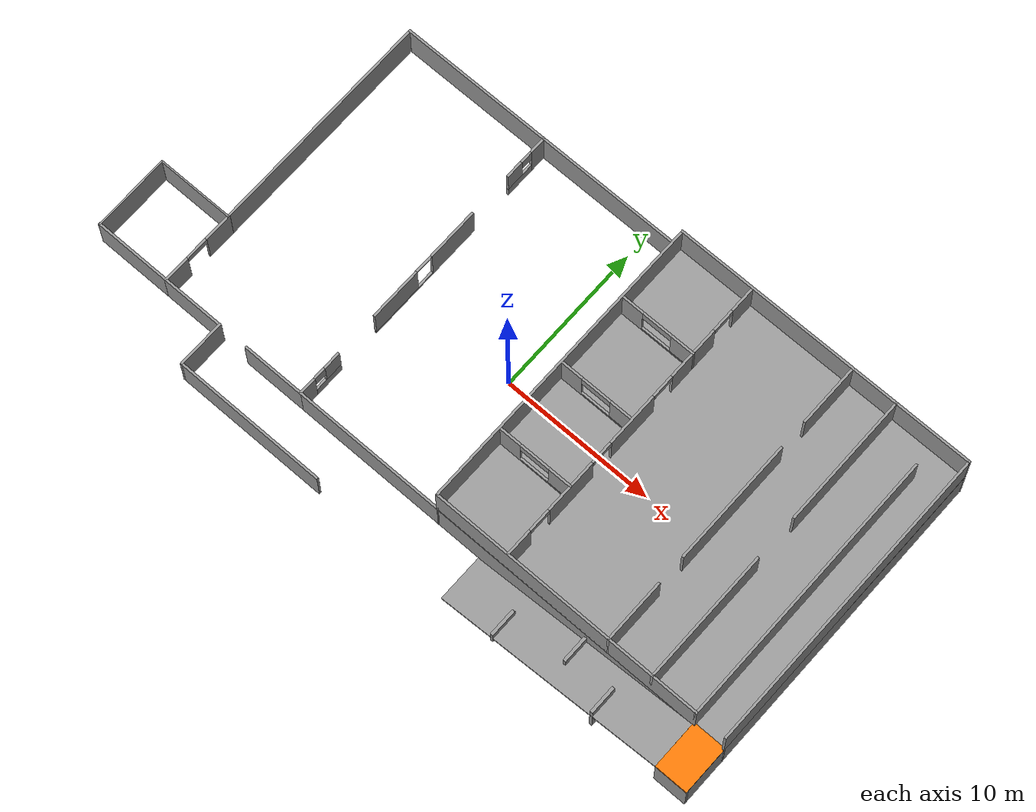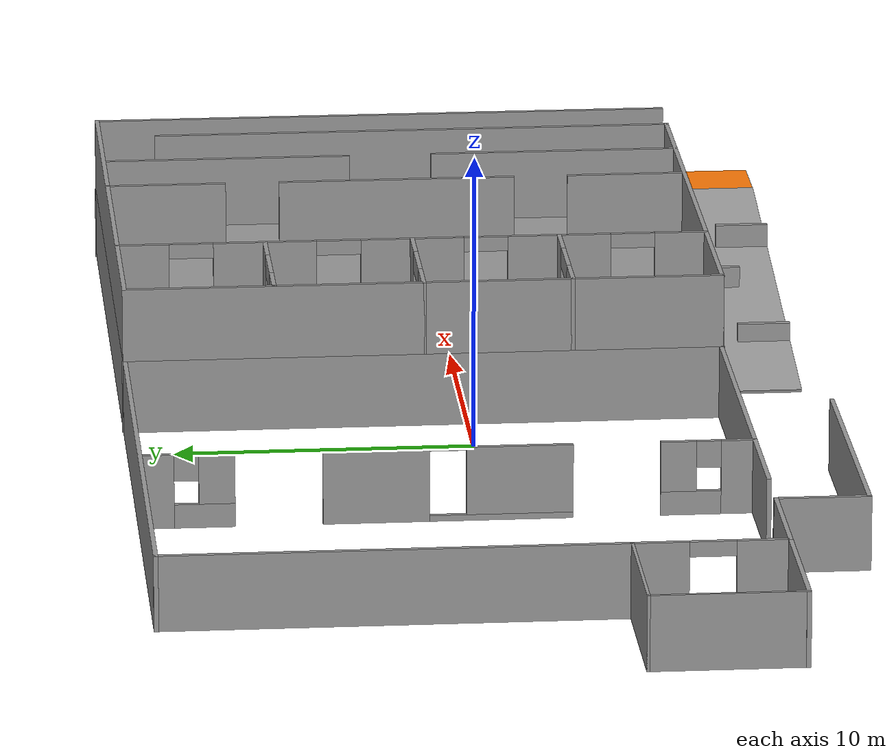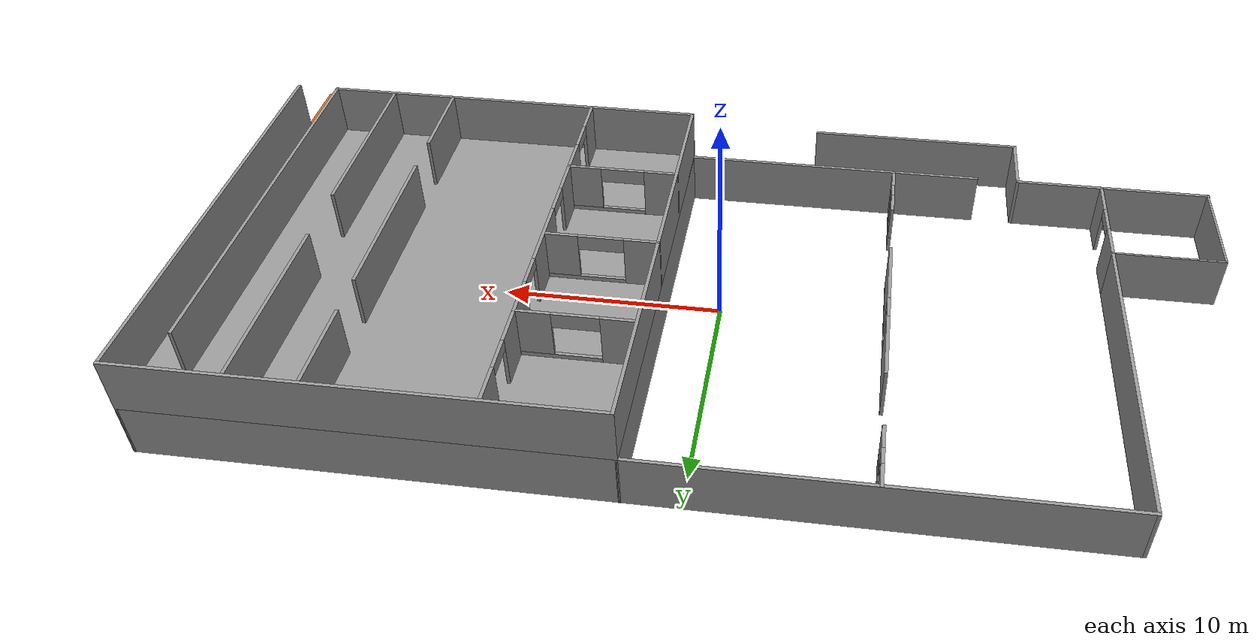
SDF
<?xml version='1.0'?>
<sdf version='1.7'>
  <model name='smart_house_3_working'>
    <link name='Floor_5'>
      <pose>21.4845 -10.0155 2.5 0 -0 0</pose>
      <self_collide>0</self_collide>
      <enable_wind>0</enable_wind>
      <kinematic>0</kinematic>
      <inertial>
        <pose>0 0 0 0 -0 0</pose>
        <inertia>
          <ixx>1</ixx>
          <ixy>0</ixy>
          <ixz>0</ixz>
          <iyy>1</iyy>
          <iyz>0</iyz>
          <izz>1</izz>
        </inertia>
        <mass>1</mass>
      </inertial>
      <visual name='Floor_5_Visual'>
        <pose>0 0 0.05 0 -0 0</pose>
        <geometry>
          <box>
            <size>2.15 3.15 0.1</size>
          </box>
        </geometry>
        <material>
          <script>
            <uri>file://media/materials/scripts/gazebo.material</uri>
            <name>Gazebo/Grey</name>
          </script>
          <ambient>0.996078 0.47451 0.0196078 1</ambient>
          <shader type='pixel'/>
        </material>
        <meta>
          <layer>1</layer>
        </meta>
        <transparency>0</transparency>
        <cast_shadows>1</cast_shadows>
      </visual>
      <collision name='Floor_5_Collision'>
        <laser_retro>0</laser_retro>
        <max_contacts>10</max_contacts>
        <pose>0 0 0.05 0 -0 0</pose>
        <geometry>
          <box>
            <size>2.15 3.15 0.1</size>
          </box>
        </geometry>
        <surface>
          <friction>
            <ode>
              <mu>1</mu>
              <mu2>1</mu2>
              <fdir1>0 0 0</fdir1>
              <slip1>0</slip1>
              <slip2>0</slip2>
            </ode>
            <torsional>
              <coefficient>1</coefficient>
              <patch_radius>0</patch_radius>
              <surface_radius>0</surface_radius>
              <use_patch_radius>1</use_patch_radius>
              <ode>
                <slip>0</slip>
              </ode>
            </torsional>
          </friction>
          <bounce>
            <restitution_coefficient>0</restitution_coefficient>
            <threshold>1e+06</threshold>
          </bounce>
          <contact>
            <collide_without_contact>0</collide_without_contact>
            <collide_without_contact_bitmask>1</collide_without_contact_bitmask>
            <collide_bitmask>1</collide_bitmask>
            <ode>
              <soft_cfm>0</soft_cfm>
              <soft_erp>0.2</soft_erp>
              <kp>1e+13</kp>
              <kd>1</kd>
              <max_vel>0.01</max_vel>
              <min_depth>0</min_depth>
            </ode>
            <bullet>
              <split_impulse>1</split_impulse>
              <split_impulse_penetration_threshold>-0.01</split_impulse_penetration_threshold>
              <soft_cfm>0</soft_cfm>
              <soft_erp>0.2</soft_erp>
              <kp>1e+13</kp>
              <kd>1</kd>
            </bullet>
          </contact>
        </surface>
      </collision>
    </link>
    <link name='Floor_6'>
      <pose>12.4845 1.48447 2.5 0 -0 0</pose>
      <self_collide>0</self_collide>
      <enable_wind>0</enable_wind>
      <kinematic>0</kinematic>
      <inertial>
        <pose>0 0 0 0 -0 0</pose>
        <inertia>
          <ixx>1</ixx>
          <ixy>0</ixy>
          <ixz>0</ixz>
          <iyy>1</iyy>
          <iyz>0</iyz>
          <izz>1</izz>
        </inertia>
        <mass>1</mass>
      </inertial>
      <visual name='Floor_6_Visual'>
        <pose>0 0 0.05 0 -0 0</pose>
        <geometry>
          <box>
            <size>20.15 20.15 0.1</size>
          </box>
        </geometry>
        <material>
          <script>
            <uri>file://media/materials/scripts/gazebo.material</uri>
            <name>Gazebo/Grey</name>
          </script>
          <ambient>1 1 1 1</ambient>
          <shader type='pixel'/>
        </material>
        <meta>
          <layer>2</layer>
        </meta>
        <transparency>0</transparency>
        <cast_shadows>1</cast_shadows>
      </visual>
      <collision name='Floor_6_Collision'>
        <laser_retro>0</laser_retro>
        <max_contacts>10</max_contacts>
        <pose>0 0 0.05 0 -0 0</pose>
        <geometry>
          <box>
            <size>20.15 20.15 0.1</size>
          </box>
        </geometry>
        <surface>
          <friction>
            <ode>
              <mu>1</mu>
              <mu2>1</mu2>
              <fdir1>0 0 0</fdir1>
              <slip1>0</slip1>
              <slip2>0</slip2>
            </ode>
            <torsional>
              <coefficient>1</coefficient>
              <patch_radius>0</patch_radius>
              <surface_radius>0</surface_radius>
              <use_patch_radius>1</use_patch_radius>
              <ode>
                <slip>0</slip>
              </ode>
            </torsional>
          </friction>
          <bounce>
            <restitution_coefficient>0</restitution_coefficient>
            <threshold>1e+06</threshold>
          </bounce>
          <contact>
            <collide_without_contact>0</collide_without_contact>
            <collide_without_contact_bitmask>1</collide_without_contact_bitmask>
            <collide_bitmask>1</collide_bitmask>
            <ode>
              <soft_cfm>0</soft_cfm>
              <soft_erp>0.2</soft_erp>
              <kp>1e+13</kp>
              <kd>1</kd>
              <max_vel>0.01</max_vel>
              <min_depth>0</min_depth>
            </ode>
            <bullet>
              <split_impulse>1</split_impulse>
              <split_impulse_penetration_threshold>-0.01</split_impulse_penetration_threshold>
              <soft_cfm>0</soft_cfm>
              <soft_erp>0.2</soft_erp>
              <kp>1e+13</kp>
              <kd>1</kd>
            </bullet>
          </contact>
        </surface>
      </collision>
    </link>
    <link name='Wall_11'>
      <pose>-20.0155 -3.51553 0 0 -0 3.14159</pose>
      <self_collide>0</self_collide>
      <enable_wind>0</enable_wind>
      <kinematic>0</kinematic>
      <inertial>
        <pose>0 0 0 0 -0 0</pose>
        <inertia>
          <ixx>1</ixx>
          <ixy>0</ixy>
          <ixz>0</ixz>
          <iyy>1</iyy>
          <iyz>0</iyz>
          <izz>1</izz>
        </inertia>
        <mass>1</mass>
      </inertial>
      <visual name='Wall_11_Visual'>
        <pose>0 0 1.25 0 -0 0</pose>
        <geometry>
          <box>
            <size>5.1 0.1 2.5</size>
          </box>
        </geometry>
        <material>
          <script>
            <uri>file://media/materials/scripts/gazebo.material</uri>
            <name>Gazebo/Grey</name>
          </script>
          <ambient>1 1 1 1</ambient>
          <shader type='pixel'/>
        </material>
        <meta>
          <layer>0</layer>
        </meta>
        <transparency>0</transparency>
        <cast_shadows>1</cast_shadows>
      </visual>
      <collision name='Wall_11_Collision'>
        <laser_retro>0</laser_retro>
        <max_contacts>10</max_contacts>
        <pose>0 0 1.25 0 -0 0</pose>
        <geometry>
          <box>
            <size>5.1 0.1 2.5</size>
          </box>
        </geometry>
        <surface>
          <friction>
            <ode>
              <mu>1</mu>
              <mu2>1</mu2>
              <fdir1>0 0 0</fdir1>
              <slip1>0</slip1>
              <slip2>0</slip2>
            </ode>
            <torsional>
              <coefficient>1</coefficient>
              <patch_radius>0</patch_radius>
              <surface_radius>0</surface_radius>
              <use_patch_radius>1</use_patch_radius>
              <ode>
                <slip>0</slip>
              </ode>
            </torsional>
          </friction>
          <bounce>
            <restitution_coefficient>0</restitution_coefficient>
            <threshold>1e+06</threshold>
          </bounce>
          <contact>
            <collide_without_contact>0</collide_without_contact>
            <collide_without_contact_bitmask>1</collide_without_contact_bitmask>
            <collide_bitmask>1</collide_bitmask>
            <ode>
              <soft_cfm>0</soft_cfm>
              <soft_erp>0.2</soft_erp>
              <kp>1e+13</kp>
              <kd>1</kd>
              <max_vel>0.01</max_vel>
              <min_depth>0</min_depth>
            </ode>
            <bullet>
              <split_impulse>1</split_impulse>
              <split_impulse_penetration_threshold>-0.01</split_impulse_penetration_threshold>
              <soft_cfm>0</soft_cfm>
              <soft_erp>0.2</soft_erp>
              <kp>1e+13</kp>
              <kd>1</kd>
            </bullet>
          </contact>
        </surface>
      </collision>
    </link>
    <link name='Wall_12'>
      <pose>-22.5155 -6.01553 0 0 0 -1.5708</pose>
      <self_collide>0</self_collide>
      <enable_wind>0</enable_wind>
      <kinematic>0</kinematic>
      <inertial>
        <pose>0 0 0 0 -0 0</pose>
        <inertia>
          <ixx>1</ixx>
          <ixy>0</ixy>
          <ixz>0</ixz>
          <iyy>1</iyy>
          <iyz>0</iyz>
          <izz>1</izz>
        </inertia>
        <mass>1</mass>
      </inertial>
      <visual name='Wall_12_Visual'>
        <pose>0 0 1.25 0 -0 0</pose>
        <geometry>
          <box>
            <size>5.1 0.1 2.5</size>
          </box>
        </geometry>
        <material>
          <script>
            <uri>file://media/materials/scripts/gazebo.material</uri>
            <name>Gazebo/Grey</name>
          </script>
          <ambient>1 1 1 1</ambient>
          <shader type='pixel'/>
        </material>
        <meta>
          <layer>0</layer>
        </meta>
        <transparency>0</transparency>
        <cast_shadows>1</cast_shadows>
      </visual>
      <collision name='Wall_12_Collision'>
        <laser_retro>0</laser_retro>
        <max_contacts>10</max_contacts>
        <pose>0 0 1.25 0 -0 0</pose>
        <geometry>
          <box>
            <size>5.1 0.1 2.5</size>
          </box>
        </geometry>
        <surface>
          <friction>
            <ode>
              <mu>1</mu>
              <mu2>1</mu2>
              <fdir1>0 0 0</fdir1>
              <slip1>0</slip1>
              <slip2>0</slip2>
            </ode>
            <torsional>
              <coefficient>1</coefficient>
              <patch_radius>0</patch_radius>
              <surface_radius>0</surface_radius>
              <use_patch_radius>1</use_patch_radius>
              <ode>
                <slip>0</slip>
              </ode>
            </torsional>
          </friction>
          <bounce>
            <restitution_coefficient>0</restitution_coefficient>
            <threshold>1e+06</threshold>
          </bounce>
          <contact>
            <collide_without_contact>0</collide_without_contact>
            <collide_without_contact_bitmask>1</collide_without_contact_bitmask>
            <collide_bitmask>1</collide_bitmask>
            <ode>
              <soft_cfm>0</soft_cfm>
              <soft_erp>0.2</soft_erp>
              <kp>1e+13</kp>
              <kd>1</kd>
              <max_vel>0.01</max_vel>
              <min_depth>0</min_depth>
            </ode>
            <bullet>
              <split_impulse>1</split_impulse>
              <split_impulse_penetration_threshold>-0.01</split_impulse_penetration_threshold>
              <soft_cfm>0</soft_cfm>
              <soft_erp>0.2</soft_erp>
              <kp>1e+13</kp>
              <kd>1</kd>
            </bullet>
          </contact>
        </surface>
      </collision>
    </link>
    <link name='Wall_139'>
      <pose>7.11602 6.85292 0 0 0 -0.785398</pose>
      <self_collide>0</self_collide>
      <enable_wind>0</enable_wind>
      <kinematic>0</kinematic>
      <inertial>
        <pose>0 0 0 0 -0 0</pose>
        <inertia>
          <ixx>1</ixx>
          <ixy>0</ixy>
          <ixz>0</ixz>
          <iyy>1</iyy>
          <iyz>0</iyz>
          <izz>1</izz>
        </inertia>
        <mass>1</mass>
      </inertial>
      <visual name='Wall_139_Visual'>
        <pose>0 0 1.25 0 -0 0</pose>
        <geometry>
          <box>
            <size>13.25 0.15 2.5</size>
          </box>
        </geometry>
        <material>
          <script>
            <uri>file://media/materials/scripts/gazebo.material</uri>
            <name>Gazebo/Grey</name>
          </script>
          <ambient>1 1 1 1</ambient>
          <shader type='pixel'/>
        </material>
        <meta>
          <layer>0</layer>
        </meta>
        <transparency>0</transparency>
        <cast_shadows>1</cast_shadows>
      </visual>
      <collision name='Wall_139_Collision'>
        <laser_retro>0</laser_retro>
        <max_contacts>10</max_contacts>
        <pose>0 0 1.25 0 -0 0</pose>
        <geometry>
          <box>
            <size>13.25 0.15 2.5</size>
          </box>
        </geometry>
        <surface>
          <friction>
            <ode>
              <mu>1</mu>
              <mu2>1</mu2>
              <fdir1>0 0 0</fdir1>
              <slip1>0</slip1>
              <slip2>0</slip2>
            </ode>
            <torsional>
              <coefficient>1</coefficient>
              <patch_radius>0</patch_radius>
              <surface_radius>0</surface_radius>
              <use_patch_radius>1</use_patch_radius>
              <ode>
                <slip>0</slip>
              </ode>
            </torsional>
          </friction>
          <bounce>
            <restitution_coefficient>0</restitution_coefficient>
            <threshold>1e+06</threshold>
          </bounce>
          <contact>
            <collide_without_contact>0</collide_without_contact>
            <collide_without_contact_bitmask>1</collide_without_contact_bitmask>
            <collide_bitmask>1</collide_bitmask>
            <ode>
              <soft_cfm>0</soft_cfm>
              <soft_erp>0.2</soft_erp>
              <kp>1e+13</kp>
              <kd>1</kd>
              <max_vel>0.01</max_vel>
              <min_depth>0</min_depth>
            </ode>
            <bullet>
              <split_impulse>1</split_impulse>
              <split_impulse_penetration_threshold>-0.01</split_impulse_penetration_threshold>
              <soft_cfm>0</soft_cfm>
              <soft_erp>0.2</soft_erp>
              <kp>1e+13</kp>
              <kd>1</kd>
            </bullet>
          </contact>
        </surface>
      </collision>
    </link>
    <link name='Wall_14'>
      <pose>2.48447 1.48447 0 0 -0 1.5708</pose>
      <self_collide>0</self_collide>
      <enable_wind>0</enable_wind>
      <kinematic>0</kinematic>
      <inertial>
        <pose>0 0 0 0 -0 0</pose>
        <inertia>
          <ixx>1</ixx>
          <ixy>0</ixy>
          <ixz>0</ixz>
          <iyy>1</iyy>
          <iyz>0</iyz>
          <izz>1</izz>
        </inertia>
        <mass>1</mass>
      </inertial>
      <visual name='Wall_14_Visual'>
        <pose>0 0 1.25 0 -0 0</pose>
        <geometry>
          <box>
            <size>20.15 0.15 2.5</size>
          </box>
        </geometry>
        <material>
          <script>
            <uri>file://media/materials/scripts/gazebo.material</uri>
            <name>Gazebo/Grey</name>
          </script>
          <ambient>1 1 1 1</ambient>
          <shader type='pixel'/>
        </material>
        <meta>
          <layer>0</layer>
        </meta>
        <transparency>0</transparency>
        <cast_shadows>1</cast_shadows>
      </visual>
      <collision name='Wall_14_Collision'>
        <laser_retro>0</laser_retro>
        <max_contacts>10</max_contacts>
        <pose>0 0 1.25 0 -0 0</pose>
        <geometry>
          <box>
            <size>20.15 0.15 2.5</size>
          </box>
        </geometry>
        <surface>
          <friction>
            <ode>
              <mu>1</mu>
              <mu2>1</mu2>
              <fdir1>0 0 0</fdir1>
              <slip1>0</slip1>
              <slip2>0</slip2>
            </ode>
            <torsional>
              <coefficient>1</coefficient>
              <patch_radius>0</patch_radius>
              <surface_radius>0</surface_radius>
              <use_patch_radius>1</use_patch_radius>
              <ode>
                <slip>0</slip>
              </ode>
            </torsional>
          </friction>
          <bounce>
            <restitution_coefficient>0</restitution_coefficient>
            <threshold>1e+06</threshold>
          </bounce>
          <contact>
            <collide_without_contact>0</collide_without_contact>
            <collide_without_contact_bitmask>1</collide_without_contact_bitmask>
            <collide_bitmask>1</collide_bitmask>
            <ode>
              <soft_cfm>0</soft_cfm>
              <soft_erp>0.2</soft_erp>
              <kp>1e+13</kp>
              <kd>1</kd>
              <max_vel>0.01</max_vel>
              <min_depth>0</min_depth>
            </ode>
            <bullet>
              <split_impulse>1</split_impulse>
              <split_impulse_penetration_threshold>-0.01</split_impulse_penetration_threshold>
              <soft_cfm>0</soft_cfm>
              <soft_erp>0.2</soft_erp>
              <kp>1e+13</kp>
              <kd>1</kd>
            </bullet>
          </contact>
        </surface>
      </collision>
    </link>
    <link name='Wall_141'>
      <pose>17.8529 6.85292 0 0 0 -2.35619</pose>
      <self_collide>0</self_collide>
      <enable_wind>0</enable_wind>
      <kinematic>0</kinematic>
      <inertial>
        <pose>0 0 0 0 -0 0</pose>
        <inertia>
          <ixx>1</ixx>
          <ixy>0</ixy>
          <ixz>0</ixz>
          <iyy>1</iyy>
          <iyz>0</iyz>
          <izz>1</izz>
        </inertia>
        <mass>1</mass>
      </inertial>
      <visual name='Wall_141_Visual'>
        <pose>0 0 1.25 0 -0 0</pose>
        <geometry>
          <box>
            <size>13.25 0.15 2.5</size>
          </box>
        </geometry>
        <material>
          <script>
            <uri>file://media/materials/scripts/gazebo.material</uri>
            <name>Gazebo/Grey</name>
          </script>
          <ambient>1 1 1 1</ambient>
          <shader type='pixel'/>
        </material>
        <meta>
          <layer>0</layer>
        </meta>
        <transparency>0</transparency>
        <cast_shadows>1</cast_shadows>
      </visual>
      <collision name='Wall_141_Collision'>
        <laser_retro>0</laser_retro>
        <max_contacts>10</max_contacts>
        <pose>0 0 1.25 0 -0 0</pose>
        <geometry>
          <box>
            <size>13.25 0.15 2.5</size>
          </box>
        </geometry>
        <surface>
          <friction>
            <ode>
              <mu>1</mu>
              <mu2>1</mu2>
              <fdir1>0 0 0</fdir1>
              <slip1>0</slip1>
              <slip2>0</slip2>
            </ode>
            <torsional>
              <coefficient>1</coefficient>
              <patch_radius>0</patch_radius>
              <surface_radius>0</surface_radius>
              <use_patch_radius>1</use_patch_radius>
              <ode>
                <slip>0</slip>
              </ode>
            </torsional>
          </friction>
          <bounce>
            <restitution_coefficient>0</restitution_coefficient>
            <threshold>1e+06</threshold>
          </bounce>
          <contact>
            <collide_without_contact>0</collide_without_contact>
            <collide_without_contact_bitmask>1</collide_without_contact_bitmask>
            <collide_bitmask>1</collide_bitmask>
            <ode>
              <soft_cfm>0</soft_cfm>
              <soft_erp>0.2</soft_erp>
              <kp>1e+13</kp>
              <kd>1</kd>
              <max_vel>0.01</max_vel>
              <min_depth>0</min_depth>
            </ode>
            <bullet>
              <split_impulse>1</split_impulse>
              <split_impulse_penetration_threshold>-0.01</split_impulse_penetration_threshold>
              <soft_cfm>0</soft_cfm>
              <soft_erp>0.2</soft_erp>
              <kp>1e+13</kp>
              <kd>1</kd>
            </bullet>
          </contact>
        </surface>
      </collision>
    </link>
    <link name='Wall_143'>
      <pose>7.11602 -3.88398 0 0 -0 0.785398</pose>
      <self_collide>0</self_collide>
      <enable_wind>0</enable_wind>
      <kinematic>0</kinematic>
      <inertial>
        <pose>0 0 0 0 -0 0</pose>
        <inertia>
          <ixx>1</ixx>
          <ixy>0</ixy>
          <ixz>0</ixz>
          <iyy>1</iyy>
          <iyz>0</iyz>
          <izz>1</izz>
        </inertia>
        <mass>1</mass>
      </inertial>
      <visual name='Wall_143_Visual'>
        <pose>0 0 1.25 0 -0 0</pose>
        <geometry>
          <box>
            <size>13.25 0.15 2.5</size>
          </box>
        </geometry>
        <material>
          <script>
            <uri>file://media/materials/scripts/gazebo.material</uri>
            <name>Gazebo/Grey</name>
          </script>
          <ambient>1 1 1 1</ambient>
          <shader type='pixel'/>
        </material>
        <meta>
          <layer>0</layer>
        </meta>
        <transparency>0</transparency>
        <cast_shadows>1</cast_shadows>
      </visual>
      <collision name='Wall_143_Collision'>
        <laser_retro>0</laser_retro>
        <max_contacts>10</max_contacts>
        <pose>0 0 1.25 0 -0 0</pose>
        <geometry>
          <box>
            <size>13.25 0.15 2.5</size>
          </box>
        </geometry>
        <surface>
          <friction>
            <ode>
              <mu>1</mu>
              <mu2>1</mu2>
              <fdir1>0 0 0</fdir1>
              <slip1>0</slip1>
              <slip2>0</slip2>
            </ode>
            <torsional>
              <coefficient>1</coefficient>
              <patch_radius>0</patch_radius>
              <surface_radius>0</surface_radius>
              <use_patch_radius>1</use_patch_radius>
              <ode>
                <slip>0</slip>
              </ode>
            </torsional>
          </friction>
          <bounce>
            <restitution_coefficient>0</restitution_coefficient>
            <threshold>1e+06</threshold>
          </bounce>
          <contact>
            <collide_without_contact>0</collide_without_contact>
            <collide_without_contact_bitmask>1</collide_without_contact_bitmask>
            <collide_bitmask>1</collide_bitmask>
            <ode>
              <soft_cfm>0</soft_cfm>
              <soft_erp>0.2</soft_erp>
              <kp>1e+13</kp>
              <kd>1</kd>
              <max_vel>0.01</max_vel>
              <min_depth>0</min_depth>
            </ode>
            <bullet>
              <split_impulse>1</split_impulse>
              <split_impulse_penetration_threshold>-0.01</split_impulse_penetration_threshold>
              <soft_cfm>0</soft_cfm>
              <soft_erp>0.2</soft_erp>
              <kp>1e+13</kp>
              <kd>1</kd>
            </bullet>
          </contact>
        </surface>
      </collision>
    </link>
    <link name='Wall_145'>
      <pose>17.8529 -3.88398 0 0 -0 2.35619</pose>
      <self_collide>0</self_collide>
      <enable_wind>0</enable_wind>
      <kinematic>0</kinematic>
      <inertial>
        <pose>0 0 0 0 -0 0</pose>
        <inertia>
          <ixx>1</ixx>
          <ixy>0</ixy>
          <ixz>0</ixz>
          <iyy>1</iyy>
          <iyz>0</iyz>
          <izz>1</izz>
        </inertia>
        <mass>1</mass>
      </inertial>
      <visual name='Wall_145_Visual'>
        <pose>0 0 1.25 0 -0 0</pose>
        <geometry>
          <box>
            <size>13.25 0.15 2.5</size>
          </box>
        </geometry>
        <material>
          <script>
            <uri>file://media/materials/scripts/gazebo.material</uri>
            <name>Gazebo/Grey</name>
          </script>
          <ambient>1 1 1 1</ambient>
          <shader type='pixel'/>
        </material>
        <meta>
          <layer>0</layer>
        </meta>
        <transparency>0</transparency>
        <cast_shadows>1</cast_shadows>
      </visual>
      <collision name='Wall_145_Collision'>
        <laser_retro>0</laser_retro>
        <max_contacts>10</max_contacts>
        <pose>0 0 1.25 0 -0 0</pose>
        <geometry>
          <box>
            <size>13.25 0.15 2.5</size>
          </box>
        </geometry>
        <surface>
          <friction>
            <ode>
              <mu>1</mu>
              <mu2>1</mu2>
              <fdir1>0 0 0</fdir1>
              <slip1>0</slip1>
              <slip2>0</slip2>
            </ode>
            <torsional>
              <coefficient>1</coefficient>
              <patch_radius>0</patch_radius>
              <surface_radius>0</surface_radius>
              <use_patch_radius>1</use_patch_radius>
              <ode>
                <slip>0</slip>
              </ode>
            </torsional>
          </friction>
          <bounce>
            <restitution_coefficient>0</restitution_coefficient>
            <threshold>1e+06</threshold>
          </bounce>
          <contact>
            <collide_without_contact>0</collide_without_contact>
            <collide_without_contact_bitmask>1</collide_without_contact_bitmask>
            <collide_bitmask>1</collide_bitmask>
            <ode>
              <soft_cfm>0</soft_cfm>
              <soft_erp>0.2</soft_erp>
              <kp>1e+13</kp>
              <kd>1</kd>
              <max_vel>0.01</max_vel>
              <min_depth>0</min_depth>
            </ode>
            <bullet>
              <split_impulse>1</split_impulse>
              <split_impulse_penetration_threshold>-0.01</split_impulse_penetration_threshold>
              <soft_cfm>0</soft_cfm>
              <soft_erp>0.2</soft_erp>
              <kp>1e+13</kp>
              <kd>1</kd>
            </bullet>
          </contact>
        </surface>
      </collision>
    </link>
    <link name='Wall_15'>
      <pose>-7.51553 11.4845 0 0 -0 3.14159</pose>
      <self_collide>0</self_collide>
      <enable_wind>0</enable_wind>
      <kinematic>0</kinematic>
      <inertial>
        <pose>0 0 0 0 -0 0</pose>
        <inertia>
          <ixx>1</ixx>
          <ixy>0</ixy>
          <ixz>0</ixz>
          <iyy>1</iyy>
          <iyz>0</iyz>
          <izz>1</izz>
        </inertia>
        <mass>1</mass>
      </inertial>
      <visual name='Wall_15_Visual'>
        <pose>0 0 1.25 0 -0 0</pose>
        <geometry>
          <box>
            <size>20.15 0.15 2.5</size>
          </box>
        </geometry>
        <material>
          <script>
            <uri>file://media/materials/scripts/gazebo.material</uri>
            <name>Gazebo/Grey</name>
          </script>
          <ambient>1 1 1 1</ambient>
          <shader type='pixel'/>
        </material>
        <meta>
          <layer>0</layer>
        </meta>
        <transparency>0</transparency>
        <cast_shadows>1</cast_shadows>
      </visual>
      <collision name='Wall_15_Collision'>
        <laser_retro>0</laser_retro>
        <max_contacts>10</max_contacts>
        <pose>0 0 1.25 0 -0 0</pose>
        <geometry>
          <box>
            <size>20.15 0.15 2.5</size>
          </box>
        </geometry>
        <surface>
          <friction>
            <ode>
              <mu>1</mu>
              <mu2>1</mu2>
              <fdir1>0 0 0</fdir1>
              <slip1>0</slip1>
              <slip2>0</slip2>
            </ode>
            <torsional>
              <coefficient>1</coefficient>
              <patch_radius>0</patch_radius>
              <surface_radius>0</surface_radius>
              <use_patch_radius>1</use_patch_radius>
              <ode>
                <slip>0</slip>
              </ode>
            </torsional>
          </friction>
          <bounce>
            <restitution_coefficient>0</restitution_coefficient>
            <threshold>1e+06</threshold>
          </bounce>
          <contact>
            <collide_without_contact>0</collide_without_contact>
            <collide_without_contact_bitmask>1</collide_without_contact_bitmask>
            <collide_bitmask>1</collide_bitmask>
            <ode>
              <soft_cfm>0</soft_cfm>
              <soft_erp>0.2</soft_erp>
              <kp>1e+13</kp>
              <kd>1</kd>
              <max_vel>0.01</max_vel>
              <min_depth>0</min_depth>
            </ode>
            <bullet>
              <split_impulse>1</split_impulse>
              <split_impulse_penetration_threshold>-0.01</split_impulse_penetration_threshold>
              <soft_cfm>0</soft_cfm>
              <soft_erp>0.2</soft_erp>
              <kp>1e+13</kp>
              <kd>1</kd>
            </bullet>
          </contact>
        </surface>
      </collision>
    </link>
    <link name='Wall_16'>
      <pose>-17.5155 3.98447 0 0 0 -1.5708</pose>
      <self_collide>0</self_collide>
      <enable_wind>0</enable_wind>
      <kinematic>0</kinematic>
      <inertial>
        <pose>0 0 0 0 -0 0</pose>
        <inertia>
          <ixx>1</ixx>
          <ixy>0</ixy>
          <ixz>0</ixz>
          <iyy>1</iyy>
          <iyz>0</iyz>
          <izz>1</izz>
        </inertia>
        <mass>1</mass>
      </inertial>
      <visual name='Wall_16_Visual'>
        <pose>0 0 1.25 0 -0 0</pose>
        <geometry>
          <box>
            <size>15.1503 0.15 2.5</size>
          </box>
        </geometry>
        <material>
          <script>
            <uri>file://media/materials/scripts/gazebo.material</uri>
            <name>Gazebo/Grey</name>
          </script>
          <ambient>1 1 1 1</ambient>
          <shader type='pixel'/>
        </material>
        <meta>
          <layer>0</layer>
        </meta>
        <transparency>0</transparency>
        <cast_shadows>1</cast_shadows>
      </visual>
      <collision name='Wall_16_Collision'>
        <laser_retro>0</laser_retro>
        <max_contacts>10</max_contacts>
        <pose>0 0 1.25 0 -0 0</pose>
        <geometry>
          <box>
            <size>15.1503 0.15 2.5</size>
          </box>
        </geometry>
        <surface>
          <friction>
            <ode>
              <mu>1</mu>
              <mu2>1</mu2>
              <fdir1>0 0 0</fdir1>
              <slip1>0</slip1>
              <slip2>0</slip2>
            </ode>
            <torsional>
              <coefficient>1</coefficient>
              <patch_radius>0</patch_radius>
              <surface_radius>0</surface_radius>
              <use_patch_radius>1</use_patch_radius>
              <ode>
                <slip>0</slip>
              </ode>
            </torsional>
          </friction>
          <bounce>
            <restitution_coefficient>0</restitution_coefficient>
            <threshold>1e+06</threshold>
          </bounce>
          <contact>
            <collide_without_contact>0</collide_without_contact>
            <collide_without_contact_bitmask>1</collide_without_contact_bitmask>
            <collide_bitmask>1</collide_bitmask>
            <ode>
              <soft_cfm>0</soft_cfm>
              <soft_erp>0.2</soft_erp>
              <kp>1e+13</kp>
              <kd>1</kd>
              <max_vel>0.01</max_vel>
              <min_depth>0</min_depth>
            </ode>
            <bullet>
              <split_impulse>1</split_impulse>
              <split_impulse_penetration_threshold>-0.01</split_impulse_penetration_threshold>
              <soft_cfm>0</soft_cfm>
              <soft_erp>0.2</soft_erp>
              <kp>1e+13</kp>
              <kd>1</kd>
            </bullet>
          </contact>
        </surface>
      </collision>
    </link>
    <link name='Wall_19'>
      <pose>22.4845 1.48447 0 0 -0 1.5708</pose>
      <self_collide>0</self_collide>
      <enable_wind>0</enable_wind>
      <kinematic>0</kinematic>
      <inertial>
        <pose>0 0 0 0 -0 0</pose>
        <inertia>
          <ixx>1</ixx>
          <ixy>0</ixy>
          <ixz>0</ixz>
          <iyy>1</iyy>
          <iyz>0</iyz>
          <izz>1</izz>
        </inertia>
        <mass>1</mass>
      </inertial>
      <visual name='Wall_19_Visual'>
        <pose>0 0 1.25 0 -0 0</pose>
        <geometry>
          <box>
            <size>20.15 0.15 2.5</size>
          </box>
        </geometry>
        <material>
          <script>
            <uri>file://media/materials/scripts/gazebo.material</uri>
            <name>Gazebo/Grey</name>
          </script>
          <ambient>1 1 1 1</ambient>
          <shader type='pixel'/>
        </material>
        <meta>
          <layer>0</layer>
        </meta>
        <transparency>0</transparency>
        <cast_shadows>1</cast_shadows>
      </visual>
      <collision name='Wall_19_Collision'>
        <laser_retro>0</laser_retro>
        <max_contacts>10</max_contacts>
        <pose>0 0 1.25 0 -0 0</pose>
        <geometry>
          <box>
            <size>20.15 0.15 2.5</size>
          </box>
        </geometry>
        <surface>
          <friction>
            <ode>
              <mu>1</mu>
              <mu2>1</mu2>
              <fdir1>0 0 0</fdir1>
              <slip1>0</slip1>
              <slip2>0</slip2>
            </ode>
            <torsional>
              <coefficient>1</coefficient>
              <patch_radius>0</patch_radius>
              <surface_radius>0</surface_radius>
              <use_patch_radius>1</use_patch_radius>
              <ode>
                <slip>0</slip>
              </ode>
            </torsional>
          </friction>
          <bounce>
            <restitution_coefficient>0</restitution_coefficient>
            <threshold>1e+06</threshold>
          </bounce>
          <contact>
            <collide_without_contact>0</collide_without_contact>
            <collide_without_contact_bitmask>1</collide_without_contact_bitmask>
            <collide_bitmask>1</collide_bitmask>
            <ode>
              <soft_cfm>0</soft_cfm>
              <soft_erp>0.2</soft_erp>
              <kp>1e+13</kp>
              <kd>1</kd>
              <max_vel>0.01</max_vel>
              <min_depth>0</min_depth>
            </ode>
            <bullet>
              <split_impulse>1</split_impulse>
              <split_impulse_penetration_threshold>-0.01</split_impulse_penetration_threshold>
              <soft_cfm>0</soft_cfm>
              <soft_erp>0.2</soft_erp>
              <kp>1e+13</kp>
              <kd>1</kd>
            </bullet>
          </contact>
        </surface>
      </collision>
    </link>
    <link name='Wall_20'>
      <pose>12.4845 11.4845 0 0 -0 3.14159</pose>
      <self_collide>0</self_collide>
      <enable_wind>0</enable_wind>
      <kinematic>0</kinematic>
      <inertial>
        <pose>0 0 0 0 -0 0</pose>
        <inertia>
          <ixx>1</ixx>
          <ixy>0</ixy>
          <ixz>0</ixz>
          <iyy>1</iyy>
          <iyz>0</iyz>
          <izz>1</izz>
        </inertia>
        <mass>1</mass>
      </inertial>
      <visual name='Wall_20_Visual'>
        <pose>0 0 1.25 0 -0 0</pose>
        <geometry>
          <box>
            <size>20.15 0.15 2.5</size>
          </box>
        </geometry>
        <material>
          <script>
            <uri>file://media/materials/scripts/gazebo.material</uri>
            <name>Gazebo/Grey</name>
          </script>
          <ambient>1 1 1 1</ambient>
          <shader type='pixel'/>
        </material>
        <meta>
          <layer>0</layer>
        </meta>
        <transparency>0</transparency>
        <cast_shadows>1</cast_shadows>
      </visual>
      <collision name='Wall_20_Collision'>
        <laser_retro>0</laser_retro>
        <max_contacts>10</max_contacts>
        <pose>0 0 1.25 0 -0 0</pose>
        <geometry>
          <box>
            <size>20.15 0.15 2.5</size>
          </box>
        </geometry>
        <surface>
          <friction>
            <ode>
              <mu>1</mu>
              <mu2>1</mu2>
              <fdir1>0 0 0</fdir1>
              <slip1>0</slip1>
              <slip2>0</slip2>
            </ode>
            <torsional>
              <coefficient>1</coefficient>
              <patch_radius>0</patch_radius>
              <surface_radius>0</surface_radius>
              <use_patch_radius>1</use_patch_radius>
              <ode>
                <slip>0</slip>
              </ode>
            </torsional>
          </friction>
          <bounce>
            <restitution_coefficient>0</restitution_coefficient>
            <threshold>1e+06</threshold>
          </bounce>
          <contact>
            <collide_without_contact>0</collide_without_contact>
            <collide_without_contact_bitmask>1</collide_without_contact_bitmask>
            <collide_bitmask>1</collide_bitmask>
            <ode>
              <soft_cfm>0</soft_cfm>
              <soft_erp>0.2</soft_erp>
              <kp>1e+13</kp>
              <kd>1</kd>
              <max_vel>0.01</max_vel>
              <min_depth>0</min_depth>
            </ode>
            <bullet>
              <split_impulse>1</split_impulse>
              <split_impulse_penetration_threshold>-0.01</split_impulse_penetration_threshold>
              <soft_cfm>0</soft_cfm>
              <soft_erp>0.2</soft_erp>
              <kp>1e+13</kp>
              <kd>1</kd>
            </bullet>
          </contact>
        </surface>
      </collision>
    </link>
    <link name='Wall_226'>
      <pose>22.4845 -10.0155 2.5 0 0 -1.5708</pose>
      <self_collide>0</self_collide>
      <enable_wind>0</enable_wind>
      <kinematic>0</kinematic>
      <inertial>
        <pose>0 0 0 0 -0 0</pose>
        <inertia>
          <ixx>1</ixx>
          <ixy>0</ixy>
          <ixz>0</ixz>
          <iyy>1</iyy>
          <iyz>0</iyz>
          <izz>1</izz>
        </inertia>
        <mass>1</mass>
      </inertial>
      <visual name='Wall_226_Visual'>
        <pose>0 0 0 0 -0 0</pose>
        <geometry>
          <box>
            <size>3.15 0.15 0</size>
          </box>
        </geometry>
        <material>
          <script>
            <uri>file://media/materials/scripts/gazebo.material</uri>
            <name>Gazebo/Grey</name>
          </script>
          <ambient>1 1 1 1</ambient>
          <shader type='pixel'/>
        </material>
        <meta>
          <layer>1</layer>
        </meta>
        <transparency>0</transparency>
        <cast_shadows>1</cast_shadows>
      </visual>
      <collision name='Wall_226_Collision'>
        <laser_retro>0</laser_retro>
        <max_contacts>10</max_contacts>
        <pose>0 0 0 0 -0 0</pose>
        <geometry>
          <box>
            <size>3.15 0.15 0</size>
          </box>
        </geometry>
        <surface>
          <friction>
            <ode>
              <mu>1</mu>
              <mu2>1</mu2>
              <fdir1>0 0 0</fdir1>
              <slip1>0</slip1>
              <slip2>0</slip2>
            </ode>
            <torsional>
              <coefficient>1</coefficient>
              <patch_radius>0</patch_radius>
              <surface_radius>0</surface_radius>
              <use_patch_radius>1</use_patch_radius>
              <ode>
                <slip>0</slip>
              </ode>
            </torsional>
          </friction>
          <bounce>
            <restitution_coefficient>0</restitution_coefficient>
            <threshold>1e+06</threshold>
          </bounce>
          <contact>
            <collide_without_contact>0</collide_without_contact>
            <collide_without_contact_bitmask>1</collide_without_contact_bitmask>
            <collide_bitmask>1</collide_bitmask>
            <ode>
              <soft_cfm>0</soft_cfm>
              <soft_erp>0.2</soft_erp>
              <kp>1e+13</kp>
              <kd>1</kd>
              <max_vel>0.01</max_vel>
              <min_depth>0</min_depth>
            </ode>
            <bullet>
              <split_impulse>1</split_impulse>
              <split_impulse_penetration_threshold>-0.01</split_impulse_penetration_threshold>
              <soft_cfm>0</soft_cfm>
              <soft_erp>0.2</soft_erp>
              <kp>1e+13</kp>
              <kd>1</kd>
            </bullet>
          </contact>
        </surface>
      </collision>
    </link>
    <link name='Wall_227'>
      <pose>21.4845 -11.5155 2.5 0 -0 3.14159</pose>
      <self_collide>0</self_collide>
      <enable_wind>0</enable_wind>
      <kinematic>0</kinematic>
      <inertial>
        <pose>0 0 0 0 -0 0</pose>
        <inertia>
          <ixx>1</ixx>
          <ixy>0</ixy>
          <ixz>0</ixz>
          <iyy>1</iyy>
          <iyz>0</iyz>
          <izz>1</izz>
        </inertia>
        <mass>1</mass>
      </inertial>
      <visual name='Wall_227_Visual'>
        <pose>0 0 0 0 -0 0</pose>
        <geometry>
          <box>
            <size>2.15 0.15 0</size>
          </box>
        </geometry>
        <material>
          <script>
            <uri>file://media/materials/scripts/gazebo.material</uri>
            <name>Gazebo/Grey</name>
          </script>
          <ambient>1 1 1 1</ambient>
          <shader type='pixel'/>
        </material>
        <meta>
          <layer>1</layer>
        </meta>
        <transparency>0</transparency>
        <cast_shadows>1</cast_shadows>
      </visual>
      <collision name='Wall_227_Collision'>
        <laser_retro>0</laser_retro>
        <max_contacts>10</max_contacts>
        <pose>0 0 0 0 -0 0</pose>
        <geometry>
          <box>
            <size>2.15 0.15 0</size>
          </box>
        </geometry>
        <surface>
          <friction>
            <ode>
              <mu>1</mu>
              <mu2>1</mu2>
              <fdir1>0 0 0</fdir1>
              <slip1>0</slip1>
              <slip2>0</slip2>
            </ode>
            <torsional>
              <coefficient>1</coefficient>
              <patch_radius>0</patch_radius>
              <surface_radius>0</surface_radius>
              <use_patch_radius>1</use_patch_radius>
              <ode>
                <slip>0</slip>
              </ode>
            </torsional>
          </friction>
          <bounce>
            <restitution_coefficient>0</restitution_coefficient>
            <threshold>1e+06</threshold>
          </bounce>
          <contact>
            <collide_without_contact>0</collide_without_contact>
            <collide_without_contact_bitmask>1</collide_without_contact_bitmask>
            <collide_bitmask>1</collide_bitmask>
            <ode>
              <soft_cfm>0</soft_cfm>
              <soft_erp>0.2</soft_erp>
              <kp>1e+13</kp>
              <kd>1</kd>
              <max_vel>0.01</max_vel>
              <min_depth>0</min_depth>
            </ode>
            <bullet>
              <split_impulse>1</split_impulse>
              <split_impulse_penetration_threshold>-0.01</split_impulse_penetration_threshold>
              <soft_cfm>0</soft_cfm>
              <soft_erp>0.2</soft_erp>
              <kp>1e+13</kp>
              <kd>1</kd>
            </bullet>
          </contact>
        </surface>
      </collision>
    </link>
    <link name='Wall_234'>
      <pose>2.48447 1.48447 2.5 0 -0 1.5708</pose>
      <self_collide>0</self_collide>
      <enable_wind>0</enable_wind>
      <kinematic>0</kinematic>
      <inertial>
        <pose>0 0 0 0 -0 0</pose>
        <inertia>
          <ixx>1</ixx>
          <ixy>0</ixy>
          <ixz>0</ixz>
          <iyy>1</iyy>
          <iyz>0</iyz>
          <izz>1</izz>
        </inertia>
        <mass>1</mass>
      </inertial>
      <visual name='Wall_234_Visual'>
        <pose>0 0 1.25 0 -0 0</pose>
        <geometry>
          <box>
            <size>20.15 0.15 2.5</size>
          </box>
        </geometry>
        <material>
          <script>
            <uri>file://media/materials/scripts/gazebo.material</uri>
            <name>Gazebo/Grey</name>
          </script>
          <ambient>1 1 1 1</ambient>
          <shader type='pixel'/>
        </material>
        <meta>
          <layer>2</layer>
        </meta>
        <transparency>0</transparency>
        <cast_shadows>1</cast_shadows>
      </visual>
      <collision name='Wall_234_Collision'>
        <laser_retro>0</laser_retro>
        <max_contacts>10</max_contacts>
        <pose>0 0 1.25 0 -0 0</pose>
        <geometry>
          <box>
            <size>20.15 0.15 2.5</size>
          </box>
        </geometry>
        <surface>
          <friction>
            <ode>
              <mu>1</mu>
              <mu2>1</mu2>
              <fdir1>0 0 0</fdir1>
              <slip1>0</slip1>
              <slip2>0</slip2>
            </ode>
            <torsional>
              <coefficient>1</coefficient>
              <patch_radius>0</patch_radius>
              <surface_radius>0</surface_radius>
              <use_patch_radius>1</use_patch_radius>
              <ode>
                <slip>0</slip>
              </ode>
            </torsional>
          </friction>
          <bounce>
            <restitution_coefficient>0</restitution_coefficient>
            <threshold>1e+06</threshold>
          </bounce>
          <contact>
            <collide_without_contact>0</collide_without_contact>
            <collide_without_contact_bitmask>1</collide_without_contact_bitmask>
            <collide_bitmask>1</collide_bitmask>
            <ode>
              <soft_cfm>0</soft_cfm>
              <soft_erp>0.2</soft_erp>
              <kp>1e+13</kp>
              <kd>1</kd>
              <max_vel>0.01</max_vel>
              <min_depth>0</min_depth>
            </ode>
            <bullet>
              <split_impulse>1</split_impulse>
              <split_impulse_penetration_threshold>-0.01</split_impulse_penetration_threshold>
              <soft_cfm>0</soft_cfm>
              <soft_erp>0.2</soft_erp>
              <kp>1e+13</kp>
              <kd>1</kd>
            </bullet>
          </contact>
        </surface>
      </collision>
    </link>
    <link name='Wall_237'>
      <pose>22.4845 1.48447 2.5 0 -0 1.5708</pose>
      <self_collide>0</self_collide>
      <enable_wind>0</enable_wind>
      <kinematic>0</kinematic>
      <inertial>
        <pose>0 0 0 0 -0 0</pose>
        <inertia>
          <ixx>1</ixx>
          <ixy>0</ixy>
          <ixz>0</ixz>
          <iyy>1</iyy>
          <iyz>0</iyz>
          <izz>1</izz>
        </inertia>
        <mass>1</mass>
      </inertial>
      <visual name='Wall_237_Visual'>
        <pose>0 0 1.25 0 -0 0</pose>
        <geometry>
          <box>
            <size>20.15 0.15 2.5</size>
          </box>
        </geometry>
        <material>
          <script>
            <uri>file://media/materials/scripts/gazebo.material</uri>
            <name>Gazebo/Grey</name>
          </script>
          <ambient>1 1 1 1</ambient>
          <shader type='pixel'/>
        </material>
        <meta>
          <layer>2</layer>
        </meta>
        <transparency>0</transparency>
        <cast_shadows>1</cast_shadows>
      </visual>
      <collision name='Wall_237_Collision'>
        <laser_retro>0</laser_retro>
        <max_contacts>10</max_contacts>
        <pose>0 0 1.25 0 -0 0</pose>
        <geometry>
          <box>
            <size>20.15 0.15 2.5</size>
          </box>
        </geometry>
        <surface>
          <friction>
            <ode>
              <mu>1</mu>
              <mu2>1</mu2>
              <fdir1>0 0 0</fdir1>
              <slip1>0</slip1>
              <slip2>0</slip2>
            </ode>
            <torsional>
              <coefficient>1</coefficient>
              <patch_radius>0</patch_radius>
              <surface_radius>0</surface_radius>
              <use_patch_radius>1</use_patch_radius>
              <ode>
                <slip>0</slip>
              </ode>
            </torsional>
          </friction>
          <bounce>
            <restitution_coefficient>0</restitution_coefficient>
            <threshold>1e+06</threshold>
          </bounce>
          <contact>
            <collide_without_contact>0</collide_without_contact>
            <collide_without_contact_bitmask>1</collide_without_contact_bitmask>
            <collide_bitmask>1</collide_bitmask>
            <ode>
              <soft_cfm>0</soft_cfm>
              <soft_erp>0.2</soft_erp>
              <kp>1e+13</kp>
              <kd>1</kd>
              <max_vel>0.01</max_vel>
              <min_depth>0</min_depth>
            </ode>
            <bullet>
              <split_impulse>1</split_impulse>
              <split_impulse_penetration_threshold>-0.01</split_impulse_penetration_threshold>
              <soft_cfm>0</soft_cfm>
              <soft_erp>0.2</soft_erp>
              <kp>1e+13</kp>
              <kd>1</kd>
            </bullet>
          </contact>
        </surface>
      </collision>
    </link>
    <link name='Wall_238'>
      <pose>12.4845 11.4845 2.5 0 -0 3.14159</pose>
      <self_collide>0</self_collide>
      <enable_wind>0</enable_wind>
      <kinematic>0</kinematic>
      <inertial>
        <pose>0 0 0 0 -0 0</pose>
        <inertia>
          <ixx>1</ixx>
          <ixy>0</ixy>
          <ixz>0</ixz>
          <iyy>1</iyy>
          <iyz>0</iyz>
          <izz>1</izz>
        </inertia>
        <mass>1</mass>
      </inertial>
      <visual name='Wall_238_Visual'>
        <pose>0 0 1.25 0 -0 0</pose>
        <geometry>
          <box>
            <size>20.15 0.15 2.5</size>
          </box>
        </geometry>
        <material>
          <script>
            <uri>file://media/materials/scripts/gazebo.material</uri>
            <name>Gazebo/Grey</name>
          </script>
          <ambient>1 1 1 1</ambient>
          <shader type='pixel'/>
        </material>
        <meta>
          <layer>2</layer>
        </meta>
        <transparency>0</transparency>
        <cast_shadows>1</cast_shadows>
      </visual>
      <collision name='Wall_238_Collision'>
        <laser_retro>0</laser_retro>
        <max_contacts>10</max_contacts>
        <pose>0 0 1.25 0 -0 0</pose>
        <geometry>
          <box>
            <size>20.15 0.15 2.5</size>
          </box>
        </geometry>
        <surface>
          <friction>
            <ode>
              <mu>1</mu>
              <mu2>1</mu2>
              <fdir1>0 0 0</fdir1>
              <slip1>0</slip1>
              <slip2>0</slip2>
            </ode>
            <torsional>
              <coefficient>1</coefficient>
              <patch_radius>0</patch_radius>
              <surface_radius>0</surface_radius>
              <use_patch_radius>1</use_patch_radius>
              <ode>
                <slip>0</slip>
              </ode>
            </torsional>
          </friction>
          <bounce>
            <restitution_coefficient>0</restitution_coefficient>
            <threshold>1e+06</threshold>
          </bounce>
          <contact>
            <collide_without_contact>0</collide_without_contact>
            <collide_without_contact_bitmask>1</collide_without_contact_bitmask>
            <collide_bitmask>1</collide_bitmask>
            <ode>
              <soft_cfm>0</soft_cfm>
              <soft_erp>0.2</soft_erp>
              <kp>1e+13</kp>
              <kd>1</kd>
              <max_vel>0.01</max_vel>
              <min_depth>0</min_depth>
            </ode>
            <bullet>
              <split_impulse>1</split_impulse>
              <split_impulse_penetration_threshold>-0.01</split_impulse_penetration_threshold>
              <soft_cfm>0</soft_cfm>
              <soft_erp>0.2</soft_erp>
              <kp>1e+13</kp>
              <kd>1</kd>
            </bullet>
          </contact>
        </surface>
      </collision>
    </link>
    <link name='Wall_24'>
      <pose>-17.5155 -6.01553 0 0 0 -1.5708</pose>
      <self_collide>0</self_collide>
      <enable_wind>0</enable_wind>
      <kinematic>0</kinematic>
      <inertial>
        <pose>0 0 0 0 -0 0</pose>
        <inertia>
          <ixx>1</ixx>
          <ixy>0</ixy>
          <ixz>0</ixz>
          <iyy>1</iyy>
          <iyz>0</iyz>
          <izz>1</izz>
        </inertia>
        <mass>1</mass>
      </inertial>
      <visual name='Wall_24_Visual_0'>
        <pose>-1.63657 0 1.25 0 -0 0</pose>
        <geometry>
          <box>
            <size>1.87687 0.15 2.5</size>
          </box>
        </geometry>
        <material>
          <script>
            <uri>file://media/materials/scripts/gazebo.material</uri>
            <name>Gazebo/Grey</name>
          </script>
          <ambient>1 1 1 1</ambient>
          <shader type='pixel'/>
        </material>
        <meta>
          <layer>0</layer>
        </meta>
        <transparency>0</transparency>
        <cast_shadows>1</cast_shadows>
      </visual>
      <visual name='Wall_24_Visual_2'>
        <pose>0.051866 0 2.25 0 -0 0</pose>
        <geometry>
          <box>
            <size>1.5 0.15 0.5</size>
          </box>
        </geometry>
        <material>
          <script>
            <uri>file://media/materials/scripts/gazebo.material</uri>
            <name>Gazebo/Grey</name>
          </script>
          <ambient>1 1 1 1</ambient>
          <shader type='pixel'/>
        </material>
        <meta>
          <layer>0</layer>
        </meta>
        <transparency>0</transparency>
        <cast_shadows>1</cast_shadows>
      </visual>
      <visual name='Wall_24_Visual_1'>
        <pose>1.68843 0 1.25 0 -0 0</pose>
        <geometry>
          <box>
            <size>1.77313 0.15 2.5</size>
          </box>
        </geometry>
        <material>
          <script>
            <uri>file://media/materials/scripts/gazebo.material</uri>
            <name>Gazebo/Grey</name>
          </script>
          <ambient>1 1 1 1</ambient>
          <shader type='pixel'/>
        </material>
        <meta>
          <layer>0</layer>
        </meta>
        <transparency>0</transparency>
        <cast_shadows>1</cast_shadows>
      </visual>
      <collision name='Wall_24_Collision_2'>
        <laser_retro>0</laser_retro>
        <max_contacts>10</max_contacts>
        <pose>0.051866 0 2.25 0 -0 0</pose>
        <geometry>
          <box>
            <size>1.5 0.15 0.5</size>
          </box>
        </geometry>
        <surface>
          <friction>
            <ode>
              <mu>1</mu>
              <mu2>1</mu2>
              <fdir1>0 0 0</fdir1>
              <slip1>0</slip1>
              <slip2>0</slip2>
            </ode>
            <torsional>
              <coefficient>1</coefficient>
              <patch_radius>0</patch_radius>
              <surface_radius>0</surface_radius>
              <use_patch_radius>1</use_patch_radius>
              <ode>
                <slip>0</slip>
              </ode>
            </torsional>
          </friction>
          <bounce>
            <restitution_coefficient>0</restitution_coefficient>
            <threshold>1e+06</threshold>
          </bounce>
          <contact>
            <collide_without_contact>0</collide_without_contact>
            <collide_without_contact_bitmask>1</collide_without_contact_bitmask>
            <collide_bitmask>1</collide_bitmask>
            <ode>
              <soft_cfm>0</soft_cfm>
              <soft_erp>0.2</soft_erp>
              <kp>1e+13</kp>
              <kd>1</kd>
              <max_vel>0.01</max_vel>
              <min_depth>0</min_depth>
            </ode>
            <bullet>
              <split_impulse>1</split_impulse>
              <split_impulse_penetration_threshold>-0.01</split_impulse_penetration_threshold>
              <soft_cfm>0</soft_cfm>
              <soft_erp>0.2</soft_erp>
              <kp>1e+13</kp>
              <kd>1</kd>
            </bullet>
          </contact>
        </surface>
      </collision>
      <collision name='Wall_24_Collision_1'>
        <laser_retro>0</laser_retro>
        <max_contacts>10</max_contacts>
        <pose>1.68843 0 1.25 0 -0 0</pose>
        <geometry>
          <box>
            <size>1.77313 0.15 2.5</size>
          </box>
        </geometry>
        <surface>
          <friction>
            <ode>
              <mu>1</mu>
              <mu2>1</mu2>
              <fdir1>0 0 0</fdir1>
              <slip1>0</slip1>
              <slip2>0</slip2>
            </ode>
            <torsional>
              <coefficient>1</coefficient>
              <patch_radius>0</patch_radius>
              <surface_radius>0</surface_radius>
              <use_patch_radius>1</use_patch_radius>
              <ode>
                <slip>0</slip>
              </ode>
            </torsional>
          </friction>
          <bounce>
            <restitution_coefficient>0</restitution_coefficient>
            <threshold>1e+06</threshold>
          </bounce>
          <contact>
            <collide_without_contact>0</collide_without_contact>
            <collide_without_contact_bitmask>1</collide_without_contact_bitmask>
            <collide_bitmask>1</collide_bitmask>
            <ode>
              <soft_cfm>0</soft_cfm>
              <soft_erp>0.2</soft_erp>
              <kp>1e+13</kp>
              <kd>1</kd>
              <max_vel>0.01</max_vel>
              <min_depth>0</min_depth>
            </ode>
            <bullet>
              <split_impulse>1</split_impulse>
              <split_impulse_penetration_threshold>-0.01</split_impulse_penetration_threshold>
              <soft_cfm>0</soft_cfm>
              <soft_erp>0.2</soft_erp>
              <kp>1e+13</kp>
              <kd>1</kd>
            </bullet>
          </contact>
        </surface>
      </collision>
      <collision name='Wall_24_Collision_0'>
        <laser_retro>0</laser_retro>
        <max_contacts>10</max_contacts>
        <pose>-1.63657 0 1.25 0 -0 0</pose>
        <geometry>
          <box>
            <size>1.87687 0.15 2.5</size>
          </box>
        </geometry>
        <surface>
          <friction>
            <ode>
              <mu>1</mu>
              <mu2>1</mu2>
              <fdir1>0 0 0</fdir1>
              <slip1>0</slip1>
              <slip2>0</slip2>
            </ode>
            <torsional>
              <coefficient>1</coefficient>
              <patch_radius>0</patch_radius>
              <surface_radius>0</surface_radius>
              <use_patch_radius>1</use_patch_radius>
              <ode>
                <slip>0</slip>
              </ode>
            </torsional>
          </friction>
          <bounce>
            <restitution_coefficient>0</restitution_coefficient>
            <threshold>1e+06</threshold>
          </bounce>
          <contact>
            <collide_without_contact>0</collide_without_contact>
            <collide_without_contact_bitmask>1</collide_without_contact_bitmask>
            <collide_bitmask>1</collide_bitmask>
            <ode>
              <soft_cfm>0</soft_cfm>
              <soft_erp>0.2</soft_erp>
              <kp>1e+13</kp>
              <kd>1</kd>
              <max_vel>0.01</max_vel>
              <min_depth>0</min_depth>
            </ode>
            <bullet>
              <split_impulse>1</split_impulse>
              <split_impulse_penetration_threshold>-0.01</split_impulse_penetration_threshold>
              <soft_cfm>0</soft_cfm>
              <soft_erp>0.2</soft_erp>
              <kp>1e+13</kp>
              <kd>1</kd>
            </bullet>
          </contact>
        </surface>
      </collision>
    </link>
    <link name='Wall_258'>
      <pose>11.4845 -8.51553 2.5 0 -0 0</pose>
      <self_collide>0</self_collide>
      <enable_wind>0</enable_wind>
      <kinematic>0</kinematic>
      <inertial>
        <pose>0 0 0 0 -0 0</pose>
        <inertia>
          <ixx>1</ixx>
          <ixy>0</ixy>
          <ixz>0</ixz>
          <iyy>1</iyy>
          <iyz>0</iyz>
          <izz>1</izz>
        </inertia>
        <mass>1</mass>
      </inertial>
      <visual name='Wall_258_Visual'>
        <pose>0 0 1.25 0 -0 0</pose>
        <geometry>
          <box>
            <size>18.15 0.15 2.5</size>
          </box>
        </geometry>
        <material>
          <script>
            <uri>file://media/materials/scripts/gazebo.material</uri>
            <name>Gazebo/Grey</name>
          </script>
          <ambient>1 1 1 1</ambient>
          <shader type='pixel'/>
        </material>
        <meta>
          <layer>2</layer>
        </meta>
        <transparency>0</transparency>
        <cast_shadows>1</cast_shadows>
      </visual>
      <collision name='Wall_258_Collision'>
        <laser_retro>0</laser_retro>
        <max_contacts>10</max_contacts>
        <pose>0 0 1.25 0 -0 0</pose>
        <geometry>
          <box>
            <size>18.15 0.15 2.5</size>
          </box>
        </geometry>
        <surface>
          <friction>
            <ode>
              <mu>1</mu>
              <mu2>1</mu2>
              <fdir1>0 0 0</fdir1>
              <slip1>0</slip1>
              <slip2>0</slip2>
            </ode>
            <torsional>
              <coefficient>1</coefficient>
              <patch_radius>0</patch_radius>
              <surface_radius>0</surface_radius>
              <use_patch_radius>1</use_patch_radius>
              <ode>
                <slip>0</slip>
              </ode>
            </torsional>
          </friction>
          <bounce>
            <restitution_coefficient>0</restitution_coefficient>
            <threshold>1e+06</threshold>
          </bounce>
          <contact>
            <collide_without_contact>0</collide_without_contact>
            <collide_without_contact_bitmask>1</collide_without_contact_bitmask>
            <collide_bitmask>1</collide_bitmask>
            <ode>
              <soft_cfm>0</soft_cfm>
              <soft_erp>0.2</soft_erp>
              <kp>1e+13</kp>
              <kd>1</kd>
              <max_vel>0.01</max_vel>
              <min_depth>0</min_depth>
            </ode>
            <bullet>
              <split_impulse>1</split_impulse>
              <split_impulse_penetration_threshold>-0.01</split_impulse_penetration_threshold>
              <soft_cfm>0</soft_cfm>
              <soft_erp>0.2</soft_erp>
              <kp>1e+13</kp>
              <kd>1</kd>
            </bullet>
          </contact>
        </surface>
      </collision>
    </link>
    <link name='Wall_265'>
      <pose>20.4845 0.484467 2.5 0 -0 1.5708</pose>
      <self_collide>0</self_collide>
      <enable_wind>0</enable_wind>
      <kinematic>0</kinematic>
      <inertial>
        <pose>0 0 0 0 -0 0</pose>
        <inertia>
          <ixx>1</ixx>
          <ixy>0</ixy>
          <ixz>0</ixz>
          <iyy>1</iyy>
          <iyz>0</iyz>
          <izz>1</izz>
        </inertia>
        <mass>1</mass>
      </inertial>
      <visual name='Wall_265_Visual'>
        <pose>0 0 1.25 0 -0 0</pose>
        <geometry>
          <box>
            <size>18.15 0.15 2.5</size>
          </box>
        </geometry>
        <material>
          <script>
            <uri>file://media/materials/scripts/gazebo.material</uri>
            <name>Gazebo/Grey</name>
          </script>
          <ambient>1 1 1 1</ambient>
          <shader type='pixel'/>
        </material>
        <meta>
          <layer>2</layer>
        </meta>
        <transparency>0</transparency>
        <cast_shadows>1</cast_shadows>
      </visual>
      <collision name='Wall_265_Collision'>
        <laser_retro>0</laser_retro>
        <max_contacts>10</max_contacts>
        <pose>0 0 1.25 0 -0 0</pose>
        <geometry>
          <box>
            <size>18.15 0.15 2.5</size>
          </box>
        </geometry>
        <surface>
          <friction>
            <ode>
              <mu>1</mu>
              <mu2>1</mu2>
              <fdir1>0 0 0</fdir1>
              <slip1>0</slip1>
              <slip2>0</slip2>
            </ode>
            <torsional>
              <coefficient>1</coefficient>
              <patch_radius>0</patch_radius>
              <surface_radius>0</surface_radius>
              <use_patch_radius>1</use_patch_radius>
              <ode>
                <slip>0</slip>
              </ode>
            </torsional>
          </friction>
          <bounce>
            <restitution_coefficient>0</restitution_coefficient>
            <threshold>1e+06</threshold>
          </bounce>
          <contact>
            <collide_without_contact>0</collide_without_contact>
            <collide_without_contact_bitmask>1</collide_without_contact_bitmask>
            <collide_bitmask>1</collide_bitmask>
            <ode>
              <soft_cfm>0</soft_cfm>
              <soft_erp>0.2</soft_erp>
              <kp>1e+13</kp>
              <kd>1</kd>
              <max_vel>0.01</max_vel>
              <min_depth>0</min_depth>
            </ode>
            <bullet>
              <split_impulse>1</split_impulse>
              <split_impulse_penetration_threshold>-0.01</split_impulse_penetration_threshold>
              <soft_cfm>0</soft_cfm>
              <soft_erp>0.2</soft_erp>
              <kp>1e+13</kp>
              <kd>1</kd>
            </bullet>
          </contact>
        </surface>
      </collision>
    </link>
    <link name='Wall_276'>
      <pose>17.4845 -4.26553 2.5 0 0 -1.5708</pose>
      <self_collide>0</self_collide>
      <enable_wind>0</enable_wind>
      <kinematic>0</kinematic>
      <inertial>
        <pose>0 0 0 0 -0 0</pose>
        <inertia>
          <ixx>1</ixx>
          <ixy>0</ixy>
          <ixz>0</ixz>
          <iyy>1</iyy>
          <iyz>0</iyz>
          <izz>1</izz>
        </inertia>
        <mass>1</mass>
      </inertial>
      <visual name='Wall_276_Visual'>
        <pose>0 0 1.25 0 -0 0</pose>
        <geometry>
          <box>
            <size>8.65 0.15 2.5</size>
          </box>
        </geometry>
        <material>
          <script>
            <uri>file://media/materials/scripts/gazebo.material</uri>
            <name>Gazebo/Grey</name>
          </script>
          <ambient>1 1 1 1</ambient>
          <shader type='pixel'/>
        </material>
        <meta>
          <layer>2</layer>
        </meta>
        <transparency>0</transparency>
        <cast_shadows>1</cast_shadows>
      </visual>
      <collision name='Wall_276_Collision'>
        <laser_retro>0</laser_retro>
        <max_contacts>10</max_contacts>
        <pose>0 0 1.25 0 -0 0</pose>
        <geometry>
          <box>
            <size>8.65 0.15 2.5</size>
          </box>
        </geometry>
        <surface>
          <friction>
            <ode>
              <mu>1</mu>
              <mu2>1</mu2>
              <fdir1>0 0 0</fdir1>
              <slip1>0</slip1>
              <slip2>0</slip2>
            </ode>
            <torsional>
              <coefficient>1</coefficient>
              <patch_radius>0</patch_radius>
              <surface_radius>0</surface_radius>
              <use_patch_radius>1</use_patch_radius>
              <ode>
                <slip>0</slip>
              </ode>
            </torsional>
          </friction>
          <bounce>
            <restitution_coefficient>0</restitution_coefficient>
            <threshold>1e+06</threshold>
          </bounce>
          <contact>
            <collide_without_contact>0</collide_without_contact>
            <collide_without_contact_bitmask>1</collide_without_contact_bitmask>
            <collide_bitmask>1</collide_bitmask>
            <ode>
              <soft_cfm>0</soft_cfm>
              <soft_erp>0.2</soft_erp>
              <kp>1e+13</kp>
              <kd>1</kd>
              <max_vel>0.01</max_vel>
              <min_depth>0</min_depth>
            </ode>
            <bullet>
              <split_impulse>1</split_impulse>
              <split_impulse_penetration_threshold>-0.01</split_impulse_penetration_threshold>
              <soft_cfm>0</soft_cfm>
              <soft_erp>0.2</soft_erp>
              <kp>1e+13</kp>
              <kd>1</kd>
            </bullet>
          </contact>
        </surface>
      </collision>
    </link>
    <link name='Wall_278'>
      <pose>17.4845 7.23447 2.5 0 -0 1.5708</pose>
      <self_collide>0</self_collide>
      <enable_wind>0</enable_wind>
      <kinematic>0</kinematic>
      <inertial>
        <pose>0 0 0 0 -0 0</pose>
        <inertia>
          <ixx>1</ixx>
          <ixy>0</ixy>
          <ixz>0</ixz>
          <iyy>1</iyy>
          <iyz>0</iyz>
          <izz>1</izz>
        </inertia>
        <mass>1</mass>
      </inertial>
      <visual name='Wall_278_Visual'>
        <pose>0 0 1.25 0 -0 0</pose>
        <geometry>
          <box>
            <size>8.65 0.15 2.5</size>
          </box>
        </geometry>
        <material>
          <script>
            <uri>file://media/materials/scripts/gazebo.material</uri>
            <name>Gazebo/Grey</name>
          </script>
          <ambient>1 1 1 1</ambient>
          <shader type='pixel'/>
        </material>
        <meta>
          <layer>2</layer>
        </meta>
        <transparency>0</transparency>
        <cast_shadows>1</cast_shadows>
      </visual>
      <collision name='Wall_278_Collision'>
        <laser_retro>0</laser_retro>
        <max_contacts>10</max_contacts>
        <pose>0 0 1.25 0 -0 0</pose>
        <geometry>
          <box>
            <size>8.65 0.15 2.5</size>
          </box>
        </geometry>
        <surface>
          <friction>
            <ode>
              <mu>1</mu>
              <mu2>1</mu2>
              <fdir1>0 0 0</fdir1>
              <slip1>0</slip1>
              <slip2>0</slip2>
            </ode>
            <torsional>
              <coefficient>1</coefficient>
              <patch_radius>0</patch_radius>
              <surface_radius>0</surface_radius>
              <use_patch_radius>1</use_patch_radius>
              <ode>
                <slip>0</slip>
              </ode>
            </torsional>
          </friction>
          <bounce>
            <restitution_coefficient>0</restitution_coefficient>
            <threshold>1e+06</threshold>
          </bounce>
          <contact>
            <collide_without_contact>0</collide_without_contact>
            <collide_without_contact_bitmask>1</collide_without_contact_bitmask>
            <collide_bitmask>1</collide_bitmask>
            <ode>
              <soft_cfm>0</soft_cfm>
              <soft_erp>0.2</soft_erp>
              <kp>1e+13</kp>
              <kd>1</kd>
              <max_vel>0.01</max_vel>
              <min_depth>0</min_depth>
            </ode>
            <bullet>
              <split_impulse>1</split_impulse>
              <split_impulse_penetration_threshold>-0.01</split_impulse_penetration_threshold>
              <soft_cfm>0</soft_cfm>
              <soft_erp>0.2</soft_erp>
              <kp>1e+13</kp>
              <kd>1</kd>
            </bullet>
          </contact>
        </surface>
      </collision>
    </link>
    <link name='Wall_282'>
      <pose>14.4845 9.48447 2.5 0 0 -1.5708</pose>
      <self_collide>0</self_collide>
      <enable_wind>0</enable_wind>
      <kinematic>0</kinematic>
      <inertial>
        <pose>0 0 0 0 -0 0</pose>
        <inertia>
          <ixx>1</ixx>
          <ixy>0</ixy>
          <ixz>0</ixz>
          <iyy>1</iyy>
          <iyz>0</iyz>
          <izz>1</izz>
        </inertia>
        <mass>1</mass>
      </inertial>
      <visual name='Wall_282_Visual'>
        <pose>0 0 1.25 0 -0 0</pose>
        <geometry>
          <box>
            <size>4.15 0.15 2.5</size>
          </box>
        </geometry>
        <material>
          <script>
            <uri>file://media/materials/scripts/gazebo.material</uri>
            <name>Gazebo/Grey</name>
          </script>
          <ambient>1 1 1 1</ambient>
          <shader type='pixel'/>
        </material>
        <meta>
          <layer>2</layer>
        </meta>
        <transparency>0</transparency>
        <cast_shadows>1</cast_shadows>
      </visual>
      <collision name='Wall_282_Collision'>
        <laser_retro>0</laser_retro>
        <max_contacts>10</max_contacts>
        <pose>0 0 1.25 0 -0 0</pose>
        <geometry>
          <box>
            <size>4.15 0.15 2.5</size>
          </box>
        </geometry>
        <surface>
          <friction>
            <ode>
              <mu>1</mu>
              <mu2>1</mu2>
              <fdir1>0 0 0</fdir1>
              <slip1>0</slip1>
              <slip2>0</slip2>
            </ode>
            <torsional>
              <coefficient>1</coefficient>
              <patch_radius>0</patch_radius>
              <surface_radius>0</surface_radius>
              <use_patch_radius>1</use_patch_radius>
              <ode>
                <slip>0</slip>
              </ode>
            </torsional>
          </friction>
          <bounce>
            <restitution_coefficient>0</restitution_coefficient>
            <threshold>1e+06</threshold>
          </bounce>
          <contact>
            <collide_without_contact>0</collide_without_contact>
            <collide_without_contact_bitmask>1</collide_without_contact_bitmask>
            <collide_bitmask>1</collide_bitmask>
            <ode>
              <soft_cfm>0</soft_cfm>
              <soft_erp>0.2</soft_erp>
              <kp>1e+13</kp>
              <kd>1</kd>
              <max_vel>0.01</max_vel>
              <min_depth>0</min_depth>
            </ode>
            <bullet>
              <split_impulse>1</split_impulse>
              <split_impulse_penetration_threshold>-0.01</split_impulse_penetration_threshold>
              <soft_cfm>0</soft_cfm>
              <soft_erp>0.2</soft_erp>
              <kp>1e+13</kp>
              <kd>1</kd>
            </bullet>
          </contact>
        </surface>
      </collision>
    </link>
    <link name='Wall_284'>
      <pose>14.4845 -6.51553 2.5 0 -0 1.5708</pose>
      <self_collide>0</self_collide>
      <enable_wind>0</enable_wind>
      <kinematic>0</kinematic>
      <inertial>
        <pose>0 0 0 0 -0 0</pose>
        <inertia>
          <ixx>1</ixx>
          <ixy>0</ixy>
          <ixz>0</ixz>
          <iyy>1</iyy>
          <iyz>0</iyz>
          <izz>1</izz>
        </inertia>
        <mass>1</mass>
      </inertial>
      <visual name='Wall_284_Visual'>
        <pose>0 0 1.25 0 -0 0</pose>
        <geometry>
          <box>
            <size>4.15 0.15 2.5</size>
          </box>
        </geometry>
        <material>
          <script>
            <uri>file://media/materials/scripts/gazebo.material</uri>
            <name>Gazebo/Grey</name>
          </script>
          <ambient>1 1 1 1</ambient>
          <shader type='pixel'/>
        </material>
        <meta>
          <layer>2</layer>
        </meta>
        <transparency>0</transparency>
        <cast_shadows>1</cast_shadows>
      </visual>
      <collision name='Wall_284_Collision'>
        <laser_retro>0</laser_retro>
        <max_contacts>10</max_contacts>
        <pose>0 0 1.25 0 -0 0</pose>
        <geometry>
          <box>
            <size>4.15 0.15 2.5</size>
          </box>
        </geometry>
        <surface>
          <friction>
            <ode>
              <mu>1</mu>
              <mu2>1</mu2>
              <fdir1>0 0 0</fdir1>
              <slip1>0</slip1>
              <slip2>0</slip2>
            </ode>
            <torsional>
              <coefficient>1</coefficient>
              <patch_radius>0</patch_radius>
              <surface_radius>0</surface_radius>
              <use_patch_radius>1</use_patch_radius>
              <ode>
                <slip>0</slip>
              </ode>
            </torsional>
          </friction>
          <bounce>
            <restitution_coefficient>0</restitution_coefficient>
            <threshold>1e+06</threshold>
          </bounce>
          <contact>
            <collide_without_contact>0</collide_without_contact>
            <collide_without_contact_bitmask>1</collide_without_contact_bitmask>
            <collide_bitmask>1</collide_bitmask>
            <ode>
              <soft_cfm>0</soft_cfm>
              <soft_erp>0.2</soft_erp>
              <kp>1e+13</kp>
              <kd>1</kd>
              <max_vel>0.01</max_vel>
              <min_depth>0</min_depth>
            </ode>
            <bullet>
              <split_impulse>1</split_impulse>
              <split_impulse_penetration_threshold>-0.01</split_impulse_penetration_threshold>
              <soft_cfm>0</soft_cfm>
              <soft_erp>0.2</soft_erp>
              <kp>1e+13</kp>
              <kd>1</kd>
            </bullet>
          </contact>
        </surface>
      </collision>
    </link>
    <link name='Wall_286'>
      <pose>14.4845 1.48447 2.5 0 0 -1.5708</pose>
      <self_collide>0</self_collide>
      <enable_wind>0</enable_wind>
      <kinematic>0</kinematic>
      <inertial>
        <pose>0 0 0 0 -0 0</pose>
        <inertia>
          <ixx>1</ixx>
          <ixy>0</ixy>
          <ixz>0</ixz>
          <iyy>1</iyy>
          <iyz>0</iyz>
          <izz>1</izz>
        </inertia>
        <mass>1</mass>
      </inertial>
      <visual name='Wall_286_Visual'>
        <pose>0 0 1.25 0 -0 0</pose>
        <geometry>
          <box>
            <size>8.15 0.15 2.5</size>
          </box>
        </geometry>
        <material>
          <script>
            <uri>file://media/materials/scripts/gazebo.material</uri>
            <name>Gazebo/Grey</name>
          </script>
          <ambient>1 1 1 1</ambient>
          <shader type='pixel'/>
        </material>
        <meta>
          <layer>2</layer>
        </meta>
        <transparency>0</transparency>
        <cast_shadows>1</cast_shadows>
      </visual>
      <collision name='Wall_286_Collision'>
        <laser_retro>0</laser_retro>
        <max_contacts>10</max_contacts>
        <pose>0 0 1.25 0 -0 0</pose>
        <geometry>
          <box>
            <size>8.15 0.15 2.5</size>
          </box>
        </geometry>
        <surface>
          <friction>
            <ode>
              <mu>1</mu>
              <mu2>1</mu2>
              <fdir1>0 0 0</fdir1>
              <slip1>0</slip1>
              <slip2>0</slip2>
            </ode>
            <torsional>
              <coefficient>1</coefficient>
              <patch_radius>0</patch_radius>
              <surface_radius>0</surface_radius>
              <use_patch_radius>1</use_patch_radius>
              <ode>
                <slip>0</slip>
              </ode>
            </torsional>
          </friction>
          <bounce>
            <restitution_coefficient>0</restitution_coefficient>
            <threshold>1e+06</threshold>
          </bounce>
          <contact>
            <collide_without_contact>0</collide_without_contact>
            <collide_without_contact_bitmask>1</collide_without_contact_bitmask>
            <collide_bitmask>1</collide_bitmask>
            <ode>
              <soft_cfm>0</soft_cfm>
              <soft_erp>0.2</soft_erp>
              <kp>1e+13</kp>
              <kd>1</kd>
              <max_vel>0.01</max_vel>
              <min_depth>0</min_depth>
            </ode>
            <bullet>
              <split_impulse>1</split_impulse>
              <split_impulse_penetration_threshold>-0.01</split_impulse_penetration_threshold>
              <soft_cfm>0</soft_cfm>
              <soft_erp>0.2</soft_erp>
              <kp>1e+13</kp>
              <kd>1</kd>
            </bullet>
          </contact>
        </surface>
      </collision>
    </link>
    <link name='Wall_288'>
      <pose>4.98447 6.48447 2.5 0 -0 0</pose>
      <self_collide>0</self_collide>
      <enable_wind>0</enable_wind>
      <kinematic>0</kinematic>
      <inertial>
        <pose>0 0 0 0 -0 0</pose>
        <inertia>
          <ixx>1</ixx>
          <ixy>0</ixy>
          <ixz>0</ixz>
          <iyy>1</iyy>
          <iyz>0</iyz>
          <izz>1</izz>
        </inertia>
        <mass>1</mass>
      </inertial>
      <visual name='Wall_288_Visual_1'>
        <pose>0.7875 0 0.15 0 -0 0</pose>
        <geometry>
          <box>
            <size>3.575 0.15 0.3</size>
          </box>
        </geometry>
        <material>
          <script>
            <uri>file://media/materials/scripts/gazebo.material</uri>
            <name>Gazebo/Grey</name>
          </script>
          <ambient>1 1 1 1</ambient>
          <shader type='pixel'/>
        </material>
        <meta>
          <layer>2</layer>
        </meta>
        <transparency>0</transparency>
        <cast_shadows>1</cast_shadows>
      </visual>
      <visual name='Wall_288_Visual_3'>
        <pose>0 0 2.15 0 -0 0</pose>
        <geometry>
          <box>
            <size>2 0.15 0.7</size>
          </box>
        </geometry>
        <material>
          <script>
            <uri>file://media/materials/scripts/gazebo.material</uri>
            <name>Gazebo/Grey</name>
          </script>
          <ambient>1 1 1 1</ambient>
          <shader type='pixel'/>
        </material>
        <meta>
          <layer>2</layer>
        </meta>
        <transparency>0</transparency>
        <cast_shadows>1</cast_shadows>
      </visual>
      <visual name='Wall_288_Visual_2'>
        <pose>1.7875 0 1.4 0 -0 0</pose>
        <geometry>
          <box>
            <size>1.575 0.15 2.2</size>
          </box>
        </geometry>
        <material>
          <script>
            <uri>file://media/materials/scripts/gazebo.material</uri>
            <name>Gazebo/Grey</name>
          </script>
          <ambient>1 1 1 1</ambient>
          <shader type='pixel'/>
        </material>
        <meta>
          <layer>2</layer>
        </meta>
        <transparency>0</transparency>
        <cast_shadows>1</cast_shadows>
      </visual>
      <visual name='Wall_288_Visual_0'>
        <pose>-1.7875 0 1.25 0 -0 0</pose>
        <geometry>
          <box>
            <size>1.575 0.15 2.5</size>
          </box>
        </geometry>
        <material>
          <script>
            <uri>file://media/materials/scripts/gazebo.material</uri>
            <name>Gazebo/Grey</name>
          </script>
          <ambient>1 1 1 1</ambient>
          <shader type='pixel'/>
        </material>
        <meta>
          <layer>2</layer>
        </meta>
        <transparency>0</transparency>
        <cast_shadows>1</cast_shadows>
      </visual>
      <collision name='Wall_288_Collision_0'>
        <laser_retro>0</laser_retro>
        <max_contacts>10</max_contacts>
        <pose>-1.7875 0 1.25 0 -0 0</pose>
        <geometry>
          <box>
            <size>1.575 0.15 2.5</size>
          </box>
        </geometry>
        <surface>
          <friction>
            <ode>
              <mu>1</mu>
              <mu2>1</mu2>
              <fdir1>0 0 0</fdir1>
              <slip1>0</slip1>
              <slip2>0</slip2>
            </ode>
            <torsional>
              <coefficient>1</coefficient>
              <patch_radius>0</patch_radius>
              <surface_radius>0</surface_radius>
              <use_patch_radius>1</use_patch_radius>
              <ode>
                <slip>0</slip>
              </ode>
            </torsional>
          </friction>
          <bounce>
            <restitution_coefficient>0</restitution_coefficient>
            <threshold>1e+06</threshold>
          </bounce>
          <contact>
            <collide_without_contact>0</collide_without_contact>
            <collide_without_contact_bitmask>1</collide_without_contact_bitmask>
            <collide_bitmask>1</collide_bitmask>
            <ode>
              <soft_cfm>0</soft_cfm>
              <soft_erp>0.2</soft_erp>
              <kp>1e+13</kp>
              <kd>1</kd>
              <max_vel>0.01</max_vel>
              <min_depth>0</min_depth>
            </ode>
            <bullet>
              <split_impulse>1</split_impulse>
              <split_impulse_penetration_threshold>-0.01</split_impulse_penetration_threshold>
              <soft_cfm>0</soft_cfm>
              <soft_erp>0.2</soft_erp>
              <kp>1e+13</kp>
              <kd>1</kd>
            </bullet>
          </contact>
        </surface>
      </collision>
      <collision name='Wall_288_Collision_2'>
        <laser_retro>0</laser_retro>
        <max_contacts>10</max_contacts>
        <pose>1.7875 0 1.4 0 -0 0</pose>
        <geometry>
          <box>
            <size>1.575 0.15 2.2</size>
          </box>
        </geometry>
        <surface>
          <friction>
            <ode>
              <mu>1</mu>
              <mu2>1</mu2>
              <fdir1>0 0 0</fdir1>
              <slip1>0</slip1>
              <slip2>0</slip2>
            </ode>
            <torsional>
              <coefficient>1</coefficient>
              <patch_radius>0</patch_radius>
              <surface_radius>0</surface_radius>
              <use_patch_radius>1</use_patch_radius>
              <ode>
                <slip>0</slip>
              </ode>
            </torsional>
          </friction>
          <bounce>
            <restitution_coefficient>0</restitution_coefficient>
            <threshold>1e+06</threshold>
          </bounce>
          <contact>
            <collide_without_contact>0</collide_without_contact>
            <collide_without_contact_bitmask>1</collide_without_contact_bitmask>
            <collide_bitmask>1</collide_bitmask>
            <ode>
              <soft_cfm>0</soft_cfm>
              <soft_erp>0.2</soft_erp>
              <kp>1e+13</kp>
              <kd>1</kd>
              <max_vel>0.01</max_vel>
              <min_depth>0</min_depth>
            </ode>
            <bullet>
              <split_impulse>1</split_impulse>
              <split_impulse_penetration_threshold>-0.01</split_impulse_penetration_threshold>
              <soft_cfm>0</soft_cfm>
              <soft_erp>0.2</soft_erp>
              <kp>1e+13</kp>
              <kd>1</kd>
            </bullet>
          </contact>
        </surface>
      </collision>
      <collision name='Wall_288_Collision_3'>
        <laser_retro>0</laser_retro>
        <max_contacts>10</max_contacts>
        <pose>0 0 2.15 0 -0 0</pose>
        <geometry>
          <box>
            <size>2 0.15 0.7</size>
          </box>
        </geometry>
        <surface>
          <friction>
            <ode>
              <mu>1</mu>
              <mu2>1</mu2>
              <fdir1>0 0 0</fdir1>
              <slip1>0</slip1>
              <slip2>0</slip2>
            </ode>
            <torsional>
              <coefficient>1</coefficient>
              <patch_radius>0</patch_radius>
              <surface_radius>0</surface_radius>
              <use_patch_radius>1</use_patch_radius>
              <ode>
                <slip>0</slip>
              </ode>
            </torsional>
          </friction>
          <bounce>
            <restitution_coefficient>0</restitution_coefficient>
            <threshold>1e+06</threshold>
          </bounce>
          <contact>
            <collide_without_contact>0</collide_without_contact>
            <collide_without_contact_bitmask>1</collide_without_contact_bitmask>
            <collide_bitmask>1</collide_bitmask>
            <ode>
              <soft_cfm>0</soft_cfm>
              <soft_erp>0.2</soft_erp>
              <kp>1e+13</kp>
              <kd>1</kd>
              <max_vel>0.01</max_vel>
              <min_depth>0</min_depth>
            </ode>
            <bullet>
              <split_impulse>1</split_impulse>
              <split_impulse_penetration_threshold>-0.01</split_impulse_penetration_threshold>
              <soft_cfm>0</soft_cfm>
              <soft_erp>0.2</soft_erp>
              <kp>1e+13</kp>
              <kd>1</kd>
            </bullet>
          </contact>
        </surface>
      </collision>
      <collision name='Wall_288_Collision_1'>
        <laser_retro>0</laser_retro>
        <max_contacts>10</max_contacts>
        <pose>0.7875 0 0.15 0 -0 0</pose>
        <geometry>
          <box>
            <size>3.575 0.15 0.3</size>
          </box>
        </geometry>
        <surface>
          <friction>
            <ode>
              <mu>1</mu>
              <mu2>1</mu2>
              <fdir1>0 0 0</fdir1>
              <slip1>0</slip1>
              <slip2>0</slip2>
            </ode>
            <torsional>
              <coefficient>1</coefficient>
              <patch_radius>0</patch_radius>
              <surface_radius>0</surface_radius>
              <use_patch_radius>1</use_patch_radius>
              <ode>
                <slip>0</slip>
              </ode>
            </torsional>
          </friction>
          <bounce>
            <restitution_coefficient>0</restitution_coefficient>
            <threshold>1e+06</threshold>
          </bounce>
          <contact>
            <collide_without_contact>0</collide_without_contact>
            <collide_without_contact_bitmask>1</collide_without_contact_bitmask>
            <collide_bitmask>1</collide_bitmask>
            <ode>
              <soft_cfm>0</soft_cfm>
              <soft_erp>0.2</soft_erp>
              <kp>1e+13</kp>
              <kd>1</kd>
              <max_vel>0.01</max_vel>
              <min_depth>0</min_depth>
            </ode>
            <bullet>
              <split_impulse>1</split_impulse>
              <split_impulse_penetration_threshold>-0.01</split_impulse_penetration_threshold>
              <soft_cfm>0</soft_cfm>
              <soft_erp>0.2</soft_erp>
              <kp>1e+13</kp>
              <kd>1</kd>
            </bullet>
          </contact>
        </surface>
      </collision>
    </link>
    <link name='Wall_290'>
      <pose>4.98447 1.48447 2.5 0 -0 0</pose>
      <self_collide>0</self_collide>
      <enable_wind>0</enable_wind>
      <kinematic>0</kinematic>
      <inertial>
        <pose>0 0 0 0 -0 0</pose>
        <inertia>
          <ixx>1</ixx>
          <ixy>0</ixy>
          <ixz>0</ixz>
          <iyy>1</iyy>
          <iyz>0</iyz>
          <izz>1</izz>
        </inertia>
        <mass>1</mass>
      </inertial>
      <visual name='Wall_290_Visual_0'>
        <pose>-1.7875 0 1.25 0 -0 0</pose>
        <geometry>
          <box>
            <size>1.575 0.15 2.5</size>
          </box>
        </geometry>
        <material>
          <script>
            <uri>file://media/materials/scripts/gazebo.material</uri>
            <name>Gazebo/Grey</name>
          </script>
          <ambient>1 1 1 1</ambient>
          <shader type='pixel'/>
        </material>
        <meta>
          <layer>2</layer>
        </meta>
        <transparency>0</transparency>
        <cast_shadows>1</cast_shadows>
      </visual>
      <visual name='Wall_290_Visual_3'>
        <pose>0 0 2.15 0 -0 0</pose>
        <geometry>
          <box>
            <size>2 0.15 0.7</size>
          </box>
        </geometry>
        <material>
          <script>
            <uri>file://media/materials/scripts/gazebo.material</uri>
            <name>Gazebo/Grey</name>
          </script>
          <ambient>1 1 1 1</ambient>
          <shader type='pixel'/>
        </material>
        <meta>
          <layer>2</layer>
        </meta>
        <transparency>0</transparency>
        <cast_shadows>1</cast_shadows>
      </visual>
      <visual name='Wall_290_Visual_1'>
        <pose>0.7875 0 0.15 0 -0 0</pose>
        <geometry>
          <box>
            <size>3.575 0.15 0.3</size>
          </box>
        </geometry>
        <material>
          <script>
            <uri>file://media/materials/scripts/gazebo.material</uri>
            <name>Gazebo/Grey</name>
          </script>
          <ambient>1 1 1 1</ambient>
          <shader type='pixel'/>
        </material>
        <meta>
          <layer>2</layer>
        </meta>
        <transparency>0</transparency>
        <cast_shadows>1</cast_shadows>
      </visual>
      <visual name='Wall_290_Visual_2'>
        <pose>1.7875 0 1.4 0 -0 0</pose>
        <geometry>
          <box>
            <size>1.575 0.15 2.2</size>
          </box>
        </geometry>
        <material>
          <script>
            <uri>file://media/materials/scripts/gazebo.material</uri>
            <name>Gazebo/Grey</name>
          </script>
          <ambient>1 1 1 1</ambient>
          <shader type='pixel'/>
        </material>
        <meta>
          <layer>2</layer>
        </meta>
        <transparency>0</transparency>
        <cast_shadows>1</cast_shadows>
      </visual>
      <collision name='Wall_290_Collision_2'>
        <laser_retro>0</laser_retro>
        <max_contacts>10</max_contacts>
        <pose>1.7875 0 1.4 0 -0 0</pose>
        <geometry>
          <box>
            <size>1.575 0.15 2.2</size>
          </box>
        </geometry>
        <surface>
          <friction>
            <ode>
              <mu>1</mu>
              <mu2>1</mu2>
              <fdir1>0 0 0</fdir1>
              <slip1>0</slip1>
              <slip2>0</slip2>
            </ode>
            <torsional>
              <coefficient>1</coefficient>
              <patch_radius>0</patch_radius>
              <surface_radius>0</surface_radius>
              <use_patch_radius>1</use_patch_radius>
              <ode>
                <slip>0</slip>
              </ode>
            </torsional>
          </friction>
          <bounce>
            <restitution_coefficient>0</restitution_coefficient>
            <threshold>1e+06</threshold>
          </bounce>
          <contact>
            <collide_without_contact>0</collide_without_contact>
            <collide_without_contact_bitmask>1</collide_without_contact_bitmask>
            <collide_bitmask>1</collide_bitmask>
            <ode>
              <soft_cfm>0</soft_cfm>
              <soft_erp>0.2</soft_erp>
              <kp>1e+13</kp>
              <kd>1</kd>
              <max_vel>0.01</max_vel>
              <min_depth>0</min_depth>
            </ode>
            <bullet>
              <split_impulse>1</split_impulse>
              <split_impulse_penetration_threshold>-0.01</split_impulse_penetration_threshold>
              <soft_cfm>0</soft_cfm>
              <soft_erp>0.2</soft_erp>
              <kp>1e+13</kp>
              <kd>1</kd>
            </bullet>
          </contact>
        </surface>
      </collision>
      <collision name='Wall_290_Collision_1'>
        <laser_retro>0</laser_retro>
        <max_contacts>10</max_contacts>
        <pose>0.7875 0 0.15 0 -0 0</pose>
        <geometry>
          <box>
            <size>3.575 0.15 0.3</size>
          </box>
        </geometry>
        <surface>
          <friction>
            <ode>
              <mu>1</mu>
              <mu2>1</mu2>
              <fdir1>0 0 0</fdir1>
              <slip1>0</slip1>
              <slip2>0</slip2>
            </ode>
            <torsional>
              <coefficient>1</coefficient>
              <patch_radius>0</patch_radius>
              <surface_radius>0</surface_radius>
              <use_patch_radius>1</use_patch_radius>
              <ode>
                <slip>0</slip>
              </ode>
            </torsional>
          </friction>
          <bounce>
            <restitution_coefficient>0</restitution_coefficient>
            <threshold>1e+06</threshold>
          </bounce>
          <contact>
            <collide_without_contact>0</collide_without_contact>
            <collide_without_contact_bitmask>1</collide_without_contact_bitmask>
            <collide_bitmask>1</collide_bitmask>
            <ode>
              <soft_cfm>0</soft_cfm>
              <soft_erp>0.2</soft_erp>
              <kp>1e+13</kp>
              <kd>1</kd>
              <max_vel>0.01</max_vel>
              <min_depth>0</min_depth>
            </ode>
            <bullet>
              <split_impulse>1</split_impulse>
              <split_impulse_penetration_threshold>-0.01</split_impulse_penetration_threshold>
              <soft_cfm>0</soft_cfm>
              <soft_erp>0.2</soft_erp>
              <kp>1e+13</kp>
              <kd>1</kd>
            </bullet>
          </contact>
        </surface>
      </collision>
      <collision name='Wall_290_Collision_3'>
        <laser_retro>0</laser_retro>
        <max_contacts>10</max_contacts>
        <pose>0 0 2.15 0 -0 0</pose>
        <geometry>
          <box>
            <size>2 0.15 0.7</size>
          </box>
        </geometry>
        <surface>
          <friction>
            <ode>
              <mu>1</mu>
              <mu2>1</mu2>
              <fdir1>0 0 0</fdir1>
              <slip1>0</slip1>
              <slip2>0</slip2>
            </ode>
            <torsional>
              <coefficient>1</coefficient>
              <patch_radius>0</patch_radius>
              <surface_radius>0</surface_radius>
              <use_patch_radius>1</use_patch_radius>
              <ode>
                <slip>0</slip>
              </ode>
            </torsional>
          </friction>
          <bounce>
            <restitution_coefficient>0</restitution_coefficient>
            <threshold>1e+06</threshold>
          </bounce>
          <contact>
            <collide_without_contact>0</collide_without_contact>
            <collide_without_contact_bitmask>1</collide_without_contact_bitmask>
            <collide_bitmask>1</collide_bitmask>
            <ode>
              <soft_cfm>0</soft_cfm>
              <soft_erp>0.2</soft_erp>
              <kp>1e+13</kp>
              <kd>1</kd>
              <max_vel>0.01</max_vel>
              <min_depth>0</min_depth>
            </ode>
            <bullet>
              <split_impulse>1</split_impulse>
              <split_impulse_penetration_threshold>-0.01</split_impulse_penetration_threshold>
              <soft_cfm>0</soft_cfm>
              <soft_erp>0.2</soft_erp>
              <kp>1e+13</kp>
              <kd>1</kd>
            </bullet>
          </contact>
        </surface>
      </collision>
      <collision name='Wall_290_Collision_0'>
        <laser_retro>0</laser_retro>
        <max_contacts>10</max_contacts>
        <pose>-1.7875 0 1.25 0 -0 0</pose>
        <geometry>
          <box>
            <size>1.575 0.15 2.5</size>
          </box>
        </geometry>
        <surface>
          <friction>
            <ode>
              <mu>1</mu>
              <mu2>1</mu2>
              <fdir1>0 0 0</fdir1>
              <slip1>0</slip1>
              <slip2>0</slip2>
            </ode>
            <torsional>
              <coefficient>1</coefficient>
              <patch_radius>0</patch_radius>
              <surface_radius>0</surface_radius>
              <use_patch_radius>1</use_patch_radius>
              <ode>
                <slip>0</slip>
              </ode>
            </torsional>
          </friction>
          <bounce>
            <restitution_coefficient>0</restitution_coefficient>
            <threshold>1e+06</threshold>
          </bounce>
          <contact>
            <collide_without_contact>0</collide_without_contact>
            <collide_without_contact_bitmask>1</collide_without_contact_bitmask>
            <collide_bitmask>1</collide_bitmask>
            <ode>
              <soft_cfm>0</soft_cfm>
              <soft_erp>0.2</soft_erp>
              <kp>1e+13</kp>
              <kd>1</kd>
              <max_vel>0.01</max_vel>
              <min_depth>0</min_depth>
            </ode>
            <bullet>
              <split_impulse>1</split_impulse>
              <split_impulse_penetration_threshold>-0.01</split_impulse_penetration_threshold>
              <soft_cfm>0</soft_cfm>
              <soft_erp>0.2</soft_erp>
              <kp>1e+13</kp>
              <kd>1</kd>
            </bullet>
          </contact>
        </surface>
      </collision>
    </link>
    <link name='Wall_292'>
      <pose>4.98447 -3.51553 2.5 0 -0 0</pose>
      <self_collide>0</self_collide>
      <enable_wind>0</enable_wind>
      <kinematic>0</kinematic>
      <inertial>
        <pose>0 0 0 0 -0 0</pose>
        <inertia>
          <ixx>1</ixx>
          <ixy>0</ixy>
          <ixz>0</ixz>
          <iyy>1</iyy>
          <iyz>0</iyz>
          <izz>1</izz>
        </inertia>
        <mass>1</mass>
      </inertial>
      <visual name='Wall_292_Visual_0'>
        <pose>-1.7875 0 1.25 0 -0 0</pose>
        <geometry>
          <box>
            <size>1.575 0.15 2.5</size>
          </box>
        </geometry>
        <material>
          <script>
            <uri>file://media/materials/scripts/gazebo.material</uri>
            <name>Gazebo/Grey</name>
          </script>
          <ambient>1 1 1 1</ambient>
          <shader type='pixel'/>
        </material>
        <meta>
          <layer>2</layer>
        </meta>
        <transparency>0</transparency>
        <cast_shadows>1</cast_shadows>
      </visual>
      <visual name='Wall_292_Visual_1'>
        <pose>0.7875 0 0.15 0 -0 0</pose>
        <geometry>
          <box>
            <size>3.575 0.15 0.3</size>
          </box>
        </geometry>
        <material>
          <script>
            <uri>file://media/materials/scripts/gazebo.material</uri>
            <name>Gazebo/Grey</name>
          </script>
          <ambient>1 1 1 1</ambient>
          <shader type='pixel'/>
        </material>
        <meta>
          <layer>2</layer>
        </meta>
        <transparency>0</transparency>
        <cast_shadows>1</cast_shadows>
      </visual>
      <visual name='Wall_292_Visual_3'>
        <pose>0 0 2.15 0 -0 0</pose>
        <geometry>
          <box>
            <size>2 0.15 0.7</size>
          </box>
        </geometry>
        <material>
          <script>
            <uri>file://media/materials/scripts/gazebo.material</uri>
            <name>Gazebo/Grey</name>
          </script>
          <ambient>1 1 1 1</ambient>
          <shader type='pixel'/>
        </material>
        <meta>
          <layer>2</layer>
        </meta>
        <transparency>0</transparency>
        <cast_shadows>1</cast_shadows>
      </visual>
      <visual name='Wall_292_Visual_2'>
        <pose>1.7875 0 1.4 0 -0 0</pose>
        <geometry>
          <box>
            <size>1.575 0.15 2.2</size>
          </box>
        </geometry>
        <material>
          <script>
            <uri>file://media/materials/scripts/gazebo.material</uri>
            <name>Gazebo/Grey</name>
          </script>
          <ambient>1 1 1 1</ambient>
          <shader type='pixel'/>
        </material>
        <meta>
          <layer>2</layer>
        </meta>
        <transparency>0</transparency>
        <cast_shadows>1</cast_shadows>
      </visual>
      <collision name='Wall_292_Collision_2'>
        <laser_retro>0</laser_retro>
        <max_contacts>10</max_contacts>
        <pose>1.7875 0 1.4 0 -0 0</pose>
        <geometry>
          <box>
            <size>1.575 0.15 2.2</size>
          </box>
        </geometry>
        <surface>
          <friction>
            <ode>
              <mu>1</mu>
              <mu2>1</mu2>
              <fdir1>0 0 0</fdir1>
              <slip1>0</slip1>
              <slip2>0</slip2>
            </ode>
            <torsional>
              <coefficient>1</coefficient>
              <patch_radius>0</patch_radius>
              <surface_radius>0</surface_radius>
              <use_patch_radius>1</use_patch_radius>
              <ode>
                <slip>0</slip>
              </ode>
            </torsional>
          </friction>
          <bounce>
            <restitution_coefficient>0</restitution_coefficient>
            <threshold>1e+06</threshold>
          </bounce>
          <contact>
            <collide_without_contact>0</collide_without_contact>
            <collide_without_contact_bitmask>1</collide_without_contact_bitmask>
            <collide_bitmask>1</collide_bitmask>
            <ode>
              <soft_cfm>0</soft_cfm>
              <soft_erp>0.2</soft_erp>
              <kp>1e+13</kp>
              <kd>1</kd>
              <max_vel>0.01</max_vel>
              <min_depth>0</min_depth>
            </ode>
            <bullet>
              <split_impulse>1</split_impulse>
              <split_impulse_penetration_threshold>-0.01</split_impulse_penetration_threshold>
              <soft_cfm>0</soft_cfm>
              <soft_erp>0.2</soft_erp>
              <kp>1e+13</kp>
              <kd>1</kd>
            </bullet>
          </contact>
        </surface>
      </collision>
      <collision name='Wall_292_Collision_1'>
        <laser_retro>0</laser_retro>
        <max_contacts>10</max_contacts>
        <pose>0.7875 0 0.15 0 -0 0</pose>
        <geometry>
          <box>
            <size>3.575 0.15 0.3</size>
          </box>
        </geometry>
        <surface>
          <friction>
            <ode>
              <mu>1</mu>
              <mu2>1</mu2>
              <fdir1>0 0 0</fdir1>
              <slip1>0</slip1>
              <slip2>0</slip2>
            </ode>
            <torsional>
              <coefficient>1</coefficient>
              <patch_radius>0</patch_radius>
              <surface_radius>0</surface_radius>
              <use_patch_radius>1</use_patch_radius>
              <ode>
                <slip>0</slip>
              </ode>
            </torsional>
          </friction>
          <bounce>
            <restitution_coefficient>0</restitution_coefficient>
            <threshold>1e+06</threshold>
          </bounce>
          <contact>
            <collide_without_contact>0</collide_without_contact>
            <collide_without_contact_bitmask>1</collide_without_contact_bitmask>
            <collide_bitmask>1</collide_bitmask>
            <ode>
              <soft_cfm>0</soft_cfm>
              <soft_erp>0.2</soft_erp>
              <kp>1e+13</kp>
              <kd>1</kd>
              <max_vel>0.01</max_vel>
              <min_depth>0</min_depth>
            </ode>
            <bullet>
              <split_impulse>1</split_impulse>
              <split_impulse_penetration_threshold>-0.01</split_impulse_penetration_threshold>
              <soft_cfm>0</soft_cfm>
              <soft_erp>0.2</soft_erp>
              <kp>1e+13</kp>
              <kd>1</kd>
            </bullet>
          </contact>
        </surface>
      </collision>
      <collision name='Wall_292_Collision_3'>
        <laser_retro>0</laser_retro>
        <max_contacts>10</max_contacts>
        <pose>0 0 2.15 0 -0 0</pose>
        <geometry>
          <box>
            <size>2 0.15 0.7</size>
          </box>
        </geometry>
        <surface>
          <friction>
            <ode>
              <mu>1</mu>
              <mu2>1</mu2>
              <fdir1>0 0 0</fdir1>
              <slip1>0</slip1>
              <slip2>0</slip2>
            </ode>
            <torsional>
              <coefficient>1</coefficient>
              <patch_radius>0</patch_radius>
              <surface_radius>0</surface_radius>
              <use_patch_radius>1</use_patch_radius>
              <ode>
                <slip>0</slip>
              </ode>
            </torsional>
          </friction>
          <bounce>
            <restitution_coefficient>0</restitution_coefficient>
            <threshold>1e+06</threshold>
          </bounce>
          <contact>
            <collide_without_contact>0</collide_without_contact>
            <collide_without_contact_bitmask>1</collide_without_contact_bitmask>
            <collide_bitmask>1</collide_bitmask>
            <ode>
              <soft_cfm>0</soft_cfm>
              <soft_erp>0.2</soft_erp>
              <kp>1e+13</kp>
              <kd>1</kd>
              <max_vel>0.01</max_vel>
              <min_depth>0</min_depth>
            </ode>
            <bullet>
              <split_impulse>1</split_impulse>
              <split_impulse_penetration_threshold>-0.01</split_impulse_penetration_threshold>
              <soft_cfm>0</soft_cfm>
              <soft_erp>0.2</soft_erp>
              <kp>1e+13</kp>
              <kd>1</kd>
            </bullet>
          </contact>
        </surface>
      </collision>
      <collision name='Wall_292_Collision_0'>
        <laser_retro>0</laser_retro>
        <max_contacts>10</max_contacts>
        <pose>-1.7875 0 1.25 0 -0 0</pose>
        <geometry>
          <box>
            <size>1.575 0.15 2.5</size>
          </box>
        </geometry>
        <surface>
          <friction>
            <ode>
              <mu>1</mu>
              <mu2>1</mu2>
              <fdir1>0 0 0</fdir1>
              <slip1>0</slip1>
              <slip2>0</slip2>
            </ode>
            <torsional>
              <coefficient>1</coefficient>
              <patch_radius>0</patch_radius>
              <surface_radius>0</surface_radius>
              <use_patch_radius>1</use_patch_radius>
              <ode>
                <slip>0</slip>
              </ode>
            </torsional>
          </friction>
          <bounce>
            <restitution_coefficient>0</restitution_coefficient>
            <threshold>1e+06</threshold>
          </bounce>
          <contact>
            <collide_without_contact>0</collide_without_contact>
            <collide_without_contact_bitmask>1</collide_without_contact_bitmask>
            <collide_bitmask>1</collide_bitmask>
            <ode>
              <soft_cfm>0</soft_cfm>
              <soft_erp>0.2</soft_erp>
              <kp>1e+13</kp>
              <kd>1</kd>
              <max_vel>0.01</max_vel>
              <min_depth>0</min_depth>
            </ode>
            <bullet>
              <split_impulse>1</split_impulse>
              <split_impulse_penetration_threshold>-0.01</split_impulse_penetration_threshold>
              <soft_cfm>0</soft_cfm>
              <soft_erp>0.2</soft_erp>
              <kp>1e+13</kp>
              <kd>1</kd>
            </bullet>
          </contact>
        </surface>
      </collision>
    </link>
    <link name='Wall_294'>
      <pose>7.48447 1.48447 2.5 0 -0 1.5708</pose>
      <self_collide>0</self_collide>
      <enable_wind>0</enable_wind>
      <kinematic>0</kinematic>
      <inertial>
        <pose>0 0 0 0 -0 0</pose>
        <inertia>
          <ixx>1</ixx>
          <ixy>0</ixy>
          <ixz>0</ixz>
          <iyy>1</iyy>
          <iyz>0</iyz>
          <izz>1</izz>
        </inertia>
        <mass>1</mass>
      </inertial>
      <visual name='Wall_294_Visual_4'>
        <pose>9.1625 0 1.25 0 -0 0</pose>
        <geometry>
          <box>
            <size>1.825 0.15 2.5</size>
          </box>
        </geometry>
        <material>
          <script>
            <uri>file://media/materials/scripts/gazebo.material</uri>
            <name>Gazebo/Grey</name>
          </script>
          <ambient>1 1 1 1</ambient>
          <shader type='pixel'/>
        </material>
        <meta>
          <layer>2</layer>
        </meta>
        <transparency>0</transparency>
        <cast_shadows>1</cast_shadows>
      </visual>
      <visual name='Wall_294_Visual_5'>
        <pose>-7.5 0 2.25 0 -0 0</pose>
        <geometry>
          <box>
            <size>1.5 0.15 0.5</size>
          </box>
        </geometry>
        <material>
          <script>
            <uri>file://media/materials/scripts/gazebo.material</uri>
            <name>Gazebo/Grey</name>
          </script>
          <ambient>1 1 1 1</ambient>
          <shader type='pixel'/>
        </material>
        <meta>
          <layer>2</layer>
        </meta>
        <transparency>0</transparency>
        <cast_shadows>1</cast_shadows>
      </visual>
      <visual name='Wall_294_Visual_3'>
        <pose>5 0 1.25 0 -0 0</pose>
        <geometry>
          <box>
            <size>3.5 0.15 2.5</size>
          </box>
        </geometry>
        <material>
          <script>
            <uri>file://media/materials/scripts/gazebo.material</uri>
            <name>Gazebo/Grey</name>
          </script>
          <ambient>1 1 1 1</ambient>
          <shader type='pixel'/>
        </material>
        <meta>
          <layer>2</layer>
        </meta>
        <transparency>0</transparency>
        <cast_shadows>1</cast_shadows>
      </visual>
      <visual name='Wall_294_Visual_8'>
        <pose>7.5 0 2.25 0 -0 0</pose>
        <geometry>
          <box>
            <size>1.5 0.15 0.5</size>
          </box>
        </geometry>
        <material>
          <script>
            <uri>file://media/materials/scripts/gazebo.material</uri>
            <name>Gazebo/Grey</name>
          </script>
          <ambient>1 1 1 1</ambient>
          <shader type='pixel'/>
        </material>
        <meta>
          <layer>2</layer>
        </meta>
        <transparency>0</transparency>
        <cast_shadows>1</cast_shadows>
      </visual>
      <visual name='Wall_294_Visual_1'>
        <pose>-5 0 1.25 0 -0 0</pose>
        <geometry>
          <box>
            <size>3.5 0.15 2.5</size>
          </box>
        </geometry>
        <material>
          <script>
            <uri>file://media/materials/scripts/gazebo.material</uri>
            <name>Gazebo/Grey</name>
          </script>
          <ambient>1 1 1 1</ambient>
          <shader type='pixel'/>
        </material>
        <meta>
          <layer>2</layer>
        </meta>
        <transparency>0</transparency>
        <cast_shadows>1</cast_shadows>
      </visual>
      <visual name='Wall_294_Visual_6'>
        <pose>-2.5 0 2.25 0 -0 0</pose>
        <geometry>
          <box>
            <size>1.5 0.15 0.5</size>
          </box>
        </geometry>
        <material>
          <script>
            <uri>file://media/materials/scripts/gazebo.material</uri>
            <name>Gazebo/Grey</name>
          </script>
          <ambient>1 1 1 1</ambient>
          <shader type='pixel'/>
        </material>
        <meta>
          <layer>2</layer>
        </meta>
        <transparency>0</transparency>
        <cast_shadows>1</cast_shadows>
      </visual>
      <visual name='Wall_294_Visual_2'>
        <pose>0 0 1.25 0 -0 0</pose>
        <geometry>
          <box>
            <size>3.5 0.15 2.5</size>
          </box>
        </geometry>
        <material>
          <script>
            <uri>file://media/materials/scripts/gazebo.material</uri>
            <name>Gazebo/Grey</name>
          </script>
          <ambient>1 1 1 1</ambient>
          <shader type='pixel'/>
        </material>
        <meta>
          <layer>2</layer>
        </meta>
        <transparency>0</transparency>
        <cast_shadows>1</cast_shadows>
      </visual>
      <visual name='Wall_294_Visual_0'>
        <pose>-9.1625 0 1.25 0 -0 0</pose>
        <geometry>
          <box>
            <size>1.825 0.15 2.5</size>
          </box>
        </geometry>
        <material>
          <script>
            <uri>file://media/materials/scripts/gazebo.material</uri>
            <name>Gazebo/Grey</name>
          </script>
          <ambient>1 1 1 1</ambient>
          <shader type='pixel'/>
        </material>
        <meta>
          <layer>2</layer>
        </meta>
        <transparency>0</transparency>
        <cast_shadows>1</cast_shadows>
      </visual>
      <visual name='Wall_294_Visual_7'>
        <pose>2.5 0 2.25 0 -0 0</pose>
        <geometry>
          <box>
            <size>1.5 0.15 0.5</size>
          </box>
        </geometry>
        <material>
          <script>
            <uri>file://media/materials/scripts/gazebo.material</uri>
            <name>Gazebo/Grey</name>
          </script>
          <ambient>1 1 1 1</ambient>
          <shader type='pixel'/>
        </material>
        <meta>
          <layer>2</layer>
        </meta>
        <transparency>0</transparency>
        <cast_shadows>1</cast_shadows>
      </visual>
      <collision name='Wall_294_Collision_5'>
        <laser_retro>0</laser_retro>
        <max_contacts>10</max_contacts>
        <pose>-7.5 0 2.25 0 -0 0</pose>
        <geometry>
          <box>
            <size>1.5 0.15 0.5</size>
          </box>
        </geometry>
        <surface>
          <friction>
            <ode>
              <mu>1</mu>
              <mu2>1</mu2>
              <fdir1>0 0 0</fdir1>
              <slip1>0</slip1>
              <slip2>0</slip2>
            </ode>
            <torsional>
              <coefficient>1</coefficient>
              <patch_radius>0</patch_radius>
              <surface_radius>0</surface_radius>
              <use_patch_radius>1</use_patch_radius>
              <ode>
                <slip>0</slip>
              </ode>
            </torsional>
          </friction>
          <bounce>
            <restitution_coefficient>0</restitution_coefficient>
            <threshold>1e+06</threshold>
          </bounce>
          <contact>
            <collide_without_contact>0</collide_without_contact>
            <collide_without_contact_bitmask>1</collide_without_contact_bitmask>
            <collide_bitmask>1</collide_bitmask>
            <ode>
              <soft_cfm>0</soft_cfm>
              <soft_erp>0.2</soft_erp>
              <kp>1e+13</kp>
              <kd>1</kd>
              <max_vel>0.01</max_vel>
              <min_depth>0</min_depth>
            </ode>
            <bullet>
              <split_impulse>1</split_impulse>
              <split_impulse_penetration_threshold>-0.01</split_impulse_penetration_threshold>
              <soft_cfm>0</soft_cfm>
              <soft_erp>0.2</soft_erp>
              <kp>1e+13</kp>
              <kd>1</kd>
            </bullet>
          </contact>
        </surface>
      </collision>
      <collision name='Wall_294_Collision_3'>
        <laser_retro>0</laser_retro>
        <max_contacts>10</max_contacts>
        <pose>5 0 1.25 0 -0 0</pose>
        <geometry>
          <box>
            <size>3.5 0.15 2.5</size>
          </box>
        </geometry>
        <surface>
          <friction>
            <ode>
              <mu>1</mu>
              <mu2>1</mu2>
              <fdir1>0 0 0</fdir1>
              <slip1>0</slip1>
              <slip2>0</slip2>
            </ode>
            <torsional>
              <coefficient>1</coefficient>
              <patch_radius>0</patch_radius>
              <surface_radius>0</surface_radius>
              <use_patch_radius>1</use_patch_radius>
              <ode>
                <slip>0</slip>
              </ode>
            </torsional>
          </friction>
          <bounce>
            <restitution_coefficient>0</restitution_coefficient>
            <threshold>1e+06</threshold>
          </bounce>
          <contact>
            <collide_without_contact>0</collide_without_contact>
            <collide_without_contact_bitmask>1</collide_without_contact_bitmask>
            <collide_bitmask>1</collide_bitmask>
            <ode>
              <soft_cfm>0</soft_cfm>
              <soft_erp>0.2</soft_erp>
              <kp>1e+13</kp>
              <kd>1</kd>
              <max_vel>0.01</max_vel>
              <min_depth>0</min_depth>
            </ode>
            <bullet>
              <split_impulse>1</split_impulse>
              <split_impulse_penetration_threshold>-0.01</split_impulse_penetration_threshold>
              <soft_cfm>0</soft_cfm>
              <soft_erp>0.2</soft_erp>
              <kp>1e+13</kp>
              <kd>1</kd>
            </bullet>
          </contact>
        </surface>
      </collision>
      <collision name='Wall_294_Collision_4'>
        <laser_retro>0</laser_retro>
        <max_contacts>10</max_contacts>
        <pose>9.1625 0 1.25 0 -0 0</pose>
        <geometry>
          <box>
            <size>1.825 0.15 2.5</size>
          </box>
        </geometry>
        <surface>
          <friction>
            <ode>
              <mu>1</mu>
              <mu2>1</mu2>
              <fdir1>0 0 0</fdir1>
              <slip1>0</slip1>
              <slip2>0</slip2>
            </ode>
            <torsional>
              <coefficient>1</coefficient>
              <patch_radius>0</patch_radius>
              <surface_radius>0</surface_radius>
              <use_patch_radius>1</use_patch_radius>
              <ode>
                <slip>0</slip>
              </ode>
            </torsional>
          </friction>
          <bounce>
            <restitution_coefficient>0</restitution_coefficient>
            <threshold>1e+06</threshold>
          </bounce>
          <contact>
            <collide_without_contact>0</collide_without_contact>
            <collide_without_contact_bitmask>1</collide_without_contact_bitmask>
            <collide_bitmask>1</collide_bitmask>
            <ode>
              <soft_cfm>0</soft_cfm>
              <soft_erp>0.2</soft_erp>
              <kp>1e+13</kp>
              <kd>1</kd>
              <max_vel>0.01</max_vel>
              <min_depth>0</min_depth>
            </ode>
            <bullet>
              <split_impulse>1</split_impulse>
              <split_impulse_penetration_threshold>-0.01</split_impulse_penetration_threshold>
              <soft_cfm>0</soft_cfm>
              <soft_erp>0.2</soft_erp>
              <kp>1e+13</kp>
              <kd>1</kd>
            </bullet>
          </contact>
        </surface>
      </collision>
      <collision name='Wall_294_Collision_7'>
        <laser_retro>0</laser_retro>
        <max_contacts>10</max_contacts>
        <pose>2.5 0 2.25 0 -0 0</pose>
        <geometry>
          <box>
            <size>1.5 0.15 0.5</size>
          </box>
        </geometry>
        <surface>
          <friction>
            <ode>
              <mu>1</mu>
              <mu2>1</mu2>
              <fdir1>0 0 0</fdir1>
              <slip1>0</slip1>
              <slip2>0</slip2>
            </ode>
            <torsional>
              <coefficient>1</coefficient>
              <patch_radius>0</patch_radius>
              <surface_radius>0</surface_radius>
              <use_patch_radius>1</use_patch_radius>
              <ode>
                <slip>0</slip>
              </ode>
            </torsional>
          </friction>
          <bounce>
            <restitution_coefficient>0</restitution_coefficient>
            <threshold>1e+06</threshold>
          </bounce>
          <contact>
            <collide_without_contact>0</collide_without_contact>
            <collide_without_contact_bitmask>1</collide_without_contact_bitmask>
            <collide_bitmask>1</collide_bitmask>
            <ode>
              <soft_cfm>0</soft_cfm>
              <soft_erp>0.2</soft_erp>
              <kp>1e+13</kp>
              <kd>1</kd>
              <max_vel>0.01</max_vel>
              <min_depth>0</min_depth>
            </ode>
            <bullet>
              <split_impulse>1</split_impulse>
              <split_impulse_penetration_threshold>-0.01</split_impulse_penetration_threshold>
              <soft_cfm>0</soft_cfm>
              <soft_erp>0.2</soft_erp>
              <kp>1e+13</kp>
              <kd>1</kd>
            </bullet>
          </contact>
        </surface>
      </collision>
      <collision name='Wall_294_Collision_1'>
        <laser_retro>0</laser_retro>
        <max_contacts>10</max_contacts>
        <pose>-5 0 1.25 0 -0 0</pose>
        <geometry>
          <box>
            <size>3.5 0.15 2.5</size>
          </box>
        </geometry>
        <surface>
          <friction>
            <ode>
              <mu>1</mu>
              <mu2>1</mu2>
              <fdir1>0 0 0</fdir1>
              <slip1>0</slip1>
              <slip2>0</slip2>
            </ode>
            <torsional>
              <coefficient>1</coefficient>
              <patch_radius>0</patch_radius>
              <surface_radius>0</surface_radius>
              <use_patch_radius>1</use_patch_radius>
              <ode>
                <slip>0</slip>
              </ode>
            </torsional>
          </friction>
          <bounce>
            <restitution_coefficient>0</restitution_coefficient>
            <threshold>1e+06</threshold>
          </bounce>
          <contact>
            <collide_without_contact>0</collide_without_contact>
            <collide_without_contact_bitmask>1</collide_without_contact_bitmask>
            <collide_bitmask>1</collide_bitmask>
            <ode>
              <soft_cfm>0</soft_cfm>
              <soft_erp>0.2</soft_erp>
              <kp>1e+13</kp>
              <kd>1</kd>
              <max_vel>0.01</max_vel>
              <min_depth>0</min_depth>
            </ode>
            <bullet>
              <split_impulse>1</split_impulse>
              <split_impulse_penetration_threshold>-0.01</split_impulse_penetration_threshold>
              <soft_cfm>0</soft_cfm>
              <soft_erp>0.2</soft_erp>
              <kp>1e+13</kp>
              <kd>1</kd>
            </bullet>
          </contact>
        </surface>
      </collision>
      <collision name='Wall_294_Collision_0'>
        <laser_retro>0</laser_retro>
        <max_contacts>10</max_contacts>
        <pose>-9.1625 0 1.25 0 -0 0</pose>
        <geometry>
          <box>
            <size>1.825 0.15 2.5</size>
          </box>
        </geometry>
        <surface>
          <friction>
            <ode>
              <mu>1</mu>
              <mu2>1</mu2>
              <fdir1>0 0 0</fdir1>
              <slip1>0</slip1>
              <slip2>0</slip2>
            </ode>
            <torsional>
              <coefficient>1</coefficient>
              <patch_radius>0</patch_radius>
              <surface_radius>0</surface_radius>
              <use_patch_radius>1</use_patch_radius>
              <ode>
                <slip>0</slip>
              </ode>
            </torsional>
          </friction>
          <bounce>
            <restitution_coefficient>0</restitution_coefficient>
            <threshold>1e+06</threshold>
          </bounce>
          <contact>
            <collide_without_contact>0</collide_without_contact>
            <collide_without_contact_bitmask>1</collide_without_contact_bitmask>
            <collide_bitmask>1</collide_bitmask>
            <ode>
              <soft_cfm>0</soft_cfm>
              <soft_erp>0.2</soft_erp>
              <kp>1e+13</kp>
              <kd>1</kd>
              <max_vel>0.01</max_vel>
              <min_depth>0</min_depth>
            </ode>
            <bullet>
              <split_impulse>1</split_impulse>
              <split_impulse_penetration_threshold>-0.01</split_impulse_penetration_threshold>
              <soft_cfm>0</soft_cfm>
              <soft_erp>0.2</soft_erp>
              <kp>1e+13</kp>
              <kd>1</kd>
            </bullet>
          </contact>
        </surface>
      </collision>
      <collision name='Wall_294_Collision_2'>
        <laser_retro>0</laser_retro>
        <max_contacts>10</max_contacts>
        <pose>0 0 1.25 0 -0 0</pose>
        <geometry>
          <box>
            <size>3.5 0.15 2.5</size>
          </box>
        </geometry>
        <surface>
          <friction>
            <ode>
              <mu>1</mu>
              <mu2>1</mu2>
              <fdir1>0 0 0</fdir1>
              <slip1>0</slip1>
              <slip2>0</slip2>
            </ode>
            <torsional>
              <coefficient>1</coefficient>
              <patch_radius>0</patch_radius>
              <surface_radius>0</surface_radius>
              <use_patch_radius>1</use_patch_radius>
              <ode>
                <slip>0</slip>
              </ode>
            </torsional>
          </friction>
          <bounce>
            <restitution_coefficient>0</restitution_coefficient>
            <threshold>1e+06</threshold>
          </bounce>
          <contact>
            <collide_without_contact>0</collide_without_contact>
            <collide_without_contact_bitmask>1</collide_without_contact_bitmask>
            <collide_bitmask>1</collide_bitmask>
            <ode>
              <soft_cfm>0</soft_cfm>
              <soft_erp>0.2</soft_erp>
              <kp>1e+13</kp>
              <kd>1</kd>
              <max_vel>0.01</max_vel>
              <min_depth>0</min_depth>
            </ode>
            <bullet>
              <split_impulse>1</split_impulse>
              <split_impulse_penetration_threshold>-0.01</split_impulse_penetration_threshold>
              <soft_cfm>0</soft_cfm>
              <soft_erp>0.2</soft_erp>
              <kp>1e+13</kp>
              <kd>1</kd>
            </bullet>
          </contact>
        </surface>
      </collision>
      <collision name='Wall_294_Collision_6'>
        <laser_retro>0</laser_retro>
        <max_contacts>10</max_contacts>
        <pose>-2.5 0 2.25 0 -0 0</pose>
        <geometry>
          <box>
            <size>1.5 0.15 0.5</size>
          </box>
        </geometry>
        <surface>
          <friction>
            <ode>
              <mu>1</mu>
              <mu2>1</mu2>
              <fdir1>0 0 0</fdir1>
              <slip1>0</slip1>
              <slip2>0</slip2>
            </ode>
            <torsional>
              <coefficient>1</coefficient>
              <patch_radius>0</patch_radius>
              <surface_radius>0</surface_radius>
              <use_patch_radius>1</use_patch_radius>
              <ode>
                <slip>0</slip>
              </ode>
            </torsional>
          </friction>
          <bounce>
            <restitution_coefficient>0</restitution_coefficient>
            <threshold>1e+06</threshold>
          </bounce>
          <contact>
            <collide_without_contact>0</collide_without_contact>
            <collide_without_contact_bitmask>1</collide_without_contact_bitmask>
            <collide_bitmask>1</collide_bitmask>
            <ode>
              <soft_cfm>0</soft_cfm>
              <soft_erp>0.2</soft_erp>
              <kp>1e+13</kp>
              <kd>1</kd>
              <max_vel>0.01</max_vel>
              <min_depth>0</min_depth>
            </ode>
            <bullet>
              <split_impulse>1</split_impulse>
              <split_impulse_penetration_threshold>-0.01</split_impulse_penetration_threshold>
              <soft_cfm>0</soft_cfm>
              <soft_erp>0.2</soft_erp>
              <kp>1e+13</kp>
              <kd>1</kd>
            </bullet>
          </contact>
        </surface>
      </collision>
      <collision name='Wall_294_Collision_8'>
        <laser_retro>0</laser_retro>
        <max_contacts>10</max_contacts>
        <pose>7.5 0 2.25 0 -0 0</pose>
        <geometry>
          <box>
            <size>1.5 0.15 0.5</size>
          </box>
        </geometry>
        <surface>
          <friction>
            <ode>
              <mu>1</mu>
              <mu2>1</mu2>
              <fdir1>0 0 0</fdir1>
              <slip1>0</slip1>
              <slip2>0</slip2>
            </ode>
            <torsional>
              <coefficient>1</coefficient>
              <patch_radius>0</patch_radius>
              <surface_radius>0</surface_radius>
              <use_patch_radius>1</use_patch_radius>
              <ode>
                <slip>0</slip>
              </ode>
            </torsional>
          </friction>
          <bounce>
            <restitution_coefficient>0</restitution_coefficient>
            <threshold>1e+06</threshold>
          </bounce>
          <contact>
            <collide_without_contact>0</collide_without_contact>
            <collide_without_contact_bitmask>1</collide_without_contact_bitmask>
            <collide_bitmask>1</collide_bitmask>
            <ode>
              <soft_cfm>0</soft_cfm>
              <soft_erp>0.2</soft_erp>
              <kp>1e+13</kp>
              <kd>1</kd>
              <max_vel>0.01</max_vel>
              <min_depth>0</min_depth>
            </ode>
            <bullet>
              <split_impulse>1</split_impulse>
              <split_impulse_penetration_threshold>-0.01</split_impulse_penetration_threshold>
              <soft_cfm>0</soft_cfm>
              <soft_erp>0.2</soft_erp>
              <kp>1e+13</kp>
              <kd>1</kd>
            </bullet>
          </contact>
        </surface>
      </collision>
    </link>
    <link name='Wall_40'>
      <pose>-20.0155 -8.51553 0 0 -0 0</pose>
      <self_collide>0</self_collide>
      <enable_wind>0</enable_wind>
      <kinematic>0</kinematic>
      <inertial>
        <pose>0 0 0 0 -0 0</pose>
        <inertia>
          <ixx>1</ixx>
          <ixy>0</ixy>
          <ixz>0</ixz>
          <iyy>1</iyy>
          <iyz>0</iyz>
          <izz>1</izz>
        </inertia>
        <mass>1</mass>
      </inertial>
      <visual name='Wall_40_Visual'>
        <pose>0 0 1.25 0 -0 0</pose>
        <geometry>
          <box>
            <size>5.15 0.15 2.5</size>
          </box>
        </geometry>
        <material>
          <script>
            <uri>file://media/materials/scripts/gazebo.material</uri>
            <name>Gazebo/Grey</name>
          </script>
          <ambient>1 1 1 1</ambient>
          <shader type='pixel'/>
        </material>
        <meta>
          <layer>0</layer>
        </meta>
        <transparency>0</transparency>
        <cast_shadows>1</cast_shadows>
      </visual>
      <collision name='Wall_40_Collision'>
        <laser_retro>0</laser_retro>
        <max_contacts>10</max_contacts>
        <pose>0 0 1.25 0 -0 0</pose>
        <geometry>
          <box>
            <size>5.15 0.15 2.5</size>
          </box>
        </geometry>
        <surface>
          <friction>
            <ode>
              <mu>1</mu>
              <mu2>1</mu2>
              <fdir1>0 0 0</fdir1>
              <slip1>0</slip1>
              <slip2>0</slip2>
            </ode>
            <torsional>
              <coefficient>1</coefficient>
              <patch_radius>0</patch_radius>
              <surface_radius>0</surface_radius>
              <use_patch_radius>1</use_patch_radius>
              <ode>
                <slip>0</slip>
              </ode>
            </torsional>
          </friction>
          <bounce>
            <restitution_coefficient>0</restitution_coefficient>
            <threshold>1e+06</threshold>
          </bounce>
          <contact>
            <collide_without_contact>0</collide_without_contact>
            <collide_without_contact_bitmask>1</collide_without_contact_bitmask>
            <collide_bitmask>1</collide_bitmask>
            <ode>
              <soft_cfm>0</soft_cfm>
              <soft_erp>0.2</soft_erp>
              <kp>1e+13</kp>
              <kd>1</kd>
              <max_vel>0.01</max_vel>
              <min_depth>0</min_depth>
            </ode>
            <bullet>
              <split_impulse>1</split_impulse>
              <split_impulse_penetration_threshold>-0.01</split_impulse_penetration_threshold>
              <soft_cfm>0</soft_cfm>
              <soft_erp>0.2</soft_erp>
              <kp>1e+13</kp>
              <kd>1</kd>
            </bullet>
          </contact>
        </surface>
      </collision>
    </link>
    <link name='Wall_42'>
      <pose>-2.51553 -8.51553 0 0 -0 3.14159</pose>
      <self_collide>0</self_collide>
      <enable_wind>0</enable_wind>
      <kinematic>0</kinematic>
      <inertial>
        <pose>0 0 0 0 -0 0</pose>
        <inertia>
          <ixx>1</ixx>
          <ixy>0</ixy>
          <ixz>0</ixz>
          <iyy>1</iyy>
          <iyz>0</iyz>
          <izz>1</izz>
        </inertia>
        <mass>1</mass>
      </inertial>
      <visual name='Wall_42_Visual'>
        <pose>0 0 1.25 0 -0 0</pose>
        <geometry>
          <box>
            <size>10.15 0.15 2.5</size>
          </box>
        </geometry>
        <material>
          <script>
            <uri>file://media/materials/scripts/gazebo.material</uri>
            <name>Gazebo/Grey</name>
          </script>
          <ambient>1 1 1 1</ambient>
          <shader type='pixel'/>
        </material>
        <meta>
          <layer>0</layer>
        </meta>
        <transparency>0</transparency>
        <cast_shadows>1</cast_shadows>
      </visual>
      <collision name='Wall_42_Collision'>
        <laser_retro>0</laser_retro>
        <max_contacts>10</max_contacts>
        <pose>0 0 1.25 0 -0 0</pose>
        <geometry>
          <box>
            <size>10.15 0.15 2.5</size>
          </box>
        </geometry>
        <surface>
          <friction>
            <ode>
              <mu>1</mu>
              <mu2>1</mu2>
              <fdir1>0 0 0</fdir1>
              <slip1>0</slip1>
              <slip2>0</slip2>
            </ode>
            <torsional>
              <coefficient>1</coefficient>
              <patch_radius>0</patch_radius>
              <surface_radius>0</surface_radius>
              <use_patch_radius>1</use_patch_radius>
              <ode>
                <slip>0</slip>
              </ode>
            </torsional>
          </friction>
          <bounce>
            <restitution_coefficient>0</restitution_coefficient>
            <threshold>1e+06</threshold>
          </bounce>
          <contact>
            <collide_without_contact>0</collide_without_contact>
            <collide_without_contact_bitmask>1</collide_without_contact_bitmask>
            <collide_bitmask>1</collide_bitmask>
            <ode>
              <soft_cfm>0</soft_cfm>
              <soft_erp>0.2</soft_erp>
              <kp>1e+13</kp>
              <kd>1</kd>
              <max_vel>0.01</max_vel>
              <min_depth>0</min_depth>
            </ode>
            <bullet>
              <split_impulse>1</split_impulse>
              <split_impulse_penetration_threshold>-0.01</split_impulse_penetration_threshold>
              <soft_cfm>0</soft_cfm>
              <soft_erp>0.2</soft_erp>
              <kp>1e+13</kp>
              <kd>1</kd>
            </bullet>
          </contact>
        </surface>
      </collision>
    </link>
    <link name='Wall_44'>
      <pose>-15.5155 -8.51553 0 0 -0 0</pose>
      <self_collide>0</self_collide>
      <enable_wind>0</enable_wind>
      <kinematic>0</kinematic>
      <inertial>
        <pose>0 0 0 0 -0 0</pose>
        <inertia>
          <ixx>1</ixx>
          <ixy>0</ixy>
          <ixz>0</ixz>
          <iyy>1</iyy>
          <iyz>0</iyz>
          <izz>1</izz>
        </inertia>
        <mass>1</mass>
      </inertial>
      <visual name='Wall_44_Visual'>
        <pose>0 0 1.25 0 -0 0</pose>
        <geometry>
          <box>
            <size>4.15 0.15 2.5</size>
          </box>
        </geometry>
        <material>
          <script>
            <uri>file://media/materials/scripts/gazebo.material</uri>
            <name>Gazebo/Grey</name>
          </script>
          <ambient>1 1 1 1</ambient>
          <shader type='pixel'/>
        </material>
        <meta>
          <layer>0</layer>
        </meta>
        <transparency>0</transparency>
        <cast_shadows>1</cast_shadows>
      </visual>
      <collision name='Wall_44_Collision'>
        <laser_retro>0</laser_retro>
        <max_contacts>10</max_contacts>
        <pose>0 0 1.25 0 -0 0</pose>
        <geometry>
          <box>
            <size>4.15 0.15 2.5</size>
          </box>
        </geometry>
        <surface>
          <friction>
            <ode>
              <mu>1</mu>
              <mu2>1</mu2>
              <fdir1>0 0 0</fdir1>
              <slip1>0</slip1>
              <slip2>0</slip2>
            </ode>
            <torsional>
              <coefficient>1</coefficient>
              <patch_radius>0</patch_radius>
              <surface_radius>0</surface_radius>
              <use_patch_radius>1</use_patch_radius>
              <ode>
                <slip>0</slip>
              </ode>
            </torsional>
          </friction>
          <bounce>
            <restitution_coefficient>0</restitution_coefficient>
            <threshold>1e+06</threshold>
          </bounce>
          <contact>
            <collide_without_contact>0</collide_without_contact>
            <collide_without_contact_bitmask>1</collide_without_contact_bitmask>
            <collide_bitmask>1</collide_bitmask>
            <ode>
              <soft_cfm>0</soft_cfm>
              <soft_erp>0.2</soft_erp>
              <kp>1e+13</kp>
              <kd>1</kd>
              <max_vel>0.01</max_vel>
              <min_depth>0</min_depth>
            </ode>
            <bullet>
              <split_impulse>1</split_impulse>
              <split_impulse_penetration_threshold>-0.01</split_impulse_penetration_threshold>
              <soft_cfm>0</soft_cfm>
              <soft_erp>0.2</soft_erp>
              <kp>1e+13</kp>
              <kd>1</kd>
            </bullet>
          </contact>
        </surface>
      </collision>
    </link>
    <link name='Wall_46'>
      <pose>-9.51553 -8.51553 0 0 -0 3.14159</pose>
      <self_collide>0</self_collide>
      <enable_wind>0</enable_wind>
      <kinematic>0</kinematic>
      <inertial>
        <pose>0 0 0 0 -0 0</pose>
        <inertia>
          <ixx>1</ixx>
          <ixy>0</ixy>
          <ixz>0</ixz>
          <iyy>1</iyy>
          <iyz>0</iyz>
          <izz>1</izz>
        </inertia>
        <mass>1</mass>
      </inertial>
      <visual name='Wall_46_Visual'>
        <pose>0 0 1.25 0 -0 0</pose>
        <geometry>
          <box>
            <size>4.15 0.15 2.5</size>
          </box>
        </geometry>
        <material>
          <script>
            <uri>file://media/materials/scripts/gazebo.material</uri>
            <name>Gazebo/Grey</name>
          </script>
          <ambient>1 1 1 1</ambient>
          <shader type='pixel'/>
        </material>
        <meta>
          <layer>0</layer>
        </meta>
        <transparency>0</transparency>
        <cast_shadows>1</cast_shadows>
      </visual>
      <collision name='Wall_46_Collision'>
        <laser_retro>0</laser_retro>
        <max_contacts>10</max_contacts>
        <pose>0 0 1.25 0 -0 0</pose>
        <geometry>
          <box>
            <size>4.15 0.15 2.5</size>
          </box>
        </geometry>
        <surface>
          <friction>
            <ode>
              <mu>1</mu>
              <mu2>1</mu2>
              <fdir1>0 0 0</fdir1>
              <slip1>0</slip1>
              <slip2>0</slip2>
            </ode>
            <torsional>
              <coefficient>1</coefficient>
              <patch_radius>0</patch_radius>
              <surface_radius>0</surface_radius>
              <use_patch_radius>1</use_patch_radius>
              <ode>
                <slip>0</slip>
              </ode>
            </torsional>
          </friction>
          <bounce>
            <restitution_coefficient>0</restitution_coefficient>
            <threshold>1e+06</threshold>
          </bounce>
          <contact>
            <collide_without_contact>0</collide_without_contact>
            <collide_without_contact_bitmask>1</collide_without_contact_bitmask>
            <collide_bitmask>1</collide_bitmask>
            <ode>
              <soft_cfm>0</soft_cfm>
              <soft_erp>0.2</soft_erp>
              <kp>1e+13</kp>
              <kd>1</kd>
              <max_vel>0.01</max_vel>
              <min_depth>0</min_depth>
            </ode>
            <bullet>
              <split_impulse>1</split_impulse>
              <split_impulse_penetration_threshold>-0.01</split_impulse_penetration_threshold>
              <soft_cfm>0</soft_cfm>
              <soft_erp>0.2</soft_erp>
              <kp>1e+13</kp>
              <kd>1</kd>
            </bullet>
          </contact>
        </surface>
      </collision>
    </link>
    <link name='Wall_48'>
      <pose>-7.51553 -7.01553 0 0 -0 1.5708</pose>
      <self_collide>0</self_collide>
      <enable_wind>0</enable_wind>
      <kinematic>0</kinematic>
      <inertial>
        <pose>0 0 0 0 -0 0</pose>
        <inertia>
          <ixx>1</ixx>
          <ixy>0</ixy>
          <ixz>0</ixz>
          <iyy>1</iyy>
          <iyz>0</iyz>
          <izz>1</izz>
        </inertia>
        <mass>1</mass>
      </inertial>
      <visual name='Wall_48_Visual_3'>
        <pose>-0 0 2.05 0 -0 0</pose>
        <geometry>
          <box>
            <size>0.8 0.15 0.9</size>
          </box>
        </geometry>
        <material>
          <script>
            <uri>file://media/materials/scripts/gazebo.material</uri>
            <name>Gazebo/Grey</name>
          </script>
          <ambient>1 1 1 1</ambient>
          <shader type='pixel'/>
        </material>
        <meta>
          <layer>0</layer>
        </meta>
        <transparency>0</transparency>
        <cast_shadows>1</cast_shadows>
      </visual>
      <visual name='Wall_48_Visual_2'>
        <pose>0.9875 0 1.65 0 -0 0</pose>
        <geometry>
          <box>
            <size>1.175 0.15 1.7</size>
          </box>
        </geometry>
        <material>
          <script>
            <uri>file://media/materials/scripts/gazebo.material</uri>
            <name>Gazebo/Grey</name>
          </script>
          <ambient>1 1 1 1</ambient>
          <shader type='pixel'/>
        </material>
        <meta>
          <layer>0</layer>
        </meta>
        <transparency>0</transparency>
        <cast_shadows>1</cast_shadows>
      </visual>
      <visual name='Wall_48_Visual_1'>
        <pose>0.5875 0 0.4 0 -0 0</pose>
        <geometry>
          <box>
            <size>1.975 0.15 0.8</size>
          </box>
        </geometry>
        <material>
          <script>
            <uri>file://media/materials/scripts/gazebo.material</uri>
            <name>Gazebo/Grey</name>
          </script>
          <ambient>1 1 1 1</ambient>
          <shader type='pixel'/>
        </material>
        <meta>
          <layer>0</layer>
        </meta>
        <transparency>0</transparency>
        <cast_shadows>1</cast_shadows>
      </visual>
      <visual name='Wall_48_Visual_0'>
        <pose>-0.9875 0 1.25 0 -0 0</pose>
        <geometry>
          <box>
            <size>1.175 0.15 2.5</size>
          </box>
        </geometry>
        <material>
          <script>
            <uri>file://media/materials/scripts/gazebo.material</uri>
            <name>Gazebo/Grey</name>
          </script>
          <ambient>1 1 1 1</ambient>
          <shader type='pixel'/>
        </material>
        <meta>
          <layer>0</layer>
        </meta>
        <transparency>0</transparency>
        <cast_shadows>1</cast_shadows>
      </visual>
      <collision name='Wall_48_Collision_3'>
        <laser_retro>0</laser_retro>
        <max_contacts>10</max_contacts>
        <pose>0 0 2.05 0 -0 0</pose>
        <geometry>
          <box>
            <size>0.8 0.15 0.9</size>
          </box>
        </geometry>
        <surface>
          <friction>
            <ode>
              <mu>1</mu>
              <mu2>1</mu2>
              <fdir1>0 0 0</fdir1>
              <slip1>0</slip1>
              <slip2>0</slip2>
            </ode>
            <torsional>
              <coefficient>1</coefficient>
              <patch_radius>0</patch_radius>
              <surface_radius>0</surface_radius>
              <use_patch_radius>1</use_patch_radius>
              <ode>
                <slip>0</slip>
              </ode>
            </torsional>
          </friction>
          <bounce>
            <restitution_coefficient>0</restitution_coefficient>
            <threshold>1e+06</threshold>
          </bounce>
          <contact>
            <collide_without_contact>0</collide_without_contact>
            <collide_without_contact_bitmask>1</collide_without_contact_bitmask>
            <collide_bitmask>1</collide_bitmask>
            <ode>
              <soft_cfm>0</soft_cfm>
              <soft_erp>0.2</soft_erp>
              <kp>1e+13</kp>
              <kd>1</kd>
              <max_vel>0.01</max_vel>
              <min_depth>0</min_depth>
            </ode>
            <bullet>
              <split_impulse>1</split_impulse>
              <split_impulse_penetration_threshold>-0.01</split_impulse_penetration_threshold>
              <soft_cfm>0</soft_cfm>
              <soft_erp>0.2</soft_erp>
              <kp>1e+13</kp>
              <kd>1</kd>
            </bullet>
          </contact>
        </surface>
      </collision>
      <collision name='Wall_48_Collision_2'>
        <laser_retro>0</laser_retro>
        <max_contacts>10</max_contacts>
        <pose>0.9875 0 1.65 0 -0 0</pose>
        <geometry>
          <box>
            <size>1.175 0.15 1.7</size>
          </box>
        </geometry>
        <surface>
          <friction>
            <ode>
              <mu>1</mu>
              <mu2>1</mu2>
              <fdir1>0 0 0</fdir1>
              <slip1>0</slip1>
              <slip2>0</slip2>
            </ode>
            <torsional>
              <coefficient>1</coefficient>
              <patch_radius>0</patch_radius>
              <surface_radius>0</surface_radius>
              <use_patch_radius>1</use_patch_radius>
              <ode>
                <slip>0</slip>
              </ode>
            </torsional>
          </friction>
          <bounce>
            <restitution_coefficient>0</restitution_coefficient>
            <threshold>1e+06</threshold>
          </bounce>
          <contact>
            <collide_without_contact>0</collide_without_contact>
            <collide_without_contact_bitmask>1</collide_without_contact_bitmask>
            <collide_bitmask>1</collide_bitmask>
            <ode>
              <soft_cfm>0</soft_cfm>
              <soft_erp>0.2</soft_erp>
              <kp>1e+13</kp>
              <kd>1</kd>
              <max_vel>0.01</max_vel>
              <min_depth>0</min_depth>
            </ode>
            <bullet>
              <split_impulse>1</split_impulse>
              <split_impulse_penetration_threshold>-0.01</split_impulse_penetration_threshold>
              <soft_cfm>0</soft_cfm>
              <soft_erp>0.2</soft_erp>
              <kp>1e+13</kp>
              <kd>1</kd>
            </bullet>
          </contact>
        </surface>
      </collision>
      <collision name='Wall_48_Collision_1'>
        <laser_retro>0</laser_retro>
        <max_contacts>10</max_contacts>
        <pose>0.5875 0 0.4 0 -0 0</pose>
        <geometry>
          <box>
            <size>1.975 0.15 0.8</size>
          </box>
        </geometry>
        <surface>
          <friction>
            <ode>
              <mu>1</mu>
              <mu2>1</mu2>
              <fdir1>0 0 0</fdir1>
              <slip1>0</slip1>
              <slip2>0</slip2>
            </ode>
            <torsional>
              <coefficient>1</coefficient>
              <patch_radius>0</patch_radius>
              <surface_radius>0</surface_radius>
              <use_patch_radius>1</use_patch_radius>
              <ode>
                <slip>0</slip>
              </ode>
            </torsional>
          </friction>
          <bounce>
            <restitution_coefficient>0</restitution_coefficient>
            <threshold>1e+06</threshold>
          </bounce>
          <contact>
            <collide_without_contact>0</collide_without_contact>
            <collide_without_contact_bitmask>1</collide_without_contact_bitmask>
            <collide_bitmask>1</collide_bitmask>
            <ode>
              <soft_cfm>0</soft_cfm>
              <soft_erp>0.2</soft_erp>
              <kp>1e+13</kp>
              <kd>1</kd>
              <max_vel>0.01</max_vel>
              <min_depth>0</min_depth>
            </ode>
            <bullet>
              <split_impulse>1</split_impulse>
              <split_impulse_penetration_threshold>-0.01</split_impulse_penetration_threshold>
              <soft_cfm>0</soft_cfm>
              <soft_erp>0.2</soft_erp>
              <kp>1e+13</kp>
              <kd>1</kd>
            </bullet>
          </contact>
        </surface>
      </collision>
      <collision name='Wall_48_Collision_0'>
        <laser_retro>0</laser_retro>
        <max_contacts>10</max_contacts>
        <pose>-0.9875 0 1.25 0 -0 0</pose>
        <geometry>
          <box>
            <size>1.175 0.15 2.5</size>
          </box>
        </geometry>
        <surface>
          <friction>
            <ode>
              <mu>1</mu>
              <mu2>1</mu2>
              <fdir1>0 0 0</fdir1>
              <slip1>0</slip1>
              <slip2>0</slip2>
            </ode>
            <torsional>
              <coefficient>1</coefficient>
              <patch_radius>0</patch_radius>
              <surface_radius>0</surface_radius>
              <use_patch_radius>1</use_patch_radius>
              <ode>
                <slip>0</slip>
              </ode>
            </torsional>
          </friction>
          <bounce>
            <restitution_coefficient>0</restitution_coefficient>
            <threshold>1e+06</threshold>
          </bounce>
          <contact>
            <collide_without_contact>0</collide_without_contact>
            <collide_without_contact_bitmask>1</collide_without_contact_bitmask>
            <collide_bitmask>1</collide_bitmask>
            <ode>
              <soft_cfm>0</soft_cfm>
              <soft_erp>0.2</soft_erp>
              <kp>1e+13</kp>
              <kd>1</kd>
              <max_vel>0.01</max_vel>
              <min_depth>0</min_depth>
            </ode>
            <bullet>
              <split_impulse>1</split_impulse>
              <split_impulse_penetration_threshold>-0.01</split_impulse_penetration_threshold>
              <soft_cfm>0</soft_cfm>
              <soft_erp>0.2</soft_erp>
              <kp>1e+13</kp>
              <kd>1</kd>
            </bullet>
          </contact>
        </surface>
      </collision>
    </link>
    <link name='Wall_50'>
      <pose>-7.51553 9.98447 0 0 0 -1.5708</pose>
      <self_collide>0</self_collide>
      <enable_wind>0</enable_wind>
      <kinematic>0</kinematic>
      <inertial>
        <pose>0 0 0 0 -0 0</pose>
        <inertia>
          <ixx>1</ixx>
          <ixy>0</ixy>
          <ixz>0</ixz>
          <iyy>1</iyy>
          <iyz>0</iyz>
          <izz>1</izz>
        </inertia>
        <mass>1</mass>
      </inertial>
      <visual name='Wall_50_Visual_0'>
        <pose>-0.9875 0 1.25 0 -0 0</pose>
        <geometry>
          <box>
            <size>1.175 0.15 2.5</size>
          </box>
        </geometry>
        <material>
          <script>
            <uri>file://media/materials/scripts/gazebo.material</uri>
            <name>Gazebo/Grey</name>
          </script>
          <ambient>1 1 1 1</ambient>
          <shader type='pixel'/>
        </material>
        <meta>
          <layer>0</layer>
        </meta>
        <transparency>0</transparency>
        <cast_shadows>1</cast_shadows>
      </visual>
      <visual name='Wall_50_Visual_2'>
        <pose>0.9875 0 1.65 0 -0 0</pose>
        <geometry>
          <box>
            <size>1.175 0.15 1.7</size>
          </box>
        </geometry>
        <material>
          <script>
            <uri>file://media/materials/scripts/gazebo.material</uri>
            <name>Gazebo/Grey</name>
          </script>
          <ambient>1 1 1 1</ambient>
          <shader type='pixel'/>
        </material>
        <meta>
          <layer>0</layer>
        </meta>
        <transparency>0</transparency>
        <cast_shadows>1</cast_shadows>
      </visual>
      <visual name='Wall_50_Visual_1'>
        <pose>0.5875 0 0.4 0 -0 0</pose>
        <geometry>
          <box>
            <size>1.975 0.15 0.8</size>
          </box>
        </geometry>
        <material>
          <script>
            <uri>file://media/materials/scripts/gazebo.material</uri>
            <name>Gazebo/Grey</name>
          </script>
          <ambient>1 1 1 1</ambient>
          <shader type='pixel'/>
        </material>
        <meta>
          <layer>0</layer>
        </meta>
        <transparency>0</transparency>
        <cast_shadows>1</cast_shadows>
      </visual>
      <visual name='Wall_50_Visual_3'>
        <pose>-0 0 2.05 0 -0 0</pose>
        <geometry>
          <box>
            <size>0.8 0.15 0.9</size>
          </box>
        </geometry>
        <material>
          <script>
            <uri>file://media/materials/scripts/gazebo.material</uri>
            <name>Gazebo/Grey</name>
          </script>
          <ambient>1 1 1 1</ambient>
          <shader type='pixel'/>
        </material>
        <meta>
          <layer>0</layer>
        </meta>
        <transparency>0</transparency>
        <cast_shadows>1</cast_shadows>
      </visual>
      <collision name='Wall_50_Collision_0'>
        <laser_retro>0</laser_retro>
        <max_contacts>10</max_contacts>
        <pose>-0.9875 0 1.25 0 -0 0</pose>
        <geometry>
          <box>
            <size>1.175 0.15 2.5</size>
          </box>
        </geometry>
        <surface>
          <friction>
            <ode>
              <mu>1</mu>
              <mu2>1</mu2>
              <fdir1>0 0 0</fdir1>
              <slip1>0</slip1>
              <slip2>0</slip2>
            </ode>
            <torsional>
              <coefficient>1</coefficient>
              <patch_radius>0</patch_radius>
              <surface_radius>0</surface_radius>
              <use_patch_radius>1</use_patch_radius>
              <ode>
                <slip>0</slip>
              </ode>
            </torsional>
          </friction>
          <bounce>
            <restitution_coefficient>0</restitution_coefficient>
            <threshold>1e+06</threshold>
          </bounce>
          <contact>
            <collide_without_contact>0</collide_without_contact>
            <collide_without_contact_bitmask>1</collide_without_contact_bitmask>
            <collide_bitmask>1</collide_bitmask>
            <ode>
              <soft_cfm>0</soft_cfm>
              <soft_erp>0.2</soft_erp>
              <kp>1e+13</kp>
              <kd>1</kd>
              <max_vel>0.01</max_vel>
              <min_depth>0</min_depth>
            </ode>
            <bullet>
              <split_impulse>1</split_impulse>
              <split_impulse_penetration_threshold>-0.01</split_impulse_penetration_threshold>
              <soft_cfm>0</soft_cfm>
              <soft_erp>0.2</soft_erp>
              <kp>1e+13</kp>
              <kd>1</kd>
            </bullet>
          </contact>
        </surface>
      </collision>
      <collision name='Wall_50_Collision_1'>
        <laser_retro>0</laser_retro>
        <max_contacts>10</max_contacts>
        <pose>0.5875 0 0.4 0 -0 0</pose>
        <geometry>
          <box>
            <size>1.975 0.15 0.8</size>
          </box>
        </geometry>
        <surface>
          <friction>
            <ode>
              <mu>1</mu>
              <mu2>1</mu2>
              <fdir1>0 0 0</fdir1>
              <slip1>0</slip1>
              <slip2>0</slip2>
            </ode>
            <torsional>
              <coefficient>1</coefficient>
              <patch_radius>0</patch_radius>
              <surface_radius>0</surface_radius>
              <use_patch_radius>1</use_patch_radius>
              <ode>
                <slip>0</slip>
              </ode>
            </torsional>
          </friction>
          <bounce>
            <restitution_coefficient>0</restitution_coefficient>
            <threshold>1e+06</threshold>
          </bounce>
          <contact>
            <collide_without_contact>0</collide_without_contact>
            <collide_without_contact_bitmask>1</collide_without_contact_bitmask>
            <collide_bitmask>1</collide_bitmask>
            <ode>
              <soft_cfm>0</soft_cfm>
              <soft_erp>0.2</soft_erp>
              <kp>1e+13</kp>
              <kd>1</kd>
              <max_vel>0.01</max_vel>
              <min_depth>0</min_depth>
            </ode>
            <bullet>
              <split_impulse>1</split_impulse>
              <split_impulse_penetration_threshold>-0.01</split_impulse_penetration_threshold>
              <soft_cfm>0</soft_cfm>
              <soft_erp>0.2</soft_erp>
              <kp>1e+13</kp>
              <kd>1</kd>
            </bullet>
          </contact>
        </surface>
      </collision>
      <collision name='Wall_50_Collision_3'>
        <laser_retro>0</laser_retro>
        <max_contacts>10</max_contacts>
        <pose>0 0 2.05 0 -0 0</pose>
        <geometry>
          <box>
            <size>0.8 0.15 0.9</size>
          </box>
        </geometry>
        <surface>
          <friction>
            <ode>
              <mu>1</mu>
              <mu2>1</mu2>
              <fdir1>0 0 0</fdir1>
              <slip1>0</slip1>
              <slip2>0</slip2>
            </ode>
            <torsional>
              <coefficient>1</coefficient>
              <patch_radius>0</patch_radius>
              <surface_radius>0</surface_radius>
              <use_patch_radius>1</use_patch_radius>
              <ode>
                <slip>0</slip>
              </ode>
            </torsional>
          </friction>
          <bounce>
            <restitution_coefficient>0</restitution_coefficient>
            <threshold>1e+06</threshold>
          </bounce>
          <contact>
            <collide_without_contact>0</collide_without_contact>
            <collide_without_contact_bitmask>1</collide_without_contact_bitmask>
            <collide_bitmask>1</collide_bitmask>
            <ode>
              <soft_cfm>0</soft_cfm>
              <soft_erp>0.2</soft_erp>
              <kp>1e+13</kp>
              <kd>1</kd>
              <max_vel>0.01</max_vel>
              <min_depth>0</min_depth>
            </ode>
            <bullet>
              <split_impulse>1</split_impulse>
              <split_impulse_penetration_threshold>-0.01</split_impulse_penetration_threshold>
              <soft_cfm>0</soft_cfm>
              <soft_erp>0.2</soft_erp>
              <kp>1e+13</kp>
              <kd>1</kd>
            </bullet>
          </contact>
        </surface>
      </collision>
      <collision name='Wall_50_Collision_2'>
        <laser_retro>0</laser_retro>
        <max_contacts>10</max_contacts>
        <pose>0.9875 0 1.65 0 -0 0</pose>
        <geometry>
          <box>
            <size>1.175 0.15 1.7</size>
          </box>
        </geometry>
        <surface>
          <friction>
            <ode>
              <mu>1</mu>
              <mu2>1</mu2>
              <fdir1>0 0 0</fdir1>
              <slip1>0</slip1>
              <slip2>0</slip2>
            </ode>
            <torsional>
              <coefficient>1</coefficient>
              <patch_radius>0</patch_radius>
              <surface_radius>0</surface_radius>
              <use_patch_radius>1</use_patch_radius>
              <ode>
                <slip>0</slip>
              </ode>
            </torsional>
          </friction>
          <bounce>
            <restitution_coefficient>0</restitution_coefficient>
            <threshold>1e+06</threshold>
          </bounce>
          <contact>
            <collide_without_contact>0</collide_without_contact>
            <collide_without_contact_bitmask>1</collide_without_contact_bitmask>
            <collide_bitmask>1</collide_bitmask>
            <ode>
              <soft_cfm>0</soft_cfm>
              <soft_erp>0.2</soft_erp>
              <kp>1e+13</kp>
              <kd>1</kd>
              <max_vel>0.01</max_vel>
              <min_depth>0</min_depth>
            </ode>
            <bullet>
              <split_impulse>1</split_impulse>
              <split_impulse_penetration_threshold>-0.01</split_impulse_penetration_threshold>
              <soft_cfm>0</soft_cfm>
              <soft_erp>0.2</soft_erp>
              <kp>1e+13</kp>
              <kd>1</kd>
            </bullet>
          </contact>
        </surface>
      </collision>
    </link>
    <link name='Wall_52'>
      <pose>-7.51553 1.48447 0 0 0 -1.5708</pose>
      <self_collide>0</self_collide>
      <enable_wind>0</enable_wind>
      <kinematic>0</kinematic>
      <inertial>
        <pose>0 0 0 0 -0 0</pose>
        <inertia>
          <ixx>1</ixx>
          <ixy>0</ixy>
          <ixz>0</ixz>
          <iyy>1</iyy>
          <iyz>0</iyz>
          <izz>1</izz>
        </inertia>
        <mass>1</mass>
      </inertial>
      <visual name='Wall_52_Visual_2'>
        <pose>2.3375 0 1.35 0 -0 0</pose>
        <geometry>
          <box>
            <size>3.475 0.15 2.3</size>
          </box>
        </geometry>
        <material>
          <script>
            <uri>file://media/materials/scripts/gazebo.material</uri>
            <name>Gazebo/Grey</name>
          </script>
          <ambient>1 1 1 1</ambient>
          <shader type='pixel'/>
        </material>
        <meta>
          <layer>0</layer>
        </meta>
        <transparency>0</transparency>
        <cast_shadows>1</cast_shadows>
      </visual>
      <visual name='Wall_52_Visual_1'>
        <pose>1.7375 0 0.1 0 -0 0</pose>
        <geometry>
          <box>
            <size>4.675 0.15 0.2</size>
          </box>
        </geometry>
        <material>
          <script>
            <uri>file://media/materials/scripts/gazebo.material</uri>
            <name>Gazebo/Grey</name>
          </script>
          <ambient>1 1 1 1</ambient>
          <shader type='pixel'/>
        </material>
        <meta>
          <layer>0</layer>
        </meta>
        <transparency>0</transparency>
        <cast_shadows>1</cast_shadows>
      </visual>
      <visual name='Wall_52_Visual_0'>
        <pose>-2.3375 0 1.25 0 -0 0</pose>
        <geometry>
          <box>
            <size>3.475 0.15 2.5</size>
          </box>
        </geometry>
        <material>
          <script>
            <uri>file://media/materials/scripts/gazebo.material</uri>
            <name>Gazebo/Grey</name>
          </script>
          <ambient>1 1 1 1</ambient>
          <shader type='pixel'/>
        </material>
        <meta>
          <layer>0</layer>
        </meta>
        <transparency>0</transparency>
        <cast_shadows>1</cast_shadows>
      </visual>
      <visual name='Wall_52_Visual_3'>
        <pose>-0 0 2.45 0 -0 0</pose>
        <geometry>
          <box>
            <size>1.2 0.15 0.1</size>
          </box>
        </geometry>
        <material>
          <script>
            <uri>file://media/materials/scripts/gazebo.material</uri>
            <name>Gazebo/Grey</name>
          </script>
          <ambient>1 1 1 1</ambient>
          <shader type='pixel'/>
        </material>
        <meta>
          <layer>0</layer>
        </meta>
        <transparency>0</transparency>
        <cast_shadows>1</cast_shadows>
      </visual>
      <collision name='Wall_52_Collision_1'>
        <laser_retro>0</laser_retro>
        <max_contacts>10</max_contacts>
        <pose>1.7375 0 0.1 0 -0 0</pose>
        <geometry>
          <box>
            <size>4.675 0.15 0.2</size>
          </box>
        </geometry>
        <surface>
          <friction>
            <ode>
              <mu>1</mu>
              <mu2>1</mu2>
              <fdir1>0 0 0</fdir1>
              <slip1>0</slip1>
              <slip2>0</slip2>
            </ode>
            <torsional>
              <coefficient>1</coefficient>
              <patch_radius>0</patch_radius>
              <surface_radius>0</surface_radius>
              <use_patch_radius>1</use_patch_radius>
              <ode>
                <slip>0</slip>
              </ode>
            </torsional>
          </friction>
          <bounce>
            <restitution_coefficient>0</restitution_coefficient>
            <threshold>1e+06</threshold>
          </bounce>
          <contact>
            <collide_without_contact>0</collide_without_contact>
            <collide_without_contact_bitmask>1</collide_without_contact_bitmask>
            <collide_bitmask>1</collide_bitmask>
            <ode>
              <soft_cfm>0</soft_cfm>
              <soft_erp>0.2</soft_erp>
              <kp>1e+13</kp>
              <kd>1</kd>
              <max_vel>0.01</max_vel>
              <min_depth>0</min_depth>
            </ode>
            <bullet>
              <split_impulse>1</split_impulse>
              <split_impulse_penetration_threshold>-0.01</split_impulse_penetration_threshold>
              <soft_cfm>0</soft_cfm>
              <soft_erp>0.2</soft_erp>
              <kp>1e+13</kp>
              <kd>1</kd>
            </bullet>
          </contact>
        </surface>
      </collision>
      <collision name='Wall_52_Collision_3'>
        <laser_retro>0</laser_retro>
        <max_contacts>10</max_contacts>
        <pose>0 0 2.45 0 -0 0</pose>
        <geometry>
          <box>
            <size>1.2 0.15 0.1</size>
          </box>
        </geometry>
        <surface>
          <friction>
            <ode>
              <mu>1</mu>
              <mu2>1</mu2>
              <fdir1>0 0 0</fdir1>
              <slip1>0</slip1>
              <slip2>0</slip2>
            </ode>
            <torsional>
              <coefficient>1</coefficient>
              <patch_radius>0</patch_radius>
              <surface_radius>0</surface_radius>
              <use_patch_radius>1</use_patch_radius>
              <ode>
                <slip>0</slip>
              </ode>
            </torsional>
          </friction>
          <bounce>
            <restitution_coefficient>0</restitution_coefficient>
            <threshold>1e+06</threshold>
          </bounce>
          <contact>
            <collide_without_contact>0</collide_without_contact>
            <collide_without_contact_bitmask>1</collide_without_contact_bitmask>
            <collide_bitmask>1</collide_bitmask>
            <ode>
              <soft_cfm>0</soft_cfm>
              <soft_erp>0.2</soft_erp>
              <kp>1e+13</kp>
              <kd>1</kd>
              <max_vel>0.01</max_vel>
              <min_depth>0</min_depth>
            </ode>
            <bullet>
              <split_impulse>1</split_impulse>
              <split_impulse_penetration_threshold>-0.01</split_impulse_penetration_threshold>
              <soft_cfm>0</soft_cfm>
              <soft_erp>0.2</soft_erp>
              <kp>1e+13</kp>
              <kd>1</kd>
            </bullet>
          </contact>
        </surface>
      </collision>
      <collision name='Wall_52_Collision_2'>
        <laser_retro>0</laser_retro>
        <max_contacts>10</max_contacts>
        <pose>2.3375 0 1.35 0 -0 0</pose>
        <geometry>
          <box>
            <size>3.475 0.15 2.3</size>
          </box>
        </geometry>
        <surface>
          <friction>
            <ode>
              <mu>1</mu>
              <mu2>1</mu2>
              <fdir1>0 0 0</fdir1>
              <slip1>0</slip1>
              <slip2>0</slip2>
            </ode>
            <torsional>
              <coefficient>1</coefficient>
              <patch_radius>0</patch_radius>
              <surface_radius>0</surface_radius>
              <use_patch_radius>1</use_patch_radius>
              <ode>
                <slip>0</slip>
              </ode>
            </torsional>
          </friction>
          <bounce>
            <restitution_coefficient>0</restitution_coefficient>
            <threshold>1e+06</threshold>
          </bounce>
          <contact>
            <collide_without_contact>0</collide_without_contact>
            <collide_without_contact_bitmask>1</collide_without_contact_bitmask>
            <collide_bitmask>1</collide_bitmask>
            <ode>
              <soft_cfm>0</soft_cfm>
              <soft_erp>0.2</soft_erp>
              <kp>1e+13</kp>
              <kd>1</kd>
              <max_vel>0.01</max_vel>
              <min_depth>0</min_depth>
            </ode>
            <bullet>
              <split_impulse>1</split_impulse>
              <split_impulse_penetration_threshold>-0.01</split_impulse_penetration_threshold>
              <soft_cfm>0</soft_cfm>
              <soft_erp>0.2</soft_erp>
              <kp>1e+13</kp>
              <kd>1</kd>
            </bullet>
          </contact>
        </surface>
      </collision>
      <collision name='Wall_52_Collision_0'>
        <laser_retro>0</laser_retro>
        <max_contacts>10</max_contacts>
        <pose>-2.3375 0 1.25 0 -0 0</pose>
        <geometry>
          <box>
            <size>3.475 0.15 2.5</size>
          </box>
        </geometry>
        <surface>
          <friction>
            <ode>
              <mu>1</mu>
              <mu2>1</mu2>
              <fdir1>0 0 0</fdir1>
              <slip1>0</slip1>
              <slip2>0</slip2>
            </ode>
            <torsional>
              <coefficient>1</coefficient>
              <patch_radius>0</patch_radius>
              <surface_radius>0</surface_radius>
              <use_patch_radius>1</use_patch_radius>
              <ode>
                <slip>0</slip>
              </ode>
            </torsional>
          </friction>
          <bounce>
            <restitution_coefficient>0</restitution_coefficient>
            <threshold>1e+06</threshold>
          </bounce>
          <contact>
            <collide_without_contact>0</collide_without_contact>
            <collide_without_contact_bitmask>1</collide_without_contact_bitmask>
            <collide_bitmask>1</collide_bitmask>
            <ode>
              <soft_cfm>0</soft_cfm>
              <soft_erp>0.2</soft_erp>
              <kp>1e+13</kp>
              <kd>1</kd>
              <max_vel>0.01</max_vel>
              <min_depth>0</min_depth>
            </ode>
            <bullet>
              <split_impulse>1</split_impulse>
              <split_impulse_penetration_threshold>-0.01</split_impulse_penetration_threshold>
              <soft_cfm>0</soft_cfm>
              <soft_erp>0.2</soft_erp>
              <kp>1e+13</kp>
              <kd>1</kd>
            </bullet>
          </contact>
        </surface>
      </collision>
    </link>
    <link name='Wall_54'>
      <pose>-13.5155 -10.0155 0 0 0 -1.5708</pose>
      <self_collide>0</self_collide>
      <enable_wind>0</enable_wind>
      <kinematic>0</kinematic>
      <inertial>
        <pose>0 0 0 0 -0 0</pose>
        <inertia>
          <ixx>1</ixx>
          <ixy>0</ixy>
          <ixz>0</ixz>
          <iyy>1</iyy>
          <iyz>0</iyz>
          <izz>1</izz>
        </inertia>
        <mass>1</mass>
      </inertial>
      <visual name='Wall_54_Visual'>
        <pose>0 0 1.25 0 -0 0</pose>
        <geometry>
          <box>
            <size>3.15 0.15 2.5</size>
          </box>
        </geometry>
        <material>
          <script>
            <uri>file://media/materials/scripts/gazebo.material</uri>
            <name>Gazebo/Grey</name>
          </script>
          <ambient>1 1 1 1</ambient>
          <shader type='pixel'/>
        </material>
        <meta>
          <layer>0</layer>
        </meta>
        <transparency>0</transparency>
        <cast_shadows>1</cast_shadows>
      </visual>
      <collision name='Wall_54_Collision'>
        <laser_retro>0</laser_retro>
        <max_contacts>10</max_contacts>
        <pose>0 0 1.25 0 -0 0</pose>
        <geometry>
          <box>
            <size>3.15 0.15 2.5</size>
          </box>
        </geometry>
        <surface>
          <friction>
            <ode>
              <mu>1</mu>
              <mu2>1</mu2>
              <fdir1>0 0 0</fdir1>
              <slip1>0</slip1>
              <slip2>0</slip2>
            </ode>
            <torsional>
              <coefficient>1</coefficient>
              <patch_radius>0</patch_radius>
              <surface_radius>0</surface_radius>
              <use_patch_radius>1</use_patch_radius>
              <ode>
                <slip>0</slip>
              </ode>
            </torsional>
          </friction>
          <bounce>
            <restitution_coefficient>0</restitution_coefficient>
            <threshold>1e+06</threshold>
          </bounce>
          <contact>
            <collide_without_contact>0</collide_without_contact>
            <collide_without_contact_bitmask>1</collide_without_contact_bitmask>
            <collide_bitmask>1</collide_bitmask>
            <ode>
              <soft_cfm>0</soft_cfm>
              <soft_erp>0.2</soft_erp>
              <kp>1e+13</kp>
              <kd>1</kd>
              <max_vel>0.01</max_vel>
              <min_depth>0</min_depth>
            </ode>
            <bullet>
              <split_impulse>1</split_impulse>
              <split_impulse_penetration_threshold>-0.01</split_impulse_penetration_threshold>
              <soft_cfm>0</soft_cfm>
              <soft_erp>0.2</soft_erp>
              <kp>1e+13</kp>
              <kd>1</kd>
            </bullet>
          </contact>
        </surface>
      </collision>
    </link>
    <link name='Wall_55'>
      <pose>-8.5155 -11.5155 0 0 -0 0</pose>
      <self_collide>0</self_collide>
      <enable_wind>0</enable_wind>
      <kinematic>0</kinematic>
      <gravity>1</gravity>
      <inertial>
        <mass>1</mass>
        <pose>0 0 0 0 -0 0</pose>
        <inertia>
          <ixx>1</ixx>
          <ixy>0</ixy>
          <ixz>0</ixz>
          <iyy>1</iyy>
          <iyz>0</iyz>
          <izz>1</izz>
        </inertia>
      </inertial>
      <visual name='Wall_55_Visual'>
        <pose>0 0 1.25 0 -0 0</pose>
        <geometry>
          <box>
            <size>10 0.15 2.5</size>
          </box>
        </geometry>
        <material>
          <script>
            <uri>file://media/materials/scripts/gazebo.material</uri>
            <name>Gazebo/Grey</name>
          </script>
          <ambient>1 1 1 1</ambient>
          <shader type='pixel'>
            <normal_map>__default__</normal_map>
          </shader>
          <diffuse>0.7 0.7 0.7 1</diffuse>
          <specular>0.01 0.01 0.01 1</specular>
          <emissive>0 0 0 1</emissive>
        </material>
        <meta>
          <layer>0</layer>
        </meta>
        <transparency>0</transparency>
        <cast_shadows>1</cast_shadows>
      </visual>
      <collision name='Wall_55_Collision'>
        <laser_retro>0</laser_retro>
        <max_contacts>10</max_contacts>
        <pose>0 0 1.25 0 -0 0</pose>
        <geometry>
          <box>
            <size>10 0.15 2.5</size>
          </box>
        </geometry>
        <surface>
          <friction>
            <ode>
              <mu>1</mu>
              <mu2>1</mu2>
              <fdir1>0 0 0</fdir1>
              <slip1>0</slip1>
              <slip2>0</slip2>
            </ode>
            <torsional>
              <coefficient>1</coefficient>
              <patch_radius>0</patch_radius>
              <surface_radius>0</surface_radius>
              <use_patch_radius>1</use_patch_radius>
              <ode>
                <slip>0</slip>
              </ode>
            </torsional>
          </friction>
          <bounce>
            <restitution_coefficient>0</restitution_coefficient>
            <threshold>1e+06</threshold>
          </bounce>
          <contact>
            <collide_without_contact>0</collide_without_contact>
            <collide_without_contact_bitmask>1</collide_without_contact_bitmask>
            <collide_bitmask>1</collide_bitmask>
            <ode>
              <soft_cfm>0</soft_cfm>
              <soft_erp>0.2</soft_erp>
              <kp>1e+13</kp>
              <kd>1</kd>
              <max_vel>0.01</max_vel>
              <min_depth>0</min_depth>
            </ode>
            <bullet>
              <split_impulse>1</split_impulse>
              <split_impulse_penetration_threshold>-0.01</split_impulse_penetration_threshold>
              <soft_cfm>0</soft_cfm>
              <soft_erp>0.2</soft_erp>
              <kp>1e+13</kp>
              <kd>1</kd>
            </bullet>
          </contact>
        </surface>
      </collision>
    </link>
    <link name='Wall_67'>
      <pose>11.4845 6.98447 0 0 0 -0.982794</pose>
      <self_collide>0</self_collide>
      <enable_wind>0</enable_wind>
      <kinematic>0</kinematic>
      <inertial>
        <pose>0 0 0 0 -0 0</pose>
        <inertia>
          <ixx>1</ixx>
          <ixy>0</ixy>
          <ixz>0</ixz>
          <iyy>1</iyy>
          <iyz>0</iyz>
          <izz>1</izz>
        </inertia>
        <mass>1</mass>
      </inertial>
      <visual name='Wall_67_Visual'>
        <pose>0 0 1.25 0 -0 0</pose>
        <geometry>
          <box>
            <size>3.75555 0.15 2.5</size>
          </box>
        </geometry>
        <material>
          <script>
            <uri>file://media/materials/scripts/gazebo.material</uri>
            <name>Gazebo/Grey</name>
          </script>
          <ambient>1 1 1 1</ambient>
          <shader type='pixel'/>
        </material>
        <meta>
          <layer>0</layer>
        </meta>
        <transparency>0</transparency>
        <cast_shadows>1</cast_shadows>
      </visual>
      <collision name='Wall_67_Collision'>
        <laser_retro>0</laser_retro>
        <max_contacts>10</max_contacts>
        <pose>0 0 1.25 0 -0 0</pose>
        <geometry>
          <box>
            <size>3.75555 0.15 2.5</size>
          </box>
        </geometry>
        <surface>
          <friction>
            <ode>
              <mu>1</mu>
              <mu2>1</mu2>
              <fdir1>0 0 0</fdir1>
              <slip1>0</slip1>
              <slip2>0</slip2>
            </ode>
            <torsional>
              <coefficient>1</coefficient>
              <patch_radius>0</patch_radius>
              <surface_radius>0</surface_radius>
              <use_patch_radius>1</use_patch_radius>
              <ode>
                <slip>0</slip>
              </ode>
            </torsional>
          </friction>
          <bounce>
            <restitution_coefficient>0</restitution_coefficient>
            <threshold>1e+06</threshold>
          </bounce>
          <contact>
            <collide_without_contact>0</collide_without_contact>
            <collide_without_contact_bitmask>1</collide_without_contact_bitmask>
            <collide_bitmask>1</collide_bitmask>
            <ode>
              <soft_cfm>0</soft_cfm>
              <soft_erp>0.2</soft_erp>
              <kp>1e+13</kp>
              <kd>1</kd>
              <max_vel>0.01</max_vel>
              <min_depth>0</min_depth>
            </ode>
            <bullet>
              <split_impulse>1</split_impulse>
              <split_impulse_penetration_threshold>-0.01</split_impulse_penetration_threshold>
              <soft_cfm>0</soft_cfm>
              <soft_erp>0.2</soft_erp>
              <kp>1e+13</kp>
              <kd>1</kd>
            </bullet>
          </contact>
        </surface>
      </collision>
    </link>
    <link name='Wall_68'>
      <pose>13.4845 6.98447 0 0 -0 0.982794</pose>
      <self_collide>0</self_collide>
      <enable_wind>0</enable_wind>
      <kinematic>0</kinematic>
      <inertial>
        <pose>0 0 0 0 -0 0</pose>
        <inertia>
          <ixx>1</ixx>
          <ixy>0</ixy>
          <ixz>0</ixz>
          <iyy>1</iyy>
          <iyz>0</iyz>
          <izz>1</izz>
        </inertia>
        <mass>1</mass>
      </inertial>
      <visual name='Wall_68_Visual'>
        <pose>0 0 1.25 0 -0 0</pose>
        <geometry>
          <box>
            <size>3.75555 0.15 2.5</size>
          </box>
        </geometry>
        <material>
          <script>
            <uri>file://media/materials/scripts/gazebo.material</uri>
            <name>Gazebo/Grey</name>
          </script>
          <ambient>1 1 1 1</ambient>
          <shader type='pixel'/>
        </material>
        <meta>
          <layer>0</layer>
        </meta>
        <transparency>0</transparency>
        <cast_shadows>1</cast_shadows>
      </visual>
      <collision name='Wall_68_Collision'>
        <laser_retro>0</laser_retro>
        <max_contacts>10</max_contacts>
        <pose>0 0 1.25 0 -0 0</pose>
        <geometry>
          <box>
            <size>3.75555 0.15 2.5</size>
          </box>
        </geometry>
        <surface>
          <friction>
            <ode>
              <mu>1</mu>
              <mu2>1</mu2>
              <fdir1>0 0 0</fdir1>
              <slip1>0</slip1>
              <slip2>0</slip2>
            </ode>
            <torsional>
              <coefficient>1</coefficient>
              <patch_radius>0</patch_radius>
              <surface_radius>0</surface_radius>
              <use_patch_radius>1</use_patch_radius>
              <ode>
                <slip>0</slip>
              </ode>
            </torsional>
          </friction>
          <bounce>
            <restitution_coefficient>0</restitution_coefficient>
            <threshold>1e+06</threshold>
          </bounce>
          <contact>
            <collide_without_contact>0</collide_without_contact>
            <collide_without_contact_bitmask>1</collide_without_contact_bitmask>
            <collide_bitmask>1</collide_bitmask>
            <ode>
              <soft_cfm>0</soft_cfm>
              <soft_erp>0.2</soft_erp>
              <kp>1e+13</kp>
              <kd>1</kd>
              <max_vel>0.01</max_vel>
              <min_depth>0</min_depth>
            </ode>
            <bullet>
              <split_impulse>1</split_impulse>
              <split_impulse_penetration_threshold>-0.01</split_impulse_penetration_threshold>
              <soft_cfm>0</soft_cfm>
              <soft_erp>0.2</soft_erp>
              <kp>1e+13</kp>
              <kd>1</kd>
            </bullet>
          </contact>
        </surface>
      </collision>
    </link>
    <link name='Wall_70'>
      <pose>4.37995 2.03658 0 0 0 -1.5708</pose>
      <self_collide>0</self_collide>
      <enable_wind>0</enable_wind>
      <kinematic>0</kinematic>
      <inertial>
        <pose>0 0 0 0 -0 0</pose>
        <inertia>
          <ixx>1</ixx>
          <ixy>0</ixy>
          <ixz>0</ixz>
          <iyy>1</iyy>
          <iyz>0</iyz>
          <izz>1</izz>
        </inertia>
        <mass>1</mass>
      </inertial>
      <visual name='Wall_70_Visual'>
        <pose>0 0 1.25 0 -0 0</pose>
        <geometry>
          <box>
            <size>3.5 0.15 2.5</size>
          </box>
        </geometry>
        <material>
          <script>
            <uri>file://media/materials/scripts/gazebo.material</uri>
            <name>Gazebo/Grey</name>
          </script>
          <ambient>1 1 1 1</ambient>
          <shader type='pixel'/>
        </material>
        <meta>
          <layer>0</layer>
        </meta>
        <transparency>0</transparency>
        <cast_shadows>1</cast_shadows>
      </visual>
      <collision name='Wall_70_Collision'>
        <laser_retro>0</laser_retro>
        <max_contacts>10</max_contacts>
        <pose>0 0 1.25 0 -0 0</pose>
        <geometry>
          <box>
            <size>3.5 0.15 2.5</size>
          </box>
        </geometry>
        <surface>
          <friction>
            <ode>
              <mu>1</mu>
              <mu2>1</mu2>
              <fdir1>0 0 0</fdir1>
              <slip1>0</slip1>
              <slip2>0</slip2>
            </ode>
            <torsional>
              <coefficient>1</coefficient>
              <patch_radius>0</patch_radius>
              <surface_radius>0</surface_radius>
              <use_patch_radius>1</use_patch_radius>
              <ode>
                <slip>0</slip>
              </ode>
            </torsional>
          </friction>
          <bounce>
            <restitution_coefficient>0</restitution_coefficient>
            <threshold>1e+06</threshold>
          </bounce>
          <contact>
            <collide_without_contact>0</collide_without_contact>
            <collide_without_contact_bitmask>1</collide_without_contact_bitmask>
            <collide_bitmask>1</collide_bitmask>
            <ode>
              <soft_cfm>0</soft_cfm>
              <soft_erp>0.2</soft_erp>
              <kp>1e+13</kp>
              <kd>1</kd>
              <max_vel>0.01</max_vel>
              <min_depth>0</min_depth>
            </ode>
            <bullet>
              <split_impulse>1</split_impulse>
              <split_impulse_penetration_threshold>-0.01</split_impulse_penetration_threshold>
              <soft_cfm>0</soft_cfm>
              <soft_erp>0.2</soft_erp>
              <kp>1e+13</kp>
              <kd>1</kd>
            </bullet>
          </contact>
        </surface>
      </collision>
    </link>
    <link name='Wall_72'>
      <pose>6.84936 1.99313 0 0 0 -1.0472</pose>
      <self_collide>0</self_collide>
      <enable_wind>0</enable_wind>
      <kinematic>0</kinematic>
      <inertial>
        <pose>0 0 0 0 -0 0</pose>
        <inertia>
          <ixx>1</ixx>
          <ixy>0</ixy>
          <ixz>0</ixz>
          <iyy>1</iyy>
          <iyz>0</iyz>
          <izz>1</izz>
        </inertia>
        <mass>1</mass>
      </inertial>
      <visual name='Wall_72_Visual'>
        <pose>0 0 1.25 0 -0 0</pose>
        <geometry>
          <box>
            <size>3.75 0.15 2.5</size>
          </box>
        </geometry>
        <material>
          <script>
            <uri>file://media/materials/scripts/gazebo.material</uri>
            <name>Gazebo/Grey</name>
          </script>
          <ambient>1 1 1 1</ambient>
          <shader type='pixel'/>
        </material>
        <meta>
          <layer>0</layer>
        </meta>
        <transparency>0</transparency>
        <cast_shadows>1</cast_shadows>
      </visual>
      <collision name='Wall_72_Collision'>
        <laser_retro>0</laser_retro>
        <max_contacts>10</max_contacts>
        <pose>0 0 1.25 0 -0 0</pose>
        <geometry>
          <box>
            <size>3.75 0.15 2.5</size>
          </box>
        </geometry>
        <surface>
          <friction>
            <ode>
              <mu>1</mu>
              <mu2>1</mu2>
              <fdir1>0 0 0</fdir1>
              <slip1>0</slip1>
              <slip2>0</slip2>
            </ode>
            <torsional>
              <coefficient>1</coefficient>
              <patch_radius>0</patch_radius>
              <surface_radius>0</surface_radius>
              <use_patch_radius>1</use_patch_radius>
              <ode>
                <slip>0</slip>
              </ode>
            </torsional>
          </friction>
          <bounce>
            <restitution_coefficient>0</restitution_coefficient>
            <threshold>1e+06</threshold>
          </bounce>
          <contact>
            <collide_without_contact>0</collide_without_contact>
            <collide_without_contact_bitmask>1</collide_without_contact_bitmask>
            <collide_bitmask>1</collide_bitmask>
            <ode>
              <soft_cfm>0</soft_cfm>
              <soft_erp>0.2</soft_erp>
              <kp>1e+13</kp>
              <kd>1</kd>
              <max_vel>0.01</max_vel>
              <min_depth>0</min_depth>
            </ode>
            <bullet>
              <split_impulse>1</split_impulse>
              <split_impulse_penetration_threshold>-0.01</split_impulse_penetration_threshold>
              <soft_cfm>0</soft_cfm>
              <soft_erp>0.2</soft_erp>
              <kp>1e+13</kp>
              <kd>1</kd>
            </bullet>
          </contact>
        </surface>
      </collision>
    </link>
    <link name='Wall_73'>
      <pose>8.64936 1.99313 0 0 -0 1.0472</pose>
      <self_collide>0</self_collide>
      <enable_wind>0</enable_wind>
      <kinematic>0</kinematic>
      <inertial>
        <pose>0 0 0 0 -0 0</pose>
        <inertia>
          <ixx>1</ixx>
          <ixy>0</ixy>
          <ixz>0</ixz>
          <iyy>1</iyy>
          <iyz>0</iyz>
          <izz>1</izz>
        </inertia>
        <mass>1</mass>
      </inertial>
      <visual name='Wall_73_Visual'>
        <pose>0 0 1.25 0 -0 0</pose>
        <geometry>
          <box>
            <size>3.75 0.15 2.5</size>
          </box>
        </geometry>
        <material>
          <script>
            <uri>file://media/materials/scripts/gazebo.material</uri>
            <name>Gazebo/Grey</name>
          </script>
          <ambient>1 1 1 1</ambient>
          <shader type='pixel'/>
        </material>
        <meta>
          <layer>0</layer>
        </meta>
        <transparency>0</transparency>
        <cast_shadows>1</cast_shadows>
      </visual>
      <collision name='Wall_73_Collision'>
        <laser_retro>0</laser_retro>
        <max_contacts>10</max_contacts>
        <pose>0 0 1.25 0 -0 0</pose>
        <geometry>
          <box>
            <size>3.75 0.15 2.5</size>
          </box>
        </geometry>
        <surface>
          <friction>
            <ode>
              <mu>1</mu>
              <mu2>1</mu2>
              <fdir1>0 0 0</fdir1>
              <slip1>0</slip1>
              <slip2>0</slip2>
            </ode>
            <torsional>
              <coefficient>1</coefficient>
              <patch_radius>0</patch_radius>
              <surface_radius>0</surface_radius>
              <use_patch_radius>1</use_patch_radius>
              <ode>
                <slip>0</slip>
              </ode>
            </torsional>
          </friction>
          <bounce>
            <restitution_coefficient>0</restitution_coefficient>
            <threshold>1e+06</threshold>
          </bounce>
          <contact>
            <collide_without_contact>0</collide_without_contact>
            <collide_without_contact_bitmask>1</collide_without_contact_bitmask>
            <collide_bitmask>1</collide_bitmask>
            <ode>
              <soft_cfm>0</soft_cfm>
              <soft_erp>0.2</soft_erp>
              <kp>1e+13</kp>
              <kd>1</kd>
              <max_vel>0.01</max_vel>
              <min_depth>0</min_depth>
            </ode>
            <bullet>
              <split_impulse>1</split_impulse>
              <split_impulse_penetration_threshold>-0.01</split_impulse_penetration_threshold>
              <soft_cfm>0</soft_cfm>
              <soft_erp>0.2</soft_erp>
              <kp>1e+13</kp>
              <kd>1</kd>
            </bullet>
          </contact>
        </surface>
      </collision>
    </link>
    <link name='Wall_75'>
      <pose>12.8037 -3.71128 0 0 0 -1.5708</pose>
      <self_collide>0</self_collide>
      <enable_wind>0</enable_wind>
      <kinematic>0</kinematic>
      <inertial>
        <pose>0 0 0 0 -0 0</pose>
        <inertia>
          <ixx>1</ixx>
          <ixy>0</ixy>
          <ixz>0</ixz>
          <iyy>1</iyy>
          <iyz>0</iyz>
          <izz>1</izz>
        </inertia>
        <mass>1</mass>
      </inertial>
      <visual name='Wall_75_Visual'>
        <pose>0 0 1.25 0 -0 0</pose>
        <geometry>
          <box>
            <size>3.25 0.15 2.5</size>
          </box>
        </geometry>
        <material>
          <script>
            <uri>file://media/materials/scripts/gazebo.material</uri>
            <name>Gazebo/Grey</name>
          </script>
          <ambient>1 1 1 1</ambient>
          <shader type='pixel'/>
        </material>
        <meta>
          <layer>0</layer>
        </meta>
        <transparency>0</transparency>
        <cast_shadows>1</cast_shadows>
      </visual>
      <collision name='Wall_75_Collision'>
        <laser_retro>0</laser_retro>
        <max_contacts>10</max_contacts>
        <pose>0 0 1.25 0 -0 0</pose>
        <geometry>
          <box>
            <size>3.25 0.15 2.5</size>
          </box>
        </geometry>
        <surface>
          <friction>
            <ode>
              <mu>1</mu>
              <mu2>1</mu2>
              <fdir1>0 0 0</fdir1>
              <slip1>0</slip1>
              <slip2>0</slip2>
            </ode>
            <torsional>
              <coefficient>1</coefficient>
              <patch_radius>0</patch_radius>
              <surface_radius>0</surface_radius>
              <use_patch_radius>1</use_patch_radius>
              <ode>
                <slip>0</slip>
              </ode>
            </torsional>
          </friction>
          <bounce>
            <restitution_coefficient>0</restitution_coefficient>
            <threshold>1e+06</threshold>
          </bounce>
          <contact>
            <collide_without_contact>0</collide_without_contact>
            <collide_without_contact_bitmask>1</collide_without_contact_bitmask>
            <collide_bitmask>1</collide_bitmask>
            <ode>
              <soft_cfm>0</soft_cfm>
              <soft_erp>0.2</soft_erp>
              <kp>1e+13</kp>
              <kd>1</kd>
              <max_vel>0.01</max_vel>
              <min_depth>0</min_depth>
            </ode>
            <bullet>
              <split_impulse>1</split_impulse>
              <split_impulse_penetration_threshold>-0.01</split_impulse_penetration_threshold>
              <soft_cfm>0</soft_cfm>
              <soft_erp>0.2</soft_erp>
              <kp>1e+13</kp>
              <kd>1</kd>
            </bullet>
          </contact>
        </surface>
      </collision>
    </link>
    <link name='Wall_77'>
      <pose>17.5528 1.09249 0 0 0 -1.5708</pose>
      <self_collide>0</self_collide>
      <enable_wind>0</enable_wind>
      <kinematic>0</kinematic>
      <inertial>
        <pose>0 0 0 0 -0 0</pose>
        <inertia>
          <ixx>1</ixx>
          <ixy>0</ixy>
          <ixz>0</ixz>
          <iyy>1</iyy>
          <iyz>0</iyz>
          <izz>1</izz>
        </inertia>
        <mass>1</mass>
      </inertial>
      <visual name='Wall_77_Visual'>
        <pose>0 0 1.25 0 -0 0</pose>
        <geometry>
          <box>
            <size>3 0.15 2.5</size>
          </box>
        </geometry>
        <material>
          <script>
            <uri>file://media/materials/scripts/gazebo.material</uri>
            <name>Gazebo/Grey</name>
          </script>
          <ambient>1 1 1 1</ambient>
          <shader type='pixel'/>
        </material>
        <meta>
          <layer>0</layer>
        </meta>
        <transparency>0</transparency>
        <cast_shadows>1</cast_shadows>
      </visual>
      <collision name='Wall_77_Collision'>
        <laser_retro>0</laser_retro>
        <max_contacts>10</max_contacts>
        <pose>0 0 1.25 0 -0 0</pose>
        <geometry>
          <box>
            <size>3 0.15 2.5</size>
          </box>
        </geometry>
        <surface>
          <friction>
            <ode>
              <mu>1</mu>
              <mu2>1</mu2>
              <fdir1>0 0 0</fdir1>
              <slip1>0</slip1>
              <slip2>0</slip2>
            </ode>
            <torsional>
              <coefficient>1</coefficient>
              <patch_radius>0</patch_radius>
              <surface_radius>0</surface_radius>
              <use_patch_radius>1</use_patch_radius>
              <ode>
                <slip>0</slip>
              </ode>
            </torsional>
          </friction>
          <bounce>
            <restitution_coefficient>0</restitution_coefficient>
            <threshold>1e+06</threshold>
          </bounce>
          <contact>
            <collide_without_contact>0</collide_without_contact>
            <collide_without_contact_bitmask>1</collide_without_contact_bitmask>
            <collide_bitmask>1</collide_bitmask>
            <ode>
              <soft_cfm>0</soft_cfm>
              <soft_erp>0.2</soft_erp>
              <kp>1e+13</kp>
              <kd>1</kd>
              <max_vel>0.01</max_vel>
              <min_depth>0</min_depth>
            </ode>
            <bullet>
              <split_impulse>1</split_impulse>
              <split_impulse_penetration_threshold>-0.01</split_impulse_penetration_threshold>
              <soft_cfm>0</soft_cfm>
              <soft_erp>0.2</soft_erp>
              <kp>1e+13</kp>
              <kd>1</kd>
            </bullet>
          </contact>
        </surface>
      </collision>
    </link>
    <link name='Wall_79'>
      <pose>19.3821 1.21749 0 0 0 -1.5708</pose>
      <self_collide>0</self_collide>
      <enable_wind>0</enable_wind>
      <kinematic>0</kinematic>
      <inertial>
        <pose>0 0 0 0 -0 0</pose>
        <inertia>
          <ixx>1</ixx>
          <ixy>0</ixy>
          <ixz>0</ixz>
          <iyy>1</iyy>
          <iyz>0</iyz>
          <izz>1</izz>
        </inertia>
        <mass>1</mass>
      </inertial>
      <visual name='Wall_79_Visual'>
        <pose>0 0 1.25 0 -0 0</pose>
        <geometry>
          <box>
            <size>2.75 0.15 2.5</size>
          </box>
        </geometry>
        <material>
          <script>
            <uri>file://media/materials/scripts/gazebo.material</uri>
            <name>Gazebo/Grey</name>
          </script>
          <ambient>1 1 1 1</ambient>
          <shader type='pixel'/>
        </material>
        <meta>
          <layer>0</layer>
        </meta>
        <transparency>0</transparency>
        <cast_shadows>1</cast_shadows>
      </visual>
      <collision name='Wall_79_Collision'>
        <laser_retro>0</laser_retro>
        <max_contacts>10</max_contacts>
        <pose>0 0 1.25 0 -0 0</pose>
        <geometry>
          <box>
            <size>2.75 0.15 2.5</size>
          </box>
        </geometry>
        <surface>
          <friction>
            <ode>
              <mu>1</mu>
              <mu2>1</mu2>
              <fdir1>0 0 0</fdir1>
              <slip1>0</slip1>
              <slip2>0</slip2>
            </ode>
            <torsional>
              <coefficient>1</coefficient>
              <patch_radius>0</patch_radius>
              <surface_radius>0</surface_radius>
              <use_patch_radius>1</use_patch_radius>
              <ode>
                <slip>0</slip>
              </ode>
            </torsional>
          </friction>
          <bounce>
            <restitution_coefficient>0</restitution_coefficient>
            <threshold>1e+06</threshold>
          </bounce>
          <contact>
            <collide_without_contact>0</collide_without_contact>
            <collide_without_contact_bitmask>1</collide_without_contact_bitmask>
            <collide_bitmask>1</collide_bitmask>
            <ode>
              <soft_cfm>0</soft_cfm>
              <soft_erp>0.2</soft_erp>
              <kp>1e+13</kp>
              <kd>1</kd>
              <max_vel>0.01</max_vel>
              <min_depth>0</min_depth>
            </ode>
            <bullet>
              <split_impulse>1</split_impulse>
              <split_impulse_penetration_threshold>-0.01</split_impulse_penetration_threshold>
              <soft_cfm>0</soft_cfm>
              <soft_erp>0.2</soft_erp>
              <kp>1e+13</kp>
              <kd>1</kd>
            </bullet>
          </contact>
        </surface>
      </collision>
    </link>
    <link name='Wall_81'>
      <pose>21.0707 1.16285 0 0 0 -1.5708</pose>
      <self_collide>0</self_collide>
      <enable_wind>0</enable_wind>
      <kinematic>0</kinematic>
      <inertial>
        <pose>0 0 0 0 -0 0</pose>
        <inertia>
          <ixx>1</ixx>
          <ixy>0</ixy>
          <ixz>0</ixz>
          <iyy>1</iyy>
          <iyz>0</iyz>
          <izz>1</izz>
        </inertia>
        <mass>1</mass>
      </inertial>
      <visual name='Wall_81_Visual'>
        <pose>0 0 1.25 0 -0 0</pose>
        <geometry>
          <box>
            <size>3 0.15 2.5</size>
          </box>
        </geometry>
        <material>
          <script>
            <uri>file://media/materials/scripts/gazebo.material</uri>
            <name>Gazebo/Grey</name>
          </script>
          <ambient>1 1 1 1</ambient>
          <shader type='pixel'/>
        </material>
        <meta>
          <layer>0</layer>
        </meta>
        <transparency>0</transparency>
        <cast_shadows>1</cast_shadows>
      </visual>
      <collision name='Wall_81_Collision'>
        <laser_retro>0</laser_retro>
        <max_contacts>10</max_contacts>
        <pose>0 0 1.25 0 -0 0</pose>
        <geometry>
          <box>
            <size>3 0.15 2.5</size>
          </box>
        </geometry>
        <surface>
          <friction>
            <ode>
              <mu>1</mu>
              <mu2>1</mu2>
              <fdir1>0 0 0</fdir1>
              <slip1>0</slip1>
              <slip2>0</slip2>
            </ode>
            <torsional>
              <coefficient>1</coefficient>
              <patch_radius>0</patch_radius>
              <surface_radius>0</surface_radius>
              <use_patch_radius>1</use_patch_radius>
              <ode>
                <slip>0</slip>
              </ode>
            </torsional>
          </friction>
          <bounce>
            <restitution_coefficient>0</restitution_coefficient>
            <threshold>1e+06</threshold>
          </bounce>
          <contact>
            <collide_without_contact>0</collide_without_contact>
            <collide_without_contact_bitmask>1</collide_without_contact_bitmask>
            <collide_bitmask>1</collide_bitmask>
            <ode>
              <soft_cfm>0</soft_cfm>
              <soft_erp>0.2</soft_erp>
              <kp>1e+13</kp>
              <kd>1</kd>
              <max_vel>0.01</max_vel>
              <min_depth>0</min_depth>
            </ode>
            <bullet>
              <split_impulse>1</split_impulse>
              <split_impulse_penetration_threshold>-0.01</split_impulse_penetration_threshold>
              <soft_cfm>0</soft_cfm>
              <soft_erp>0.2</soft_erp>
              <kp>1e+13</kp>
              <kd>1</kd>
            </bullet>
          </contact>
        </surface>
      </collision>
    </link>
    <link name='Wall_84'>
      <pose>11.4845 -8.51553 0 0 -0 0</pose>
      <self_collide>0</self_collide>
      <enable_wind>0</enable_wind>
      <kinematic>0</kinematic>
      <inertial>
        <pose>0 0 0 0 -0 0</pose>
        <inertia>
          <ixx>1</ixx>
          <ixy>0</ixy>
          <ixz>0</ixz>
          <iyy>1</iyy>
          <iyz>0</iyz>
          <izz>1</izz>
        </inertia>
        <mass>1</mass>
      </inertial>
      <visual name='Wall_84_Visual'>
        <pose>0 0 1.25 0 -0 0</pose>
        <geometry>
          <box>
            <size>18.15 0.15 2.5</size>
          </box>
        </geometry>
        <material>
          <script>
            <uri>file://media/materials/scripts/gazebo.material</uri>
            <name>Gazebo/Grey</name>
          </script>
          <ambient>1 1 1 1</ambient>
          <shader type='pixel'/>
        </material>
        <meta>
          <layer>0</layer>
        </meta>
        <transparency>0</transparency>
        <cast_shadows>1</cast_shadows>
      </visual>
      <collision name='Wall_84_Collision'>
        <laser_retro>0</laser_retro>
        <max_contacts>10</max_contacts>
        <pose>0 0 1.25 0 -0 0</pose>
        <geometry>
          <box>
            <size>18.15 0.15 2.5</size>
          </box>
        </geometry>
        <surface>
          <friction>
            <ode>
              <mu>1</mu>
              <mu2>1</mu2>
              <fdir1>0 0 0</fdir1>
              <slip1>0</slip1>
              <slip2>0</slip2>
            </ode>
            <torsional>
              <coefficient>1</coefficient>
              <patch_radius>0</patch_radius>
              <surface_radius>0</surface_radius>
              <use_patch_radius>1</use_patch_radius>
              <ode>
                <slip>0</slip>
              </ode>
            </torsional>
          </friction>
          <bounce>
            <restitution_coefficient>0</restitution_coefficient>
            <threshold>1e+06</threshold>
          </bounce>
          <contact>
            <collide_without_contact>0</collide_without_contact>
            <collide_without_contact_bitmask>1</collide_without_contact_bitmask>
            <collide_bitmask>1</collide_bitmask>
            <ode>
              <soft_cfm>0</soft_cfm>
              <soft_erp>0.2</soft_erp>
              <kp>1e+13</kp>
              <kd>1</kd>
              <max_vel>0.01</max_vel>
              <min_depth>0</min_depth>
            </ode>
            <bullet>
              <split_impulse>1</split_impulse>
              <split_impulse_penetration_threshold>-0.01</split_impulse_penetration_threshold>
              <soft_cfm>0</soft_cfm>
              <soft_erp>0.2</soft_erp>
              <kp>1e+13</kp>
              <kd>1</kd>
            </bullet>
          </contact>
        </surface>
      </collision>
    </link>
    <link name='Wall_86'>
      <pose>22.4845 -10.0155 0 0 0 -1.5708</pose>
      <self_collide>0</self_collide>
      <enable_wind>0</enable_wind>
      <kinematic>0</kinematic>
      <inertial>
        <pose>0 0 0 0 -0 0</pose>
        <inertia>
          <ixx>1</ixx>
          <ixy>0</ixy>
          <ixz>0</ixz>
          <iyy>1</iyy>
          <iyz>0</iyz>
          <izz>1</izz>
        </inertia>
        <mass>1</mass>
      </inertial>
      <visual name='Wall_86_Visual'>
        <pose>0 0 1.25 0 -0 0</pose>
        <geometry>
          <box>
            <size>3.15 0.15 2.5</size>
          </box>
        </geometry>
        <material>
          <script>
            <uri>file://media/materials/scripts/gazebo.material</uri>
            <name>Gazebo/Grey</name>
          </script>
          <ambient>1 1 1 1</ambient>
          <shader type='pixel'/>
        </material>
        <meta>
          <layer>0</layer>
        </meta>
        <transparency>0</transparency>
        <cast_shadows>1</cast_shadows>
      </visual>
      <collision name='Wall_86_Collision'>
        <laser_retro>0</laser_retro>
        <max_contacts>10</max_contacts>
        <pose>0 0 1.25 0 -0 0</pose>
        <geometry>
          <box>
            <size>3.15 0.15 2.5</size>
          </box>
        </geometry>
        <surface>
          <friction>
            <ode>
              <mu>1</mu>
              <mu2>1</mu2>
              <fdir1>0 0 0</fdir1>
              <slip1>0</slip1>
              <slip2>0</slip2>
            </ode>
            <torsional>
              <coefficient>1</coefficient>
              <patch_radius>0</patch_radius>
              <surface_radius>0</surface_radius>
              <use_patch_radius>1</use_patch_radius>
              <ode>
                <slip>0</slip>
              </ode>
            </torsional>
          </friction>
          <bounce>
            <restitution_coefficient>0</restitution_coefficient>
            <threshold>1e+06</threshold>
          </bounce>
          <contact>
            <collide_without_contact>0</collide_without_contact>
            <collide_without_contact_bitmask>1</collide_without_contact_bitmask>
            <collide_bitmask>1</collide_bitmask>
            <ode>
              <soft_cfm>0</soft_cfm>
              <soft_erp>0.2</soft_erp>
              <kp>1e+13</kp>
              <kd>1</kd>
              <max_vel>0.01</max_vel>
              <min_depth>0</min_depth>
            </ode>
            <bullet>
              <split_impulse>1</split_impulse>
              <split_impulse_penetration_threshold>-0.01</split_impulse_penetration_threshold>
              <soft_cfm>0</soft_cfm>
              <soft_erp>0.2</soft_erp>
              <kp>1e+13</kp>
              <kd>1</kd>
            </bullet>
          </contact>
        </surface>
      </collision>
    </link>
    <link name='Wall_87'>
      <pose>21.4845 -11.5155 0 0 -0 3.14159</pose>
      <self_collide>0</self_collide>
      <enable_wind>0</enable_wind>
      <kinematic>0</kinematic>
      <inertial>
        <pose>0 0 0 0 -0 0</pose>
        <inertia>
          <ixx>1</ixx>
          <ixy>0</ixy>
          <ixz>0</ixz>
          <iyy>1</iyy>
          <iyz>0</iyz>
          <izz>1</izz>
        </inertia>
        <mass>1</mass>
      </inertial>
      <visual name='Wall_87_Visual'>
        <pose>0 0 1.25 0 -0 0</pose>
        <geometry>
          <box>
            <size>2.15 0.15 2.5</size>
          </box>
        </geometry>
        <material>
          <script>
            <uri>file://media/materials/scripts/gazebo.material</uri>
            <name>Gazebo/Grey</name>
          </script>
          <ambient>1 1 1 1</ambient>
          <shader type='pixel'/>
        </material>
        <meta>
          <layer>0</layer>
        </meta>
        <transparency>0</transparency>
        <cast_shadows>1</cast_shadows>
      </visual>
      <collision name='Wall_87_Collision'>
        <laser_retro>0</laser_retro>
        <max_contacts>10</max_contacts>
        <pose>0 0 1.25 0 -0 0</pose>
        <geometry>
          <box>
            <size>2.15 0.15 2.5</size>
          </box>
        </geometry>
        <surface>
          <friction>
            <ode>
              <mu>1</mu>
              <mu2>1</mu2>
              <fdir1>0 0 0</fdir1>
              <slip1>0</slip1>
              <slip2>0</slip2>
            </ode>
            <torsional>
              <coefficient>1</coefficient>
              <patch_radius>0</patch_radius>
              <surface_radius>0</surface_radius>
              <use_patch_radius>1</use_patch_radius>
              <ode>
                <slip>0</slip>
              </ode>
            </torsional>
          </friction>
          <bounce>
            <restitution_coefficient>0</restitution_coefficient>
            <threshold>1e+06</threshold>
          </bounce>
          <contact>
            <collide_without_contact>0</collide_without_contact>
            <collide_without_contact_bitmask>1</collide_without_contact_bitmask>
            <collide_bitmask>1</collide_bitmask>
            <ode>
              <soft_cfm>0</soft_cfm>
              <soft_erp>0.2</soft_erp>
              <kp>1e+13</kp>
              <kd>1</kd>
              <max_vel>0.01</max_vel>
              <min_depth>0</min_depth>
            </ode>
            <bullet>
              <split_impulse>1</split_impulse>
              <split_impulse_penetration_threshold>-0.01</split_impulse_penetration_threshold>
              <soft_cfm>0</soft_cfm>
              <soft_erp>0.2</soft_erp>
              <kp>1e+13</kp>
              <kd>1</kd>
            </bullet>
          </contact>
        </surface>
      </collision>
    </link>
    <link name='link_0'>
      <inertial>
        <mass>1</mass>
        <inertia>
          <ixx>0.166667</ixx>
          <ixy>0</ixy>
          <ixz>0</ixz>
          <iyy>0.166667</iyy>
          <iyz>0</iyz>
          <izz>0.166667</izz>
        </inertia>
        <pose>0 0 0 0 -0 0</pose>
      </inertial>
      <pose>12.9 -10 1.226 0 -0.174533 0</pose>
      <gravity>1</gravity>
      <self_collide>0</self_collide>
      <kinematic>0</kinematic>
      <enable_wind>0</enable_wind>
      <visual name='visual'>
        <pose>0 0 0 0 -0 0</pose>
        <geometry>
          <box>
            <size>15.265 3.2 0.1</size>
          </box>
        </geometry>
        <material>
          <lighting>1</lighting>
          <script>
            <uri>file://media/materials/scripts/gazebo.material</uri>
            <name>Gazebo/Grey</name>
          </script>
          <shader type='pixel'>
            <normal_map>__default__</normal_map>
          </shader>
          <ambient>0.3 0.3 0.3 1</ambient>
          <diffuse>0.7 0.7 0.7 1</diffuse>
          <specular>0.01 0.01 0.01 1</specular>
          <emissive>0 0 0 1</emissive>
        </material>
        <transparency>0</transparency>
        <cast_shadows>1</cast_shadows>
      </visual>
      <collision name='collision'>
        <laser_retro>0</laser_retro>
        <max_contacts>10</max_contacts>
        <pose>0 0 0 0 -0 0</pose>
        <geometry>
          <box>
            <size>15.265 3.2 0.1</size>
          </box>
        </geometry>
        <surface>
          <friction>
            <ode>
              <mu>1</mu>
              <mu2>1</mu2>
              <fdir1>0 0 0</fdir1>
              <slip1>0</slip1>
              <slip2>0</slip2>
            </ode>
            <torsional>
              <coefficient>1</coefficient>
              <patch_radius>0</patch_radius>
              <surface_radius>0</surface_radius>
              <use_patch_radius>1</use_patch_radius>
              <ode>
                <slip>0</slip>
              </ode>
            </torsional>
          </friction>
          <bounce>
            <restitution_coefficient>0</restitution_coefficient>
            <threshold>1e+06</threshold>
          </bounce>
          <contact>
            <collide_without_contact>0</collide_without_contact>
            <collide_without_contact_bitmask>1</collide_without_contact_bitmask>
            <collide_bitmask>1</collide_bitmask>
            <ode>
              <soft_cfm>0</soft_cfm>
              <soft_erp>0.2</soft_erp>
              <kp>1e+13</kp>
              <kd>1</kd>
              <max_vel>0.01</max_vel>
              <min_depth>0</min_depth>
            </ode>
            <bullet>
              <split_impulse>1</split_impulse>
              <split_impulse_penetration_threshold>-0.01</split_impulse_penetration_threshold>
              <soft_cfm>0</soft_cfm>
              <soft_erp>0.2</soft_erp>
              <kp>1e+13</kp>
              <kd>1</kd>
            </bullet>
          </contact>
        </surface>
      </collision>
    </link>
    <link name='link_1'>
      <inertial>
        <mass>1</mass>
        <inertia>
          <ixx>0.166667</ixx>
          <ixy>0</ixy>
          <ixz>0</ixz>
          <iyy>0.166667</iyy>
          <iyz>0</iyz>
          <izz>0.166667</izz>
        </inertia>
        <pose>0 0 0 0 -0 0</pose>
      </inertial>
      <pose>9 -10.7 0.6 0 -0 0</pose>
      <gravity>1</gravity>
      <self_collide>0</self_collide>
      <kinematic>0</kinematic>
      <enable_wind>0</enable_wind>
      <visual name='visual'>
        <pose>0 0 0 0 -0 0</pose>
        <geometry>
          <box>
            <size>0.2 1.8 1.2</size>
          </box>
        </geometry>
        <material>
          <lighting>1</lighting>
          <script>
            <uri>file://media/materials/scripts/gazebo.material</uri>
            <name>Gazebo/Grey</name>
          </script>
          <shader type='pixel'>
            <normal_map>__default__</normal_map>
          </shader>
          <ambient>0.3 0.3 0.3 1</ambient>
          <diffuse>0.7 0.7 0.7 1</diffuse>
          <specular>0.01 0.01 0.01 1</specular>
          <emissive>0 0 0 1</emissive>
        </material>
        <transparency>0</transparency>
        <cast_shadows>1</cast_shadows>
      </visual>
      <collision name='collision'>
        <laser_retro>0</laser_retro>
        <max_contacts>10</max_contacts>
        <pose>0 0 0 0 -0 0</pose>
        <geometry>
          <box>
            <size>0.2 1.8 1.2</size>
          </box>
        </geometry>
        <surface>
          <friction>
            <ode>
              <mu>1</mu>
              <mu2>1</mu2>
              <fdir1>0 0 0</fdir1>
              <slip1>0</slip1>
              <slip2>0</slip2>
            </ode>
            <torsional>
              <coefficient>1</coefficient>
              <patch_radius>0</patch_radius>
              <surface_radius>0</surface_radius>
              <use_patch_radius>1</use_patch_radius>
              <ode>
                <slip>0</slip>
              </ode>
            </torsional>
          </friction>
          <bounce>
            <restitution_coefficient>0</restitution_coefficient>
            <threshold>1e+06</threshold>
          </bounce>
          <contact>
            <collide_without_contact>0</collide_without_contact>
            <collide_without_contact_bitmask>1</collide_without_contact_bitmask>
            <collide_bitmask>1</collide_bitmask>
            <ode>
              <soft_cfm>0</soft_cfm>
              <soft_erp>0.2</soft_erp>
              <kp>1e+13</kp>
              <kd>1</kd>
              <max_vel>0.01</max_vel>
              <min_depth>0</min_depth>
            </ode>
            <bullet>
              <split_impulse>1</split_impulse>
              <split_impulse_penetration_threshold>-0.01</split_impulse_penetration_threshold>
              <soft_cfm>0</soft_cfm>
              <soft_erp>0.2</soft_erp>
              <kp>1e+13</kp>
              <kd>1</kd>
            </bullet>
          </contact>
        </surface>
      </collision>
    </link>
    <link name='link_1_clone'>
      <inertial>
        <mass>1</mass>
        <inertia>
          <ixx>0.166667</ixx>
          <ixy>0</ixy>
          <ixz>0</ixz>
          <iyy>0.166667</iyy>
          <iyz>0</iyz>
          <izz>0.166667</izz>
        </inertia>
        <pose>0 0 0 0 -0 0</pose>
      </inertial>
      <pose>13 -9.4 1 0 -0 0</pose>
      <gravity>1</gravity>
      <self_collide>0</self_collide>
      <kinematic>0</kinematic>
      <enable_wind>0</enable_wind>
      <visual name='visual'>
        <pose>0 0 0 0 -0 0</pose>
        <geometry>
          <box>
            <size>0.2 1.8 2</size>
          </box>
        </geometry>
        <material>
          <lighting>1</lighting>
          <script>
            <uri>file://media/materials/scripts/gazebo.material</uri>
            <name>Gazebo/Grey</name>
          </script>
          <shader type='pixel'>
            <normal_map>__default__</normal_map>
          </shader>
          <ambient>0.3 0.3 0.3 1</ambient>
          <diffuse>0.7 0.7 0.7 1</diffuse>
          <specular>0.01 0.01 0.01 1</specular>
          <emissive>0 0 0 1</emissive>
        </material>
        <transparency>0</transparency>
        <cast_shadows>1</cast_shadows>
      </visual>
      <collision name='collision'>
        <laser_retro>0</laser_retro>
        <max_contacts>10</max_contacts>
        <pose>0 0 0 0 -0 0</pose>
        <geometry>
          <box>
            <size>0.2 1.8 2</size>
          </box>
        </geometry>
        <surface>
          <friction>
            <ode>
              <mu>1</mu>
              <mu2>1</mu2>
              <fdir1>0 0 0</fdir1>
              <slip1>0</slip1>
              <slip2>0</slip2>
            </ode>
            <torsional>
              <coefficient>1</coefficient>
              <patch_radius>0</patch_radius>
              <surface_radius>0</surface_radius>
              <use_patch_radius>1</use_patch_radius>
              <ode>
                <slip>0</slip>
              </ode>
            </torsional>
          </friction>
          <bounce>
            <restitution_coefficient>0</restitution_coefficient>
            <threshold>1e+06</threshold>
          </bounce>
          <contact>
            <collide_without_contact>0</collide_without_contact>
            <collide_without_contact_bitmask>1</collide_without_contact_bitmask>
            <collide_bitmask>1</collide_bitmask>
            <ode>
              <soft_cfm>0</soft_cfm>
              <soft_erp>0.2</soft_erp>
              <kp>1e+13</kp>
              <kd>1</kd>
              <max_vel>0.01</max_vel>
              <min_depth>0</min_depth>
            </ode>
            <bullet>
              <split_impulse>1</split_impulse>
              <split_impulse_penetration_threshold>-0.01</split_impulse_penetration_threshold>
              <soft_cfm>0</soft_cfm>
              <soft_erp>0.2</soft_erp>
              <kp>1e+13</kp>
              <kd>1</kd>
            </bullet>
          </contact>
        </surface>
      </collision>
    </link>
    <link name='link_1_clone_clone'>
      <inertial>
        <mass>1</mass>
        <inertia>
          <ixx>0.166667</ixx>
          <ixy>0</ixy>
          <ixz>0</ixz>
          <iyy>0.166667</iyy>
          <iyz>0</iyz>
          <izz>0.166667</izz>
        </inertia>
        <pose>0 0 0 0 -0 0</pose>
      </inertial>
      <pose>16 -10.7 1.3 0 -0 0</pose>
      <gravity>1</gravity>
      <self_collide>0</self_collide>
      <kinematic>0</kinematic>
      <enable_wind>0</enable_wind>
      <visual name='visual'>
        <pose>0 0 0 0 -0 0</pose>
        <geometry>
          <box>
            <size>0.2 1.8 2.6</size>
          </box>
        </geometry>
        <material>
          <lighting>1</lighting>
          <script>
            <uri>file://media/materials/scripts/gazebo.material</uri>
            <name>Gazebo/Grey</name>
          </script>
          <shader type='pixel'>
            <normal_map>__default__</normal_map>
          </shader>
          <ambient>0.3 0.3 0.3 1</ambient>
          <diffuse>0.7 0.7 0.7 1</diffuse>
          <specular>0.01 0.01 0.01 1</specular>
          <emissive>0 0 0 1</emissive>
        </material>
        <transparency>0</transparency>
        <cast_shadows>1</cast_shadows>
      </visual>
      <collision name='collision'>
        <laser_retro>0</laser_retro>
        <max_contacts>10</max_contacts>
        <pose>0 0 0 0 -0 0</pose>
        <geometry>
          <box>
            <size>0.2 1.8 2.6</size>
          </box>
        </geometry>
        <surface>
          <friction>
            <ode>
              <mu>1</mu>
              <mu2>1</mu2>
              <fdir1>0 0 0</fdir1>
              <slip1>0</slip1>
              <slip2>0</slip2>
            </ode>
            <torsional>
              <coefficient>1</coefficient>
              <patch_radius>0</patch_radius>
              <surface_radius>0</surface_radius>
              <use_patch_radius>1</use_patch_radius>
              <ode>
                <slip>0</slip>
              </ode>
            </torsional>
          </friction>
          <bounce>
            <restitution_coefficient>0</restitution_coefficient>
            <threshold>1e+06</threshold>
          </bounce>
          <contact>
            <collide_without_contact>0</collide_without_contact>
            <collide_without_contact_bitmask>1</collide_without_contact_bitmask>
            <collide_bitmask>1</collide_bitmask>
            <ode>
              <soft_cfm>0</soft_cfm>
              <soft_erp>0.2</soft_erp>
              <kp>1e+13</kp>
              <kd>1</kd>
              <max_vel>0.01</max_vel>
              <min_depth>0</min_depth>
            </ode>
            <bullet>
              <split_impulse>1</split_impulse>
              <split_impulse_penetration_threshold>-0.01</split_impulse_penetration_threshold>
              <soft_cfm>0</soft_cfm>
              <soft_erp>0.2</soft_erp>
              <kp>1e+13</kp>
              <kd>1</kd>
            </bullet>
          </contact>
        </surface>
      </collision>
    </link>
    <static>0</static>
    <allow_auto_disable>0</allow_auto_disable>
  </model>
</sdf>
